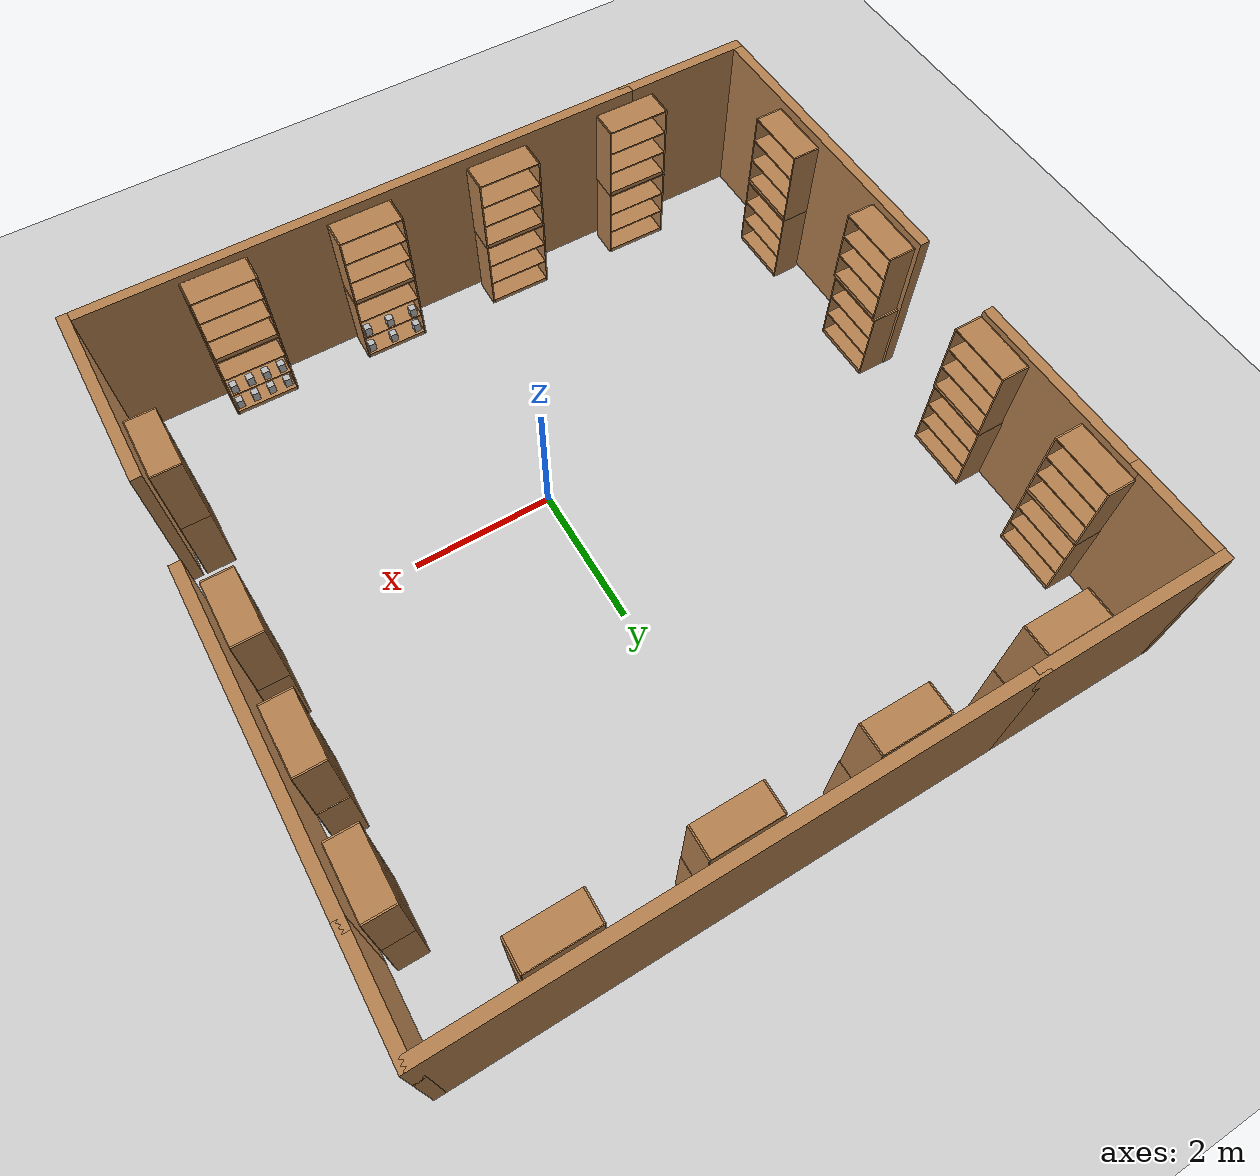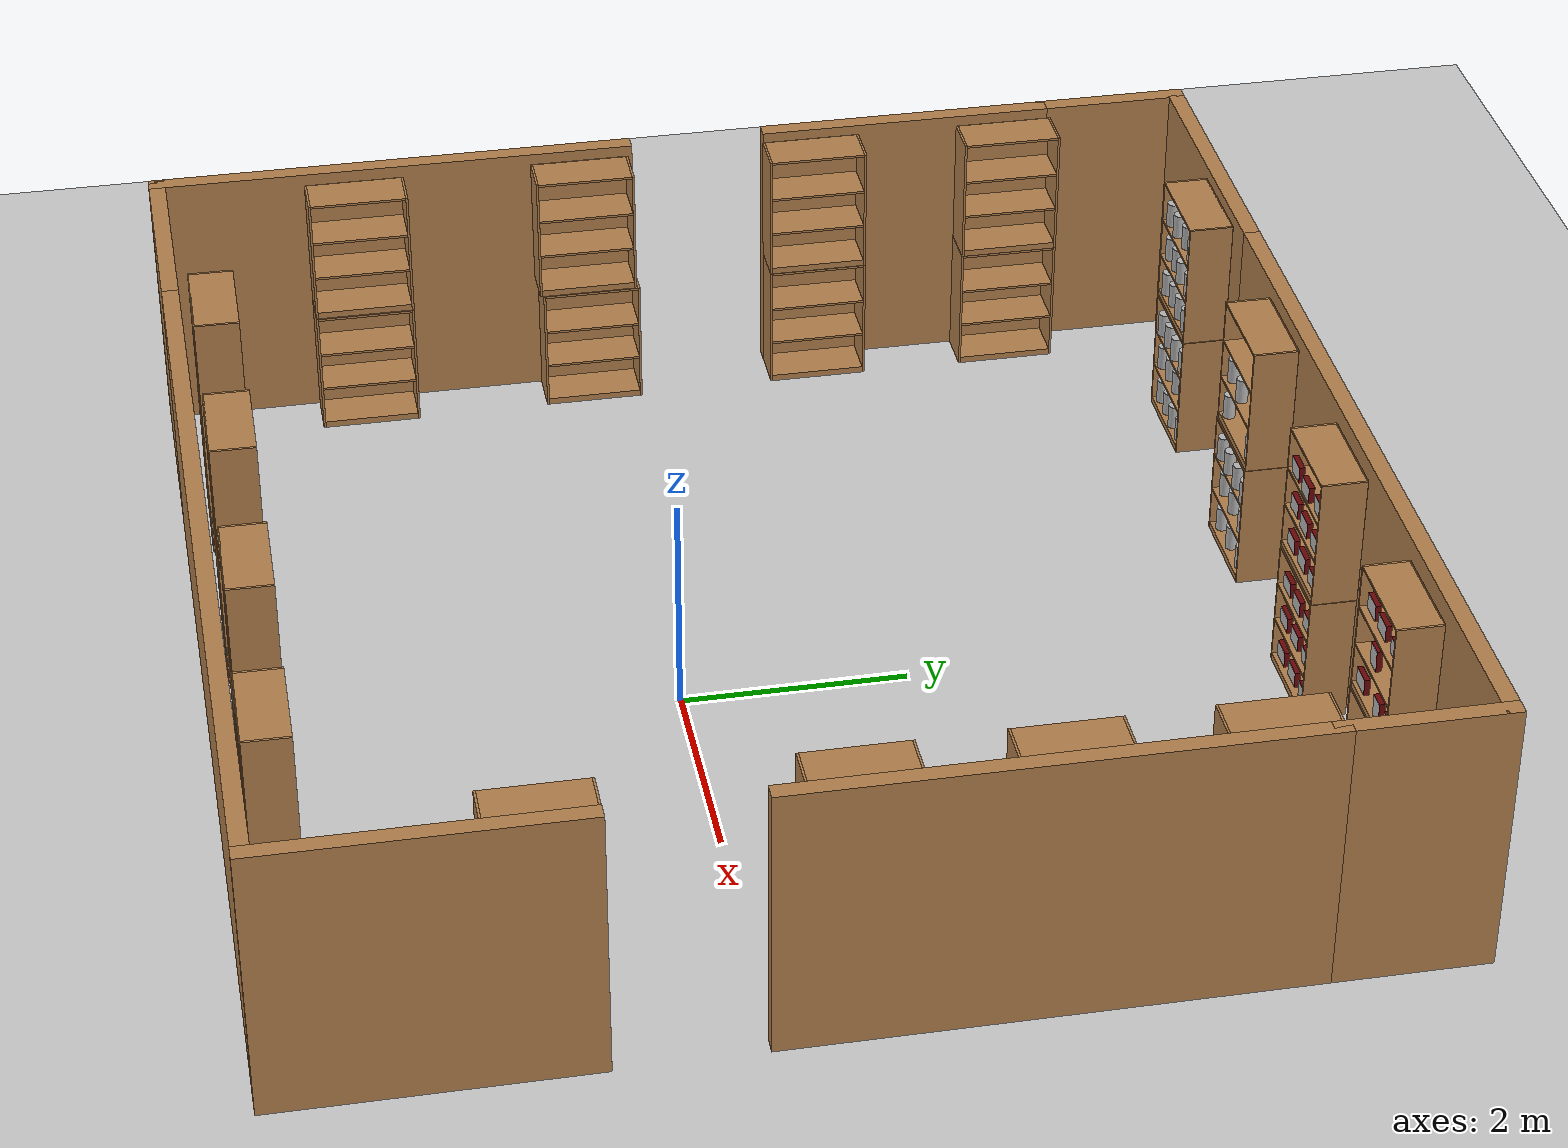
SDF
<sdf version="1.7">
 <world name="default">
  <light name="sun" type="directional">
   <pose>0 0 10 0 -0 0</pose>
   <diffuse>0.8 0.8 0.8 1</diffuse>
   <specular>0.1 0.1 0.1 1</specular>
   <attenuation>
    <range>1000</range>
    <constant>0.9</constant>
    <linear>0.01</linear>
    <quadratic>0.001</quadratic>
   </attenuation>
   <direction>-0.5 0.5 -1</direction>
   <spot><inner_angle>0</inner_angle><outer_angle>0</outer_angle><falloff>0</falloff></spot>
  </light>
  <model name="ground_plane">
   <static>1</static>
   <link name="link">
    <collision name="collision">
     <geometry><plane><normal>0 0 1</normal><size>100 100</size></plane></geometry>
     <surface><friction><ode><mu>100</mu><mu2>50</mu2></ode></friction></surface>
    </collision>
    <visual name="visual">
     <cast_shadows>0</cast_shadows>
     <geometry><plane><normal>0 0 1</normal><size>100 100</size></plane></geometry>
     <material>
      <script><uri>file://media/materials/scripts/gazebo.material</uri><name>Gazebo/Grey</name></script>
     </material>
    </visual>
   </link>
  </model>
  <gravity>0 0 -9.8</gravity>
  <magnetic_field>6e-06 2.3e-05 -4.2e-05</magnetic_field>
  <atmosphere type="adiabatic"/>
  <physics name="default_physics" default="0" type="ode">
   <max_step_size>0.001</max_step_size>
   <real_time_factor>1</real_time_factor>
   <real_time_update_rate>1000</real_time_update_rate>
  </physics>
  <scene><ambient>0.4 0.4 0.4 1</ambient><background>0.7 0.7 0.7 1</background><shadows>1</shadows></scene>
  <spherical_coordinates>
   <surface_model>EARTH_WGS84</surface_model>
   <latitude_deg>0</latitude_deg>
   <longitude_deg>0</longitude_deg>
   <elevation>0</elevation>
   <heading_deg>0</heading_deg>
  </spherical_coordinates>
  <model name="shopping_mart_box">
   <pose>-0.44063 0.87202 0 0 -0 0</pose>
   <link name="Wall_11">
    <collision name="Wall_11_Collision">
     <geometry><box><size>2 0.15 2.5</size></box></geometry>
     <pose>0 0 1.25 0 -0 0</pose>
    </collision>
    <visual name="Wall_11_Visual">
     <pose>0 0 1.25 0 -0 0</pose>
     <geometry><box><size>2 0.15 2.5</size></box></geometry>
     <material>
      <script><uri>file://media/materials/scripts/gazebo.material</uri><name>Gazebo/Wood</name></script>
      <ambient>1 1 1 1</ambient>
     </material>
    </visual>
    <pose>-4.05 -4.85 0 0 -0 3.14159</pose>
   </link>
   <link name="Wall_12">
    <collision name="Wall_12_Collision">
     <geometry><box><size>4.5 0.15 2.5</size></box></geometry>
     <pose>0 0 1.25 0 -0 0</pose>
    </collision>
    <visual name="Wall_12_Visual">
     <pose>0 0 1.25 0 -0 0</pose>
     <geometry><box><size>4.5 0.15 2.5</size></box></geometry>
     <material>
      <script><uri>file://media/materials/scripts/gazebo.material</uri><name>Gazebo/Wood</name></script>
      <ambient>1 1 1 1</ambient>
     </material>
    </visual>
    <pose>-4.975 -2.675 0 0 -0 1.5708</pose>
   </link>
   <link name="Wall_15">
    <collision name="Wall_15_Collision">
     <geometry><box><size>2.75 0.15 2.5</size></box></geometry>
     <pose>0 0 1.25 0 -0 0</pose>
    </collision>
    <visual name="Wall_15_Visual">
     <pose>0 0 1.25 0 -0 0</pose>
     <geometry><box><size>2.75 0.15 2.5</size></box></geometry>
     <material>
      <script><uri>file://media/materials/scripts/gazebo.material</uri><name>Gazebo/Wood</name></script>
      <ambient>1 1 1 1</ambient>
     </material>
    </visual>
    <pose>-4.975 2.2 0 0 0 -1.5708</pose>
   </link>
   <link name="Wall_17">
    <collision name="Wall_17_Collision">
     <geometry><box><size>1.5 0.15 2.5</size></box></geometry>
     <pose>0 0 1.25 0 -0 0</pose>
    </collision>
    <visual name="Wall_17_Visual">
     <pose>0 0 1.25 0 -0 0</pose>
     <geometry><box><size>1.5 0.15 2.5</size></box></geometry>
     <material>
      <script><uri>file://media/materials/scripts/gazebo.material</uri><name>Gazebo/Wood</name></script>
      <ambient>1 1 1 1</ambient>
     </material>
    </visual>
    <pose>-4.975 4.175 0 0 -0 1.5708</pose>
   </link>
   <link name="Wall_21">
    <collision name="Wall_21_Collision">
     <geometry><box><size>2.75 0.15 2.5</size></box></geometry>
     <pose>0 0 1.25 0 -0 0</pose>
    </collision>
    <visual name="Wall_21_Visual">
     <pose>0 0 1.25 0 -0 0</pose>
     <geometry><box><size>2.75 0.15 2.5</size></box></geometry>
     <material>
      <script><uri>file://media/materials/scripts/gazebo.material</uri><name>Gazebo/Wood</name></script>
      <ambient>1 1 1 1</ambient>
     </material>
    </visual>
    <pose>-3.675 4.85 0 0 -0 0</pose>
   </link>
   <link name="Wall_22">
    <collision name="Wall_22_Collision">
     <geometry><box><size>7.5 0.15 2.5</size></box></geometry>
     <pose>0 0 1.25 0 -0 0</pose>
    </collision>
    <visual name="Wall_22_Visual">
     <pose>0 0 1.25 0 -0 0</pose>
     <geometry><box><size>7.5 0.15 2.5</size></box></geometry>
     <material>
      <script><uri>file://media/materials/scripts/gazebo.material</uri><name>Gazebo/Wood</name></script>
      <ambient>1 1 1 1</ambient>
     </material>
    </visual>
    <pose>1.3 4.85 0 0 -0 0</pose>
   </link>
   <link name="Wall_23">
    <collision name="Wall_23_Collision">
     <geometry><box><size>1.5 0.15 2.5</size></box></geometry>
     <pose>0 0 1.25 0 -0 0</pose>
    </collision>
    <visual name="Wall_23_Visual">
     <pose>0 0 1.25 0 -0 0</pose>
     <geometry><box><size>1.5 0.15 2.5</size></box></geometry>
     <material>
      <script><uri>file://media/materials/scripts/gazebo.material</uri><name>Gazebo/Wood</name></script>
      <ambient>1 1 1 1</ambient>
     </material>
    </visual>
    <pose>4.975 4.175 0 0 0 -1.5708</pose>
   </link>
   <link name="Wall_29">
    <collision name="Wall_29_Collision">
     <geometry><box><size>4.5 0.15 2.5</size></box></geometry>
     <pose>0 0 1.25 0 -0 0</pose>
    </collision>
    <visual name="Wall_29_Visual">
     <pose>0 0 1.25 0 -0 0</pose>
     <geometry><box><size>4.5 0.15 2.5</size></box></geometry>
     <material>
      <script><uri>file://media/materials/scripts/gazebo.material</uri><name>Gazebo/Wood</name></script>
      <ambient>1 1 1 1</ambient>
     </material>
    </visual>
    <pose>4.975 1.325 0 0 0 -1.5708</pose>
   </link>
   <link name="Wall_31">
    <collision name="Wall_31_Collision">
     <geometry><box><size>2.75 0.15 2.5</size></box></geometry>
     <pose>0 0 1.25 0 -0 0</pose>
    </collision>
    <visual name="Wall_31_Visual">
     <pose>0 0 1.25 0 -0 0</pose>
     <geometry><box><size>2.75 0.15 2.5</size></box></geometry>
     <material>
      <script><uri>file://media/materials/scripts/gazebo.material</uri><name>Gazebo/Wood</name></script>
      <ambient>1 1 1 1</ambient>
     </material>
    </visual>
    <pose>4.975 -3.55 0 0 -0 1.5708</pose>
   </link>
   <link name="Wall_6">
    <collision name="Wall_6_Collision">
     <geometry><box><size>8.25 0.15 2.5</size></box></geometry>
     <pose>0 0 1.25 0 -0 0</pose>
    </collision>
    <visual name="Wall_6_Visual">
     <pose>0 0 1.25 0 -0 0</pose>
     <geometry><box><size>8.25 0.15 2.5</size></box></geometry>
     <material>
      <script><uri>file://media/materials/scripts/gazebo.material</uri><name>Gazebo/Wood</name></script>
      <ambient>1 1 1 1</ambient>
     </material>
    </visual>
    <pose>0.925 -4.85 0 0 -0 0</pose>
   </link>
   <static>1</static>
  </model>
  <model name="bookshelf">
   <static>1</static>
   <link name="link">
    <inertial><mass>1</mass></inertial>
    <collision name="back">
     <pose>0 0.005 0.6 0 -0 0</pose>
     <geometry><box><size>0.9 0.01 1.2</size></box></geometry>
    </collision>
    <visual name="visual1">
     <pose>0 0.005 0.6 0 -0 0</pose>
     <geometry><box><size>0.9 0.01 1.2</size></box></geometry>
     <material>
      <script><uri>file://media/materials/scripts/gazebo.material</uri><name>Gazebo/Wood</name></script>
     </material>
    </visual>
    <collision name="left_side">
     <pose>0.45 -0.195 0.6 0 -0 0</pose>
     <geometry><box><size>0.02 0.4 1.2</size></box></geometry>
    </collision>
    <visual name="visual2">
     <pose>0.45 -0.195 0.6 0 -0 0</pose>
     <geometry><box><size>0.02 0.4 1.2</size></box></geometry>
     <material>
      <script><uri>file://media/materials/scripts/gazebo.material</uri><name>Gazebo/Wood</name></script>
     </material>
    </visual>
    <collision name="right_side">
     <pose>-0.45 -0.195 0.6 0 -0 0</pose>
     <geometry><box><size>0.02 0.4 1.2</size></box></geometry>
    </collision>
    <visual name="visual3">
     <pose>-0.45 -0.195 0.6 0 -0 0</pose>
     <geometry><box><size>0.02 0.4 1.2</size></box></geometry>
     <material>
      <script><uri>file://media/materials/scripts/gazebo.material</uri><name>Gazebo/Wood</name></script>
     </material>
    </visual>
    <collision name="bottom">
     <pose>0 -0.195 0.03 0 -0 0</pose>
     <geometry><box><size>0.88 0.4 0.06</size></box></geometry>
    </collision>
    <visual name="visual4">
     <pose>0 -0.195 0.03 0 -0 0</pose>
     <geometry><box><size>0.88 0.4 0.06</size></box></geometry>
     <material>
      <script><uri>file://media/materials/scripts/gazebo.material</uri><name>Gazebo/Wood</name></script>
     </material>
    </visual>
    <collision name="top">
     <pose>0 -0.195 1.19 0 -0 0</pose>
     <geometry><box><size>0.88 0.4 0.02</size></box></geometry>
    </collision>
    <visual name="visual5">
     <pose>0 -0.195 1.19 0 -0 0</pose>
     <geometry><box><size>0.88 0.4 0.02</size></box></geometry>
     <material>
      <script><uri>file://media/materials/scripts/gazebo.material</uri><name>Gazebo/Wood</name></script>
     </material>
    </visual>
    <collision name="low_shelf">
     <pose>0 -0.195 0.43 0 -0 0</pose>
     <geometry><box><size>0.88 0.4 0.02</size></box></geometry>
    </collision>
    <visual name="visual6">
     <pose>0 -0.195 0.43 0 -0 0</pose>
     <geometry><box><size>0.88 0.4 0.02</size></box></geometry>
     <material>
      <script><uri>file://media/materials/scripts/gazebo.material</uri><name>Gazebo/Wood</name></script>
     </material>
    </visual>
    <collision name="high_shelf">
     <pose>0 -0.195 0.8 0 -0 0</pose>
     <geometry><box><size>0.88 0.4 0.02</size></box></geometry>
    </collision>
    <visual name="visual7">
     <pose>0 -0.195 0.8 0 -0 0</pose>
     <geometry><box><size>0.88 0.4 0.02</size></box></geometry>
     <material>
      <script><uri>file://media/materials/scripts/gazebo.material</uri><name>Gazebo/Wood</name></script>
     </material>
    </visual>
   </link>
   <pose>2.83268 5.58259 0 0 -0 0</pose>
  </model>
  <model name="bookshelf_1">
   <static>1</static>
   <link name="link">
    <inertial><mass>1</mass></inertial>
    <collision name="back">
     <pose>0 0.005 0.6 0 -0 0</pose>
     <geometry><box><size>0.9 0.01 1.2</size></box></geometry>
    </collision>
    <visual name="visual1">
     <pose>0 0.005 0.6 0 -0 0</pose>
     <geometry><box><size>0.9 0.01 1.2</size></box></geometry>
     <material>
      <script><uri>file://media/materials/scripts/gazebo.material</uri><name>Gazebo/Wood</name></script>
     </material>
    </visual>
    <collision name="left_side">
     <pose>0.45 -0.195 0.6 0 -0 0</pose>
     <geometry><box><size>0.02 0.4 1.2</size></box></geometry>
    </collision>
    <visual name="visual2">
     <pose>0.45 -0.195 0.6 0 -0 0</pose>
     <geometry><box><size>0.02 0.4 1.2</size></box></geometry>
     <material>
      <script><uri>file://media/materials/scripts/gazebo.material</uri><name>Gazebo/Wood</name></script>
     </material>
    </visual>
    <collision name="right_side">
     <pose>-0.45 -0.195 0.6 0 -0 0</pose>
     <geometry><box><size>0.02 0.4 1.2</size></box></geometry>
    </collision>
    <visual name="visual3">
     <pose>-0.45 -0.195 0.6 0 -0 0</pose>
     <geometry><box><size>0.02 0.4 1.2</size></box></geometry>
     <material>
      <script><uri>file://media/materials/scripts/gazebo.material</uri><name>Gazebo/Wood</name></script>
     </material>
    </visual>
    <collision name="bottom">
     <pose>0 -0.195 0.03 0 -0 0</pose>
     <geometry><box><size>0.88 0.4 0.06</size></box></geometry>
    </collision>
    <visual name="visual4">
     <pose>0 -0.195 0.03 0 -0 0</pose>
     <geometry><box><size>0.88 0.4 0.06</size></box></geometry>
     <material>
      <script><uri>file://media/materials/scripts/gazebo.material</uri><name>Gazebo/Wood</name></script>
     </material>
    </visual>
    <collision name="top">
     <pose>0 -0.195 1.19 0 -0 0</pose>
     <geometry><box><size>0.88 0.4 0.02</size></box></geometry>
    </collision>
    <visual name="visual5">
     <pose>0 -0.195 1.19 0 -0 0</pose>
     <geometry><box><size>0.88 0.4 0.02</size></box></geometry>
     <material>
      <script><uri>file://media/materials/scripts/gazebo.material</uri><name>Gazebo/Wood</name></script>
     </material>
    </visual>
    <collision name="low_shelf">
     <pose>0 -0.195 0.43 0 -0 0</pose>
     <geometry><box><size>0.88 0.4 0.02</size></box></geometry>
    </collision>
    <visual name="visual6">
     <pose>0 -0.195 0.43 0 -0 0</pose>
     <geometry><box><size>0.88 0.4 0.02</size></box></geometry>
     <material>
      <script><uri>file://media/materials/scripts/gazebo.material</uri><name>Gazebo/Wood</name></script>
     </material>
    </visual>
    <collision name="high_shelf">
     <pose>0 -0.195 0.8 0 -0 0</pose>
     <geometry><box><size>0.88 0.4 0.02</size></box></geometry>
    </collision>
    <visual name="visual7">
     <pose>0 -0.195 0.8 0 -0 0</pose>
     <geometry><box><size>0.88 0.4 0.02</size></box></geometry>
     <material>
      <script><uri>file://media/materials/scripts/gazebo.material</uri><name>Gazebo/Wood</name></script>
     </material>
    </visual>
   </link>
   <pose>0.770602 5.5901 0 0 -0 0</pose>
  </model>
  <model name="bookshelf_2_clone">
   <static>1</static>
   <link name="link">
    <inertial><mass>1</mass></inertial>
    <collision name="back">
     <pose>0 0.005 0.6 0 -0 0</pose>
     <geometry><box><size>0.9 0.01 1.2</size></box></geometry>
    </collision>
    <visual name="visual1">
     <pose>0 0.005 0.6 0 -0 0</pose>
     <geometry><box><size>0.9 0.01 1.2</size></box></geometry>
     <material>
      <script><uri>file://media/materials/scripts/gazebo.material</uri><name>Gazebo/Wood</name></script>
     </material>
    </visual>
    <collision name="left_side">
     <pose>0.45 -0.195 0.6 0 -0 0</pose>
     <geometry><box><size>0.02 0.4 1.2</size></box></geometry>
    </collision>
    <visual name="visual2">
     <pose>0.45 -0.195 0.6 0 -0 0</pose>
     <geometry><box><size>0.02 0.4 1.2</size></box></geometry>
     <material>
      <script><uri>file://media/materials/scripts/gazebo.material</uri><name>Gazebo/Wood</name></script>
     </material>
    </visual>
    <collision name="right_side">
     <pose>-0.45 -0.195 0.6 0 -0 0</pose>
     <geometry><box><size>0.02 0.4 1.2</size></box></geometry>
    </collision>
    <visual name="visual3">
     <pose>-0.45 -0.195 0.6 0 -0 0</pose>
     <geometry><box><size>0.02 0.4 1.2</size></box></geometry>
     <material>
      <script><uri>file://media/materials/scripts/gazebo.material</uri><name>Gazebo/Wood</name></script>
     </material>
    </visual>
    <collision name="bottom">
     <pose>0 -0.195 0.03 0 -0 0</pose>
     <geometry><box><size>0.88 0.4 0.06</size></box></geometry>
    </collision>
    <visual name="visual4">
     <pose>0 -0.195 0.03 0 -0 0</pose>
     <geometry><box><size>0.88 0.4 0.06</size></box></geometry>
     <material>
      <script><uri>file://media/materials/scripts/gazebo.material</uri><name>Gazebo/Wood</name></script>
     </material>
    </visual>
    <collision name="top">
     <pose>0 -0.195 1.19 0 -0 0</pose>
     <geometry><box><size>0.88 0.4 0.02</size></box></geometry>
    </collision>
    <visual name="visual5">
     <pose>0 -0.195 1.19 0 -0 0</pose>
     <geometry><box><size>0.88 0.4 0.02</size></box></geometry>
     <material>
      <script><uri>file://media/materials/scripts/gazebo.material</uri><name>Gazebo/Wood</name></script>
     </material>
    </visual>
    <collision name="low_shelf">
     <pose>0 -0.195 0.43 0 -0 0</pose>
     <geometry><box><size>0.88 0.4 0.02</size></box></geometry>
    </collision>
    <visual name="visual6">
     <pose>0 -0.195 0.43 0 -0 0</pose>
     <geometry><box><size>0.88 0.4 0.02</size></box></geometry>
     <material>
      <script><uri>file://media/materials/scripts/gazebo.material</uri><name>Gazebo/Wood</name></script>
     </material>
    </visual>
    <collision name="high_shelf">
     <pose>0 -0.195 0.8 0 -0 0</pose>
     <geometry><box><size>0.88 0.4 0.02</size></box></geometry>
    </collision>
    <visual name="visual7">
     <pose>0 -0.195 0.8 0 -0 0</pose>
     <geometry><box><size>0.88 0.4 0.02</size></box></geometry>
     <material>
      <script><uri>file://media/materials/scripts/gazebo.material</uri><name>Gazebo/Wood</name></script>
     </material>
    </visual>
   </link>
   <pose>-1.30264 5.59901 0 0 -0 0</pose>
  </model>
  <model name="bookshelf_2_clone_clone">
   <static>1</static>
   <link name="link">
    <inertial><mass>1</mass></inertial>
    <collision name="back">
     <pose>0 0.005 0.6 0 -0 0</pose>
     <geometry><box><size>0.9 0.01 1.2</size></box></geometry>
    </collision>
    <visual name="visual1">
     <pose>0 0.005 0.6 0 -0 0</pose>
     <geometry><box><size>0.9 0.01 1.2</size></box></geometry>
     <material>
      <script><uri>file://media/materials/scripts/gazebo.material</uri><name>Gazebo/Wood</name></script>
     </material>
    </visual>
    <collision name="left_side">
     <pose>0.45 -0.195 0.6 0 -0 0</pose>
     <geometry><box><size>0.02 0.4 1.2</size></box></geometry>
    </collision>
    <visual name="visual2">
     <pose>0.45 -0.195 0.6 0 -0 0</pose>
     <geometry><box><size>0.02 0.4 1.2</size></box></geometry>
     <material>
      <script><uri>file://media/materials/scripts/gazebo.material</uri><name>Gazebo/Wood</name></script>
     </material>
    </visual>
    <collision name="right_side">
     <pose>-0.45 -0.195 0.6 0 -0 0</pose>
     <geometry><box><size>0.02 0.4 1.2</size></box></geometry>
    </collision>
    <visual name="visual3">
     <pose>-0.45 -0.195 0.6 0 -0 0</pose>
     <geometry><box><size>0.02 0.4 1.2</size></box></geometry>
     <material>
      <script><uri>file://media/materials/scripts/gazebo.material</uri><name>Gazebo/Wood</name></script>
     </material>
    </visual>
    <collision name="bottom">
     <pose>0 -0.195 0.03 0 -0 0</pose>
     <geometry><box><size>0.88 0.4 0.06</size></box></geometry>
    </collision>
    <visual name="visual4">
     <pose>0 -0.195 0.03 0 -0 0</pose>
     <geometry><box><size>0.88 0.4 0.06</size></box></geometry>
     <material>
      <script><uri>file://media/materials/scripts/gazebo.material</uri><name>Gazebo/Wood</name></script>
     </material>
    </visual>
    <collision name="top">
     <pose>0 -0.195 1.19 0 -0 0</pose>
     <geometry><box><size>0.88 0.4 0.02</size></box></geometry>
    </collision>
    <visual name="visual5">
     <pose>0 -0.195 1.19 0 -0 0</pose>
     <geometry><box><size>0.88 0.4 0.02</size></box></geometry>
     <material>
      <script><uri>file://media/materials/scripts/gazebo.material</uri><name>Gazebo/Wood</name></script>
     </material>
    </visual>
    <collision name="low_shelf">
     <pose>0 -0.195 0.43 0 -0 0</pose>
     <geometry><box><size>0.88 0.4 0.02</size></box></geometry>
    </collision>
    <visual name="visual6">
     <pose>0 -0.195 0.43 0 -0 0</pose>
     <geometry><box><size>0.88 0.4 0.02</size></box></geometry>
     <material>
      <script><uri>file://media/materials/scripts/gazebo.material</uri><name>Gazebo/Wood</name></script>
     </material>
    </visual>
    <collision name="high_shelf">
     <pose>0 -0.195 0.8 0 -0 0</pose>
     <geometry><box><size>0.88 0.4 0.02</size></box></geometry>
    </collision>
    <visual name="visual7">
     <pose>0 -0.195 0.8 0 -0 0</pose>
     <geometry><box><size>0.88 0.4 0.02</size></box></geometry>
     <material>
      <script><uri>file://media/materials/scripts/gazebo.material</uri><name>Gazebo/Wood</name></script>
     </material>
    </visual>
   </link>
   <pose>-3.46853 5.62428 0 0 -0 0</pose>
  </model>
  <model name="bookshelf_3_clone">
   <static>1</static>
   <link name="link">
    <inertial><mass>1</mass></inertial>
    <collision name="back">
     <pose>0 0.005 0.6 0 -0 0</pose>
     <geometry><box><size>0.9 0.01 1.2</size></box></geometry>
    </collision>
    <visual name="visual1">
     <pose>0 0.005 0.6 0 -0 0</pose>
     <geometry><box><size>0.9 0.01 1.2</size></box></geometry>
     <material>
      <script><uri>file://media/materials/scripts/gazebo.material</uri><name>Gazebo/Wood</name></script>
     </material>
    </visual>
    <collision name="left_side">
     <pose>0.45 -0.195 0.6 0 -0 0</pose>
     <geometry><box><size>0.02 0.4 1.2</size></box></geometry>
    </collision>
    <visual name="visual2">
     <pose>0.45 -0.195 0.6 0 -0 0</pose>
     <geometry><box><size>0.02 0.4 1.2</size></box></geometry>
     <material>
      <script><uri>file://media/materials/scripts/gazebo.material</uri><name>Gazebo/Wood</name></script>
     </material>
    </visual>
    <collision name="right_side">
     <pose>-0.45 -0.195 0.6 0 -0 0</pose>
     <geometry><box><size>0.02 0.4 1.2</size></box></geometry>
    </collision>
    <visual name="visual3">
     <pose>-0.45 -0.195 0.6 0 -0 0</pose>
     <geometry><box><size>0.02 0.4 1.2</size></box></geometry>
     <material>
      <script><uri>file://media/materials/scripts/gazebo.material</uri><name>Gazebo/Wood</name></script>
     </material>
    </visual>
    <collision name="bottom">
     <pose>0 -0.195 0.03 0 -0 0</pose>
     <geometry><box><size>0.88 0.4 0.06</size></box></geometry>
    </collision>
    <visual name="visual4">
     <pose>0 -0.195 0.03 0 -0 0</pose>
     <geometry><box><size>0.88 0.4 0.06</size></box></geometry>
     <material>
      <script><uri>file://media/materials/scripts/gazebo.material</uri><name>Gazebo/Wood</name></script>
     </material>
    </visual>
    <collision name="top">
     <pose>0 -0.195 1.19 0 -0 0</pose>
     <geometry><box><size>0.88 0.4 0.02</size></box></geometry>
    </collision>
    <visual name="visual5">
     <pose>0 -0.195 1.19 0 -0 0</pose>
     <geometry><box><size>0.88 0.4 0.02</size></box></geometry>
     <material>
      <script><uri>file://media/materials/scripts/gazebo.material</uri><name>Gazebo/Wood</name></script>
     </material>
    </visual>
    <collision name="low_shelf">
     <pose>0 -0.195 0.43 0 -0 0</pose>
     <geometry><box><size>0.88 0.4 0.02</size></box></geometry>
    </collision>
    <visual name="visual6">
     <pose>0 -0.195 0.43 0 -0 0</pose>
     <geometry><box><size>0.88 0.4 0.02</size></box></geometry>
     <material>
      <script><uri>file://media/materials/scripts/gazebo.material</uri><name>Gazebo/Wood</name></script>
     </material>
    </visual>
    <collision name="high_shelf">
     <pose>0 -0.195 0.8 0 -0 0</pose>
     <geometry><box><size>0.88 0.4 0.02</size></box></geometry>
    </collision>
    <visual name="visual7">
     <pose>0 -0.195 0.8 0 -0 0</pose>
     <geometry><box><size>0.88 0.4 0.02</size></box></geometry>
     <material>
      <script><uri>file://media/materials/scripts/gazebo.material</uri><name>Gazebo/Wood</name></script>
     </material>
    </visual>
   </link>
   <pose>-1.30336 5.6079 1.20481 0 -0 0</pose>
  </model>
  <model name="bookshelf_3_clone_clone">
   <static>1</static>
   <link name="link">
    <inertial><mass>1</mass></inertial>
    <collision name="back">
     <pose>0 0.005 0.6 0 -0 0</pose>
     <geometry><box><size>0.9 0.01 1.2</size></box></geometry>
    </collision>
    <visual name="visual1">
     <pose>0 0.005 0.6 0 -0 0</pose>
     <geometry><box><size>0.9 0.01 1.2</size></box></geometry>
     <material>
      <script><uri>file://media/materials/scripts/gazebo.material</uri><name>Gazebo/Wood</name></script>
     </material>
    </visual>
    <collision name="left_side">
     <pose>0.45 -0.195 0.6 0 -0 0</pose>
     <geometry><box><size>0.02 0.4 1.2</size></box></geometry>
    </collision>
    <visual name="visual2">
     <pose>0.45 -0.195 0.6 0 -0 0</pose>
     <geometry><box><size>0.02 0.4 1.2</size></box></geometry>
     <material>
      <script><uri>file://media/materials/scripts/gazebo.material</uri><name>Gazebo/Wood</name></script>
     </material>
    </visual>
    <collision name="right_side">
     <pose>-0.45 -0.195 0.6 0 -0 0</pose>
     <geometry><box><size>0.02 0.4 1.2</size></box></geometry>
    </collision>
    <visual name="visual3">
     <pose>-0.45 -0.195 0.6 0 -0 0</pose>
     <geometry><box><size>0.02 0.4 1.2</size></box></geometry>
     <material>
      <script><uri>file://media/materials/scripts/gazebo.material</uri><name>Gazebo/Wood</name></script>
     </material>
    </visual>
    <collision name="bottom">
     <pose>0 -0.195 0.03 0 -0 0</pose>
     <geometry><box><size>0.88 0.4 0.06</size></box></geometry>
    </collision>
    <visual name="visual4">
     <pose>0 -0.195 0.03 0 -0 0</pose>
     <geometry><box><size>0.88 0.4 0.06</size></box></geometry>
     <material>
      <script><uri>file://media/materials/scripts/gazebo.material</uri><name>Gazebo/Wood</name></script>
     </material>
    </visual>
    <collision name="top">
     <pose>0 -0.195 1.19 0 -0 0</pose>
     <geometry><box><size>0.88 0.4 0.02</size></box></geometry>
    </collision>
    <visual name="visual5">
     <pose>0 -0.195 1.19 0 -0 0</pose>
     <geometry><box><size>0.88 0.4 0.02</size></box></geometry>
     <material>
      <script><uri>file://media/materials/scripts/gazebo.material</uri><name>Gazebo/Wood</name></script>
     </material>
    </visual>
    <collision name="low_shelf">
     <pose>0 -0.195 0.43 0 -0 0</pose>
     <geometry><box><size>0.88 0.4 0.02</size></box></geometry>
    </collision>
    <visual name="visual6">
     <pose>0 -0.195 0.43 0 -0 0</pose>
     <geometry><box><size>0.88 0.4 0.02</size></box></geometry>
     <material>
      <script><uri>file://media/materials/scripts/gazebo.material</uri><name>Gazebo/Wood</name></script>
     </material>
    </visual>
    <collision name="high_shelf">
     <pose>0 -0.195 0.8 0 -0 0</pose>
     <geometry><box><size>0.88 0.4 0.02</size></box></geometry>
    </collision>
    <visual name="visual7">
     <pose>0 -0.195 0.8 0 -0 0</pose>
     <geometry><box><size>0.88 0.4 0.02</size></box></geometry>
     <material>
      <script><uri>file://media/materials/scripts/gazebo.material</uri><name>Gazebo/Wood</name></script>
     </material>
    </visual>
   </link>
   <pose>-3.47373 5.62521 1.20481 0 -0 0</pose>
  </model>
  <model name="bookshelf_3_clone_clone_0">
   <static>1</static>
   <link name="link">
    <inertial><mass>1</mass></inertial>
    <collision name="back">
     <pose>0 0.005 0.6 0 -0 0</pose>
     <geometry><box><size>0.9 0.01 1.2</size></box></geometry>
    </collision>
    <visual name="visual1">
     <pose>0 0.005 0.6 0 -0 0</pose>
     <geometry><box><size>0.9 0.01 1.2</size></box></geometry>
     <material>
      <script><uri>file://media/materials/scripts/gazebo.material</uri><name>Gazebo/Wood</name></script>
     </material>
    </visual>
    <collision name="left_side">
     <pose>0.45 -0.195 0.6 0 -0 0</pose>
     <geometry><box><size>0.02 0.4 1.2</size></box></geometry>
    </collision>
    <visual name="visual2">
     <pose>0.45 -0.195 0.6 0 -0 0</pose>
     <geometry><box><size>0.02 0.4 1.2</size></box></geometry>
     <material>
      <script><uri>file://media/materials/scripts/gazebo.material</uri><name>Gazebo/Wood</name></script>
     </material>
    </visual>
    <collision name="right_side">
     <pose>-0.45 -0.195 0.6 0 -0 0</pose>
     <geometry><box><size>0.02 0.4 1.2</size></box></geometry>
    </collision>
    <visual name="visual3">
     <pose>-0.45 -0.195 0.6 0 -0 0</pose>
     <geometry><box><size>0.02 0.4 1.2</size></box></geometry>
     <material>
      <script><uri>file://media/materials/scripts/gazebo.material</uri><name>Gazebo/Wood</name></script>
     </material>
    </visual>
    <collision name="bottom">
     <pose>0 -0.195 0.03 0 -0 0</pose>
     <geometry><box><size>0.88 0.4 0.06</size></box></geometry>
    </collision>
    <visual name="visual4">
     <pose>0 -0.195 0.03 0 -0 0</pose>
     <geometry><box><size>0.88 0.4 0.06</size></box></geometry>
     <material>
      <script><uri>file://media/materials/scripts/gazebo.material</uri><name>Gazebo/Wood</name></script>
     </material>
    </visual>
    <collision name="top">
     <pose>0 -0.195 1.19 0 -0 0</pose>
     <geometry><box><size>0.88 0.4 0.02</size></box></geometry>
    </collision>
    <visual name="visual5">
     <pose>0 -0.195 1.19 0 -0 0</pose>
     <geometry><box><size>0.88 0.4 0.02</size></box></geometry>
     <material>
      <script><uri>file://media/materials/scripts/gazebo.material</uri><name>Gazebo/Wood</name></script>
     </material>
    </visual>
    <collision name="low_shelf">
     <pose>0 -0.195 0.43 0 -0 0</pose>
     <geometry><box><size>0.88 0.4 0.02</size></box></geometry>
    </collision>
    <visual name="visual6">
     <pose>0 -0.195 0.43 0 -0 0</pose>
     <geometry><box><size>0.88 0.4 0.02</size></box></geometry>
     <material>
      <script><uri>file://media/materials/scripts/gazebo.material</uri><name>Gazebo/Wood</name></script>
     </material>
    </visual>
    <collision name="high_shelf">
     <pose>0 -0.195 0.8 0 -0 0</pose>
     <geometry><box><size>0.88 0.4 0.02</size></box></geometry>
    </collision>
    <visual name="visual7">
     <pose>0 -0.195 0.8 0 -0 0</pose>
     <geometry><box><size>0.88 0.4 0.02</size></box></geometry>
     <material>
      <script><uri>file://media/materials/scripts/gazebo.material</uri><name>Gazebo/Wood</name></script>
     </material>
    </visual>
   </link>
   <pose>0.76852 5.59426 1.20481 0 -0 0</pose>
  </model>
  <model name="bookshelf_3_clone_clone_1">
   <static>1</static>
   <link name="link">
    <inertial><mass>1</mass></inertial>
    <collision name="back">
     <pose>0 0.005 0.6 0 -0 0</pose>
     <geometry><box><size>0.9 0.01 1.2</size></box></geometry>
    </collision>
    <visual name="visual1">
     <pose>0 0.005 0.6 0 -0 0</pose>
     <geometry><box><size>0.9 0.01 1.2</size></box></geometry>
     <material>
      <script><uri>file://media/materials/scripts/gazebo.material</uri><name>Gazebo/Wood</name></script>
     </material>
    </visual>
    <collision name="left_side">
     <pose>0.45 -0.195 0.6 0 -0 0</pose>
     <geometry><box><size>0.02 0.4 1.2</size></box></geometry>
    </collision>
    <visual name="visual2">
     <pose>0.45 -0.195 0.6 0 -0 0</pose>
     <geometry><box><size>0.02 0.4 1.2</size></box></geometry>
     <material>
      <script><uri>file://media/materials/scripts/gazebo.material</uri><name>Gazebo/Wood</name></script>
     </material>
    </visual>
    <collision name="right_side">
     <pose>-0.45 -0.195 0.6 0 -0 0</pose>
     <geometry><box><size>0.02 0.4 1.2</size></box></geometry>
    </collision>
    <visual name="visual3">
     <pose>-0.45 -0.195 0.6 0 -0 0</pose>
     <geometry><box><size>0.02 0.4 1.2</size></box></geometry>
     <material>
      <script><uri>file://media/materials/scripts/gazebo.material</uri><name>Gazebo/Wood</name></script>
     </material>
    </visual>
    <collision name="bottom">
     <pose>0 -0.195 0.03 0 -0 0</pose>
     <geometry><box><size>0.88 0.4 0.06</size></box></geometry>
    </collision>
    <visual name="visual4">
     <pose>0 -0.195 0.03 0 -0 0</pose>
     <geometry><box><size>0.88 0.4 0.06</size></box></geometry>
     <material>
      <script><uri>file://media/materials/scripts/gazebo.material</uri><name>Gazebo/Wood</name></script>
     </material>
    </visual>
    <collision name="top">
     <pose>0 -0.195 1.19 0 -0 0</pose>
     <geometry><box><size>0.88 0.4 0.02</size></box></geometry>
    </collision>
    <visual name="visual5">
     <pose>0 -0.195 1.19 0 -0 0</pose>
     <geometry><box><size>0.88 0.4 0.02</size></box></geometry>
     <material>
      <script><uri>file://media/materials/scripts/gazebo.material</uri><name>Gazebo/Wood</name></script>
     </material>
    </visual>
    <collision name="low_shelf">
     <pose>0 -0.195 0.43 0 -0 0</pose>
     <geometry><box><size>0.88 0.4 0.02</size></box></geometry>
    </collision>
    <visual name="visual6">
     <pose>0 -0.195 0.43 0 -0 0</pose>
     <geometry><box><size>0.88 0.4 0.02</size></box></geometry>
     <material>
      <script><uri>file://media/materials/scripts/gazebo.material</uri><name>Gazebo/Wood</name></script>
     </material>
    </visual>
    <collision name="high_shelf">
     <pose>0 -0.195 0.8 0 -0 0</pose>
     <geometry><box><size>0.88 0.4 0.02</size></box></geometry>
    </collision>
    <visual name="visual7">
     <pose>0 -0.195 0.8 0 -0 0</pose>
     <geometry><box><size>0.88 0.4 0.02</size></box></geometry>
     <material>
      <script><uri>file://media/materials/scripts/gazebo.material</uri><name>Gazebo/Wood</name></script>
     </material>
    </visual>
   </link>
   <pose>2.83627 5.58516 1.20481 0 -0 0</pose>
  </model>
  <model name="bookshelf_4_clone">
   <static>1</static>
   <link name="link">
    <inertial><mass>1</mass></inertial>
    <collision name="back">
     <pose>0 0.005 0.6 0 -0 0</pose>
     <geometry><box><size>0.9 0.01 1.2</size></box></geometry>
    </collision>
    <visual name="visual1">
     <pose>0 0.005 0.6 0 -0 0</pose>
     <geometry><box><size>0.9 0.01 1.2</size></box></geometry>
     <material>
      <script><uri>file://media/materials/scripts/gazebo.material</uri><name>Gazebo/Wood</name></script>
     </material>
    </visual>
    <collision name="left_side">
     <pose>0.45 -0.195 0.6 0 -0 0</pose>
     <geometry><box><size>0.02 0.4 1.2</size></box></geometry>
    </collision>
    <visual name="visual2">
     <pose>0.45 -0.195 0.6 0 -0 0</pose>
     <geometry><box><size>0.02 0.4 1.2</size></box></geometry>
     <material>
      <script><uri>file://media/materials/scripts/gazebo.material</uri><name>Gazebo/Wood</name></script>
     </material>
    </visual>
    <collision name="right_side">
     <pose>-0.45 -0.195 0.6 0 -0 0</pose>
     <geometry><box><size>0.02 0.4 1.2</size></box></geometry>
    </collision>
    <visual name="visual3">
     <pose>-0.45 -0.195 0.6 0 -0 0</pose>
     <geometry><box><size>0.02 0.4 1.2</size></box></geometry>
     <material>
      <script><uri>file://media/materials/scripts/gazebo.material</uri><name>Gazebo/Wood</name></script>
     </material>
    </visual>
    <collision name="bottom">
     <pose>0 -0.195 0.03 0 -0 0</pose>
     <geometry><box><size>0.88 0.4 0.06</size></box></geometry>
    </collision>
    <visual name="visual4">
     <pose>0 -0.195 0.03 0 -0 0</pose>
     <geometry><box><size>0.88 0.4 0.06</size></box></geometry>
     <material>
      <script><uri>file://media/materials/scripts/gazebo.material</uri><name>Gazebo/Wood</name></script>
     </material>
    </visual>
    <collision name="top">
     <pose>0 -0.195 1.19 0 -0 0</pose>
     <geometry><box><size>0.88 0.4 0.02</size></box></geometry>
    </collision>
    <visual name="visual5">
     <pose>0 -0.195 1.19 0 -0 0</pose>
     <geometry><box><size>0.88 0.4 0.02</size></box></geometry>
     <material>
      <script><uri>file://media/materials/scripts/gazebo.material</uri><name>Gazebo/Wood</name></script>
     </material>
    </visual>
    <collision name="low_shelf">
     <pose>0 -0.195 0.43 0 -0 0</pose>
     <geometry><box><size>0.88 0.4 0.02</size></box></geometry>
    </collision>
    <visual name="visual6">
     <pose>0 -0.195 0.43 0 -0 0</pose>
     <geometry><box><size>0.88 0.4 0.02</size></box></geometry>
     <material>
      <script><uri>file://media/materials/scripts/gazebo.material</uri><name>Gazebo/Wood</name></script>
     </material>
    </visual>
    <collision name="high_shelf">
     <pose>0 -0.195 0.8 0 -0 0</pose>
     <geometry><box><size>0.88 0.4 0.02</size></box></geometry>
    </collision>
    <visual name="visual7">
     <pose>0 -0.195 0.8 0 -0 0</pose>
     <geometry><box><size>0.88 0.4 0.02</size></box></geometry>
     <material>
      <script><uri>file://media/materials/scripts/gazebo.material</uri><name>Gazebo/Wood</name></script>
     </material>
    </visual>
   </link>
   <pose>4.37345 3.97883 0 0 0 -1.5727</pose>
  </model>
  <model name="bookshelf_4_clone_0">
   <static>1</static>
   <link name="link">
    <inertial><mass>1</mass></inertial>
    <collision name="back">
     <pose>0 0.005 0.6 0 -0 0</pose>
     <geometry><box><size>0.9 0.01 1.2</size></box></geometry>
    </collision>
    <visual name="visual1">
     <pose>0 0.005 0.6 0 -0 0</pose>
     <geometry><box><size>0.9 0.01 1.2</size></box></geometry>
     <material>
      <script><uri>file://media/materials/scripts/gazebo.material</uri><name>Gazebo/Wood</name></script>
     </material>
    </visual>
    <collision name="left_side">
     <pose>0.45 -0.195 0.6 0 -0 0</pose>
     <geometry><box><size>0.02 0.4 1.2</size></box></geometry>
    </collision>
    <visual name="visual2">
     <pose>0.45 -0.195 0.6 0 -0 0</pose>
     <geometry><box><size>0.02 0.4 1.2</size></box></geometry>
     <material>
      <script><uri>file://media/materials/scripts/gazebo.material</uri><name>Gazebo/Wood</name></script>
     </material>
    </visual>
    <collision name="right_side">
     <pose>-0.45 -0.195 0.6 0 -0 0</pose>
     <geometry><box><size>0.02 0.4 1.2</size></box></geometry>
    </collision>
    <visual name="visual3">
     <pose>-0.45 -0.195 0.6 0 -0 0</pose>
     <geometry><box><size>0.02 0.4 1.2</size></box></geometry>
     <material>
      <script><uri>file://media/materials/scripts/gazebo.material</uri><name>Gazebo/Wood</name></script>
     </material>
    </visual>
    <collision name="bottom">
     <pose>0 -0.195 0.03 0 -0 0</pose>
     <geometry><box><size>0.88 0.4 0.06</size></box></geometry>
    </collision>
    <visual name="visual4">
     <pose>0 -0.195 0.03 0 -0 0</pose>
     <geometry><box><size>0.88 0.4 0.06</size></box></geometry>
     <material>
      <script><uri>file://media/materials/scripts/gazebo.material</uri><name>Gazebo/Wood</name></script>
     </material>
    </visual>
    <collision name="top">
     <pose>0 -0.195 1.19 0 -0 0</pose>
     <geometry><box><size>0.88 0.4 0.02</size></box></geometry>
    </collision>
    <visual name="visual5">
     <pose>0 -0.195 1.19 0 -0 0</pose>
     <geometry><box><size>0.88 0.4 0.02</size></box></geometry>
     <material>
      <script><uri>file://media/materials/scripts/gazebo.material</uri><name>Gazebo/Wood</name></script>
     </material>
    </visual>
    <collision name="low_shelf">
     <pose>0 -0.195 0.43 0 -0 0</pose>
     <geometry><box><size>0.88 0.4 0.02</size></box></geometry>
    </collision>
    <visual name="visual6">
     <pose>0 -0.195 0.43 0 -0 0</pose>
     <geometry><box><size>0.88 0.4 0.02</size></box></geometry>
     <material>
      <script><uri>file://media/materials/scripts/gazebo.material</uri><name>Gazebo/Wood</name></script>
     </material>
    </visual>
    <collision name="high_shelf">
     <pose>0 -0.195 0.8 0 -0 0</pose>
     <geometry><box><size>0.88 0.4 0.02</size></box></geometry>
    </collision>
    <visual name="visual7">
     <pose>0 -0.195 0.8 0 -0 0</pose>
     <geometry><box><size>0.88 0.4 0.02</size></box></geometry>
     <material>
      <script><uri>file://media/materials/scripts/gazebo.material</uri><name>Gazebo/Wood</name></script>
     </material>
    </visual>
   </link>
   <pose>4.37565 2.36025 0 0 0 -1.5727</pose>
  </model>
  <model name="bookshelf_4_clone_1">
   <static>1</static>
   <link name="link">
    <inertial><mass>1</mass></inertial>
    <collision name="back">
     <pose>0 0.005 0.6 0 -0 0</pose>
     <geometry><box><size>0.9 0.01 1.2</size></box></geometry>
    </collision>
    <visual name="visual1">
     <pose>0 0.005 0.6 0 -0 0</pose>
     <geometry><box><size>0.9 0.01 1.2</size></box></geometry>
     <material>
      <script><uri>file://media/materials/scripts/gazebo.material</uri><name>Gazebo/Wood</name></script>
     </material>
    </visual>
    <collision name="left_side">
     <pose>0.45 -0.195 0.6 0 -0 0</pose>
     <geometry><box><size>0.02 0.4 1.2</size></box></geometry>
    </collision>
    <visual name="visual2">
     <pose>0.45 -0.195 0.6 0 -0 0</pose>
     <geometry><box><size>0.02 0.4 1.2</size></box></geometry>
     <material>
      <script><uri>file://media/materials/scripts/gazebo.material</uri><name>Gazebo/Wood</name></script>
     </material>
    </visual>
    <collision name="right_side">
     <pose>-0.45 -0.195 0.6 0 -0 0</pose>
     <geometry><box><size>0.02 0.4 1.2</size></box></geometry>
    </collision>
    <visual name="visual3">
     <pose>-0.45 -0.195 0.6 0 -0 0</pose>
     <geometry><box><size>0.02 0.4 1.2</size></box></geometry>
     <material>
      <script><uri>file://media/materials/scripts/gazebo.material</uri><name>Gazebo/Wood</name></script>
     </material>
    </visual>
    <collision name="bottom">
     <pose>0 -0.195 0.03 0 -0 0</pose>
     <geometry><box><size>0.88 0.4 0.06</size></box></geometry>
    </collision>
    <visual name="visual4">
     <pose>0 -0.195 0.03 0 -0 0</pose>
     <geometry><box><size>0.88 0.4 0.06</size></box></geometry>
     <material>
      <script><uri>file://media/materials/scripts/gazebo.material</uri><name>Gazebo/Wood</name></script>
     </material>
    </visual>
    <collision name="top">
     <pose>0 -0.195 1.19 0 -0 0</pose>
     <geometry><box><size>0.88 0.4 0.02</size></box></geometry>
    </collision>
    <visual name="visual5">
     <pose>0 -0.195 1.19 0 -0 0</pose>
     <geometry><box><size>0.88 0.4 0.02</size></box></geometry>
     <material>
      <script><uri>file://media/materials/scripts/gazebo.material</uri><name>Gazebo/Wood</name></script>
     </material>
    </visual>
    <collision name="low_shelf">
     <pose>0 -0.195 0.43 0 -0 0</pose>
     <geometry><box><size>0.88 0.4 0.02</size></box></geometry>
    </collision>
    <visual name="visual6">
     <pose>0 -0.195 0.43 0 -0 0</pose>
     <geometry><box><size>0.88 0.4 0.02</size></box></geometry>
     <material>
      <script><uri>file://media/materials/scripts/gazebo.material</uri><name>Gazebo/Wood</name></script>
     </material>
    </visual>
    <collision name="high_shelf">
     <pose>0 -0.195 0.8 0 -0 0</pose>
     <geometry><box><size>0.88 0.4 0.02</size></box></geometry>
    </collision>
    <visual name="visual7">
     <pose>0 -0.195 0.8 0 -0 0</pose>
     <geometry><box><size>0.88 0.4 0.02</size></box></geometry>
     <material>
      <script><uri>file://media/materials/scripts/gazebo.material</uri><name>Gazebo/Wood</name></script>
     </material>
    </visual>
   </link>
   <pose>4.39312 0.69592 0 0 0 -1.5727</pose>
  </model>
  <model name="bookshelf_4_clone_1_clone">
   <static>1</static>
   <link name="link">
    <inertial><mass>1</mass></inertial>
    <collision name="back">
     <pose>0 0.005 0.6 0 -0 0</pose>
     <geometry><box><size>0.9 0.01 1.2</size></box></geometry>
    </collision>
    <visual name="visual1">
     <pose>0 0.005 0.6 0 -0 0</pose>
     <geometry><box><size>0.9 0.01 1.2</size></box></geometry>
     <material>
      <script><uri>file://media/materials/scripts/gazebo.material</uri><name>Gazebo/Wood</name></script>
     </material>
    </visual>
    <collision name="left_side">
     <pose>0.45 -0.195 0.6 0 -0 0</pose>
     <geometry><box><size>0.02 0.4 1.2</size></box></geometry>
    </collision>
    <visual name="visual2">
     <pose>0.45 -0.195 0.6 0 -0 0</pose>
     <geometry><box><size>0.02 0.4 1.2</size></box></geometry>
     <material>
      <script><uri>file://media/materials/scripts/gazebo.material</uri><name>Gazebo/Wood</name></script>
     </material>
    </visual>
    <collision name="right_side">
     <pose>-0.45 -0.195 0.6 0 -0 0</pose>
     <geometry><box><size>0.02 0.4 1.2</size></box></geometry>
    </collision>
    <visual name="visual3">
     <pose>-0.45 -0.195 0.6 0 -0 0</pose>
     <geometry><box><size>0.02 0.4 1.2</size></box></geometry>
     <material>
      <script><uri>file://media/materials/scripts/gazebo.material</uri><name>Gazebo/Wood</name></script>
     </material>
    </visual>
    <collision name="bottom">
     <pose>0 -0.195 0.03 0 -0 0</pose>
     <geometry><box><size>0.88 0.4 0.06</size></box></geometry>
    </collision>
    <visual name="visual4">
     <pose>0 -0.195 0.03 0 -0 0</pose>
     <geometry><box><size>0.88 0.4 0.06</size></box></geometry>
     <material>
      <script><uri>file://media/materials/scripts/gazebo.material</uri><name>Gazebo/Wood</name></script>
     </material>
    </visual>
    <collision name="top">
     <pose>0 -0.195 1.19 0 -0 0</pose>
     <geometry><box><size>0.88 0.4 0.02</size></box></geometry>
    </collision>
    <visual name="visual5">
     <pose>0 -0.195 1.19 0 -0 0</pose>
     <geometry><box><size>0.88 0.4 0.02</size></box></geometry>
     <material>
      <script><uri>file://media/materials/scripts/gazebo.material</uri><name>Gazebo/Wood</name></script>
     </material>
    </visual>
    <collision name="low_shelf">
     <pose>0 -0.195 0.43 0 -0 0</pose>
     <geometry><box><size>0.88 0.4 0.02</size></box></geometry>
    </collision>
    <visual name="visual6">
     <pose>0 -0.195 0.43 0 -0 0</pose>
     <geometry><box><size>0.88 0.4 0.02</size></box></geometry>
     <material>
      <script><uri>file://media/materials/scripts/gazebo.material</uri><name>Gazebo/Wood</name></script>
     </material>
    </visual>
    <collision name="high_shelf">
     <pose>0 -0.195 0.8 0 -0 0</pose>
     <geometry><box><size>0.88 0.4 0.02</size></box></geometry>
    </collision>
    <visual name="visual7">
     <pose>0 -0.195 0.8 0 -0 0</pose>
     <geometry><box><size>0.88 0.4 0.02</size></box></geometry>
     <material>
      <script><uri>file://media/materials/scripts/gazebo.material</uri><name>Gazebo/Wood</name></script>
     </material>
    </visual>
   </link>
   <pose>4.3806 2.34957 1.20741 0 0 -1.5727</pose>
  </model>
  <model name="bookshelf_4_clone_1_clone_clone">
   <static>1</static>
   <link name="link">
    <inertial><mass>1</mass></inertial>
    <collision name="back">
     <pose>0 0.005 0.6 0 -0 0</pose>
     <geometry><box><size>0.9 0.01 1.2</size></box></geometry>
    </collision>
    <visual name="visual1">
     <pose>0 0.005 0.6 0 -0 0</pose>
     <geometry><box><size>0.9 0.01 1.2</size></box></geometry>
     <material>
      <script><uri>file://media/materials/scripts/gazebo.material</uri><name>Gazebo/Wood</name></script>
     </material>
    </visual>
    <collision name="left_side">
     <pose>0.45 -0.195 0.6 0 -0 0</pose>
     <geometry><box><size>0.02 0.4 1.2</size></box></geometry>
    </collision>
    <visual name="visual2">
     <pose>0.45 -0.195 0.6 0 -0 0</pose>
     <geometry><box><size>0.02 0.4 1.2</size></box></geometry>
     <material>
      <script><uri>file://media/materials/scripts/gazebo.material</uri><name>Gazebo/Wood</name></script>
     </material>
    </visual>
    <collision name="right_side">
     <pose>-0.45 -0.195 0.6 0 -0 0</pose>
     <geometry><box><size>0.02 0.4 1.2</size></box></geometry>
    </collision>
    <visual name="visual3">
     <pose>-0.45 -0.195 0.6 0 -0 0</pose>
     <geometry><box><size>0.02 0.4 1.2</size></box></geometry>
     <material>
      <script><uri>file://media/materials/scripts/gazebo.material</uri><name>Gazebo/Wood</name></script>
     </material>
    </visual>
    <collision name="bottom">
     <pose>0 -0.195 0.03 0 -0 0</pose>
     <geometry><box><size>0.88 0.4 0.06</size></box></geometry>
    </collision>
    <visual name="visual4">
     <pose>0 -0.195 0.03 0 -0 0</pose>
     <geometry><box><size>0.88 0.4 0.06</size></box></geometry>
     <material>
      <script><uri>file://media/materials/scripts/gazebo.material</uri><name>Gazebo/Wood</name></script>
     </material>
    </visual>
    <collision name="top">
     <pose>0 -0.195 1.19 0 -0 0</pose>
     <geometry><box><size>0.88 0.4 0.02</size></box></geometry>
    </collision>
    <visual name="visual5">
     <pose>0 -0.195 1.19 0 -0 0</pose>
     <geometry><box><size>0.88 0.4 0.02</size></box></geometry>
     <material>
      <script><uri>file://media/materials/scripts/gazebo.material</uri><name>Gazebo/Wood</name></script>
     </material>
    </visual>
    <collision name="low_shelf">
     <pose>0 -0.195 0.43 0 -0 0</pose>
     <geometry><box><size>0.88 0.4 0.02</size></box></geometry>
    </collision>
    <visual name="visual6">
     <pose>0 -0.195 0.43 0 -0 0</pose>
     <geometry><box><size>0.88 0.4 0.02</size></box></geometry>
     <material>
      <script><uri>file://media/materials/scripts/gazebo.material</uri><name>Gazebo/Wood</name></script>
     </material>
    </visual>
    <collision name="high_shelf">
     <pose>0 -0.195 0.8 0 -0 0</pose>
     <geometry><box><size>0.88 0.4 0.02</size></box></geometry>
    </collision>
    <visual name="visual7">
     <pose>0 -0.195 0.8 0 -0 0</pose>
     <geometry><box><size>0.88 0.4 0.02</size></box></geometry>
     <material>
      <script><uri>file://media/materials/scripts/gazebo.material</uri><name>Gazebo/Wood</name></script>
     </material>
    </visual>
   </link>
   <pose>4.37481 3.98386 1.20741 0 0 -1.5727</pose>
  </model>
  <model name="bookshelf_4_clone_1_clone_clone_0">
   <static>1</static>
   <link name="link">
    <inertial><mass>1</mass></inertial>
    <collision name="back">
     <pose>0 0.005 0.6 0 -0 0</pose>
     <geometry><box><size>0.9 0.01 1.2</size></box></geometry>
    </collision>
    <visual name="visual1">
     <pose>0 0.005 0.6 0 -0 0</pose>
     <geometry><box><size>0.9 0.01 1.2</size></box></geometry>
     <material>
      <script><uri>file://media/materials/scripts/gazebo.material</uri><name>Gazebo/Wood</name></script>
     </material>
    </visual>
    <collision name="left_side">
     <pose>0.45 -0.195 0.6 0 -0 0</pose>
     <geometry><box><size>0.02 0.4 1.2</size></box></geometry>
    </collision>
    <visual name="visual2">
     <pose>0.45 -0.195 0.6 0 -0 0</pose>
     <geometry><box><size>0.02 0.4 1.2</size></box></geometry>
     <material>
      <script><uri>file://media/materials/scripts/gazebo.material</uri><name>Gazebo/Wood</name></script>
     </material>
    </visual>
    <collision name="right_side">
     <pose>-0.45 -0.195 0.6 0 -0 0</pose>
     <geometry><box><size>0.02 0.4 1.2</size></box></geometry>
    </collision>
    <visual name="visual3">
     <pose>-0.45 -0.195 0.6 0 -0 0</pose>
     <geometry><box><size>0.02 0.4 1.2</size></box></geometry>
     <material>
      <script><uri>file://media/materials/scripts/gazebo.material</uri><name>Gazebo/Wood</name></script>
     </material>
    </visual>
    <collision name="bottom">
     <pose>0 -0.195 0.03 0 -0 0</pose>
     <geometry><box><size>0.88 0.4 0.06</size></box></geometry>
    </collision>
    <visual name="visual4">
     <pose>0 -0.195 0.03 0 -0 0</pose>
     <geometry><box><size>0.88 0.4 0.06</size></box></geometry>
     <material>
      <script><uri>file://media/materials/scripts/gazebo.material</uri><name>Gazebo/Wood</name></script>
     </material>
    </visual>
    <collision name="top">
     <pose>0 -0.195 1.19 0 -0 0</pose>
     <geometry><box><size>0.88 0.4 0.02</size></box></geometry>
    </collision>
    <visual name="visual5">
     <pose>0 -0.195 1.19 0 -0 0</pose>
     <geometry><box><size>0.88 0.4 0.02</size></box></geometry>
     <material>
      <script><uri>file://media/materials/scripts/gazebo.material</uri><name>Gazebo/Wood</name></script>
     </material>
    </visual>
    <collision name="low_shelf">
     <pose>0 -0.195 0.43 0 -0 0</pose>
     <geometry><box><size>0.88 0.4 0.02</size></box></geometry>
    </collision>
    <visual name="visual6">
     <pose>0 -0.195 0.43 0 -0 0</pose>
     <geometry><box><size>0.88 0.4 0.02</size></box></geometry>
     <material>
      <script><uri>file://media/materials/scripts/gazebo.material</uri><name>Gazebo/Wood</name></script>
     </material>
    </visual>
    <collision name="high_shelf">
     <pose>0 -0.195 0.8 0 -0 0</pose>
     <geometry><box><size>0.88 0.4 0.02</size></box></geometry>
    </collision>
    <visual name="visual7">
     <pose>0 -0.195 0.8 0 -0 0</pose>
     <geometry><box><size>0.88 0.4 0.02</size></box></geometry>
     <material>
      <script><uri>file://media/materials/scripts/gazebo.material</uri><name>Gazebo/Wood</name></script>
     </material>
    </visual>
   </link>
   <pose>4.38615 0.705306 1.20741 0 0 -1.5727</pose>
  </model>
  <model name="bookshelf_5">
   <static>1</static>
   <link name="link">
    <inertial><mass>1</mass></inertial>
    <collision name="back">
     <pose>0 0.005 0.6 0 -0 0</pose>
     <geometry><box><size>0.9 0.01 1.2</size></box></geometry>
    </collision>
    <visual name="visual1">
     <pose>0 0.005 0.6 0 -0 0</pose>
     <geometry><box><size>0.9 0.01 1.2</size></box></geometry>
     <material>
      <script><uri>file://media/materials/scripts/gazebo.material</uri><name>Gazebo/Wood</name></script>
     </material>
    </visual>
    <collision name="left_side">
     <pose>0.45 -0.195 0.6 0 -0 0</pose>
     <geometry><box><size>0.02 0.4 1.2</size></box></geometry>
    </collision>
    <visual name="visual2">
     <pose>0.45 -0.195 0.6 0 -0 0</pose>
     <geometry><box><size>0.02 0.4 1.2</size></box></geometry>
     <material>
      <script><uri>file://media/materials/scripts/gazebo.material</uri><name>Gazebo/Wood</name></script>
     </material>
    </visual>
    <collision name="right_side">
     <pose>-0.45 -0.195 0.6 0 -0 0</pose>
     <geometry><box><size>0.02 0.4 1.2</size></box></geometry>
    </collision>
    <visual name="visual3">
     <pose>-0.45 -0.195 0.6 0 -0 0</pose>
     <geometry><box><size>0.02 0.4 1.2</size></box></geometry>
     <material>
      <script><uri>file://media/materials/scripts/gazebo.material</uri><name>Gazebo/Wood</name></script>
     </material>
    </visual>
    <collision name="bottom">
     <pose>0 -0.195 0.03 0 -0 0</pose>
     <geometry><box><size>0.88 0.4 0.06</size></box></geometry>
    </collision>
    <visual name="visual4">
     <pose>0 -0.195 0.03 0 -0 0</pose>
     <geometry><box><size>0.88 0.4 0.06</size></box></geometry>
     <material>
      <script><uri>file://media/materials/scripts/gazebo.material</uri><name>Gazebo/Wood</name></script>
     </material>
    </visual>
    <collision name="top">
     <pose>0 -0.195 1.19 0 -0 0</pose>
     <geometry><box><size>0.88 0.4 0.02</size></box></geometry>
    </collision>
    <visual name="visual5">
     <pose>0 -0.195 1.19 0 -0 0</pose>
     <geometry><box><size>0.88 0.4 0.02</size></box></geometry>
     <material>
      <script><uri>file://media/materials/scripts/gazebo.material</uri><name>Gazebo/Wood</name></script>
     </material>
    </visual>
    <collision name="low_shelf">
     <pose>0 -0.195 0.43 0 -0 0</pose>
     <geometry><box><size>0.88 0.4 0.02</size></box></geometry>
    </collision>
    <visual name="visual6">
     <pose>0 -0.195 0.43 0 -0 0</pose>
     <geometry><box><size>0.88 0.4 0.02</size></box></geometry>
     <material>
      <script><uri>file://media/materials/scripts/gazebo.material</uri><name>Gazebo/Wood</name></script>
     </material>
    </visual>
    <collision name="high_shelf">
     <pose>0 -0.195 0.8 0 -0 0</pose>
     <geometry><box><size>0.88 0.4 0.02</size></box></geometry>
    </collision>
    <visual name="visual7">
     <pose>0 -0.195 0.8 0 -0 0</pose>
     <geometry><box><size>0.88 0.4 0.02</size></box></geometry>
     <material>
      <script><uri>file://media/materials/scripts/gazebo.material</uri><name>Gazebo/Wood</name></script>
     </material>
    </visual>
   </link>
   <pose>2.65151 -3.85953 0 0 -0 3.12955</pose>
  </model>
  <model name="bookshelf_5_clone_0">
   <static>1</static>
   <link name="link">
    <inertial><mass>1</mass></inertial>
    <collision name="back">
     <pose>0 0.005 0.6 0 -0 0</pose>
     <geometry><box><size>0.9 0.01 1.2</size></box></geometry>
    </collision>
    <visual name="visual1">
     <pose>0 0.005 0.6 0 -0 0</pose>
     <geometry><box><size>0.9 0.01 1.2</size></box></geometry>
     <material>
      <script><uri>file://media/materials/scripts/gazebo.material</uri><name>Gazebo/Wood</name></script>
     </material>
    </visual>
    <collision name="left_side">
     <pose>0.45 -0.195 0.6 0 -0 0</pose>
     <geometry><box><size>0.02 0.4 1.2</size></box></geometry>
    </collision>
    <visual name="visual2">
     <pose>0.45 -0.195 0.6 0 -0 0</pose>
     <geometry><box><size>0.02 0.4 1.2</size></box></geometry>
     <material>
      <script><uri>file://media/materials/scripts/gazebo.material</uri><name>Gazebo/Wood</name></script>
     </material>
    </visual>
    <collision name="right_side">
     <pose>-0.45 -0.195 0.6 0 -0 0</pose>
     <geometry><box><size>0.02 0.4 1.2</size></box></geometry>
    </collision>
    <visual name="visual3">
     <pose>-0.45 -0.195 0.6 0 -0 0</pose>
     <geometry><box><size>0.02 0.4 1.2</size></box></geometry>
     <material>
      <script><uri>file://media/materials/scripts/gazebo.material</uri><name>Gazebo/Wood</name></script>
     </material>
    </visual>
    <collision name="bottom">
     <pose>0 -0.195 0.03 0 -0 0</pose>
     <geometry><box><size>0.88 0.4 0.06</size></box></geometry>
    </collision>
    <visual name="visual4">
     <pose>0 -0.195 0.03 0 -0 0</pose>
     <geometry><box><size>0.88 0.4 0.06</size></box></geometry>
     <material>
      <script><uri>file://media/materials/scripts/gazebo.material</uri><name>Gazebo/Wood</name></script>
     </material>
    </visual>
    <collision name="top">
     <pose>0 -0.195 1.19 0 -0 0</pose>
     <geometry><box><size>0.88 0.4 0.02</size></box></geometry>
    </collision>
    <visual name="visual5">
     <pose>0 -0.195 1.19 0 -0 0</pose>
     <geometry><box><size>0.88 0.4 0.02</size></box></geometry>
     <material>
      <script><uri>file://media/materials/scripts/gazebo.material</uri><name>Gazebo/Wood</name></script>
     </material>
    </visual>
    <collision name="low_shelf">
     <pose>0 -0.195 0.43 0 -0 0</pose>
     <geometry><box><size>0.88 0.4 0.02</size></box></geometry>
    </collision>
    <visual name="visual6">
     <pose>0 -0.195 0.43 0 -0 0</pose>
     <geometry><box><size>0.88 0.4 0.02</size></box></geometry>
     <material>
      <script><uri>file://media/materials/scripts/gazebo.material</uri><name>Gazebo/Wood</name></script>
     </material>
    </visual>
    <collision name="high_shelf">
     <pose>0 -0.195 0.8 0 -0 0</pose>
     <geometry><box><size>0.88 0.4 0.02</size></box></geometry>
    </collision>
    <visual name="visual7">
     <pose>0 -0.195 0.8 0 -0 0</pose>
     <geometry><box><size>0.88 0.4 0.02</size></box></geometry>
     <material>
      <script><uri>file://media/materials/scripts/gazebo.material</uri><name>Gazebo/Wood</name></script>
     </material>
    </visual>
   </link>
   <pose>0.624398 -3.83719 0 0 -0 3.12955</pose>
  </model>
  <model name="bookshelf_5_clone_2">
   <static>1</static>
   <link name="link">
    <inertial><mass>1</mass></inertial>
    <collision name="back">
     <pose>0 0.005 0.6 0 -0 0</pose>
     <geometry><box><size>0.9 0.01 1.2</size></box></geometry>
    </collision>
    <visual name="visual1">
     <pose>0 0.005 0.6 0 -0 0</pose>
     <geometry><box><size>0.9 0.01 1.2</size></box></geometry>
     <material>
      <script><uri>file://media/materials/scripts/gazebo.material</uri><name>Gazebo/Wood</name></script>
     </material>
    </visual>
    <collision name="left_side">
     <pose>0.45 -0.195 0.6 0 -0 0</pose>
     <geometry><box><size>0.02 0.4 1.2</size></box></geometry>
    </collision>
    <visual name="visual2">
     <pose>0.45 -0.195 0.6 0 -0 0</pose>
     <geometry><box><size>0.02 0.4 1.2</size></box></geometry>
     <material>
      <script><uri>file://media/materials/scripts/gazebo.material</uri><name>Gazebo/Wood</name></script>
     </material>
    </visual>
    <collision name="right_side">
     <pose>-0.45 -0.195 0.6 0 -0 0</pose>
     <geometry><box><size>0.02 0.4 1.2</size></box></geometry>
    </collision>
    <visual name="visual3">
     <pose>-0.45 -0.195 0.6 0 -0 0</pose>
     <geometry><box><size>0.02 0.4 1.2</size></box></geometry>
     <material>
      <script><uri>file://media/materials/scripts/gazebo.material</uri><name>Gazebo/Wood</name></script>
     </material>
    </visual>
    <collision name="bottom">
     <pose>0 -0.195 0.03 0 -0 0</pose>
     <geometry><box><size>0.88 0.4 0.06</size></box></geometry>
    </collision>
    <visual name="visual4">
     <pose>0 -0.195 0.03 0 -0 0</pose>
     <geometry><box><size>0.88 0.4 0.06</size></box></geometry>
     <material>
      <script><uri>file://media/materials/scripts/gazebo.material</uri><name>Gazebo/Wood</name></script>
     </material>
    </visual>
    <collision name="top">
     <pose>0 -0.195 1.19 0 -0 0</pose>
     <geometry><box><size>0.88 0.4 0.02</size></box></geometry>
    </collision>
    <visual name="visual5">
     <pose>0 -0.195 1.19 0 -0 0</pose>
     <geometry><box><size>0.88 0.4 0.02</size></box></geometry>
     <material>
      <script><uri>file://media/materials/scripts/gazebo.material</uri><name>Gazebo/Wood</name></script>
     </material>
    </visual>
    <collision name="low_shelf">
     <pose>0 -0.195 0.43 0 -0 0</pose>
     <geometry><box><size>0.88 0.4 0.02</size></box></geometry>
    </collision>
    <visual name="visual6">
     <pose>0 -0.195 0.43 0 -0 0</pose>
     <geometry><box><size>0.88 0.4 0.02</size></box></geometry>
     <material>
      <script><uri>file://media/materials/scripts/gazebo.material</uri><name>Gazebo/Wood</name></script>
     </material>
    </visual>
    <collision name="high_shelf">
     <pose>0 -0.195 0.8 0 -0 0</pose>
     <geometry><box><size>0.88 0.4 0.02</size></box></geometry>
    </collision>
    <visual name="visual7">
     <pose>0 -0.195 0.8 0 -0 0</pose>
     <geometry><box><size>0.88 0.4 0.02</size></box></geometry>
     <material>
      <script><uri>file://media/materials/scripts/gazebo.material</uri><name>Gazebo/Wood</name></script>
     </material>
    </visual>
   </link>
   <pose>-1.42311 -3.81825 0 0 -0 3.12955</pose>
  </model>
  <model name="bookshelf_5_clone_5">
   <static>1</static>
   <link name="link">
    <inertial><mass>1</mass></inertial>
    <collision name="back">
     <pose>0 0.005 0.6 0 -0 0</pose>
     <geometry><box><size>0.9 0.01 1.2</size></box></geometry>
    </collision>
    <visual name="visual1">
     <pose>0 0.005 0.6 0 -0 0</pose>
     <geometry><box><size>0.9 0.01 1.2</size></box></geometry>
     <material>
      <script><uri>file://media/materials/scripts/gazebo.material</uri><name>Gazebo/Wood</name></script>
     </material>
    </visual>
    <collision name="left_side">
     <pose>0.45 -0.195 0.6 0 -0 0</pose>
     <geometry><box><size>0.02 0.4 1.2</size></box></geometry>
    </collision>
    <visual name="visual2">
     <pose>0.45 -0.195 0.6 0 -0 0</pose>
     <geometry><box><size>0.02 0.4 1.2</size></box></geometry>
     <material>
      <script><uri>file://media/materials/scripts/gazebo.material</uri><name>Gazebo/Wood</name></script>
     </material>
    </visual>
    <collision name="right_side">
     <pose>-0.45 -0.195 0.6 0 -0 0</pose>
     <geometry><box><size>0.02 0.4 1.2</size></box></geometry>
    </collision>
    <visual name="visual3">
     <pose>-0.45 -0.195 0.6 0 -0 0</pose>
     <geometry><box><size>0.02 0.4 1.2</size></box></geometry>
     <material>
      <script><uri>file://media/materials/scripts/gazebo.material</uri><name>Gazebo/Wood</name></script>
     </material>
    </visual>
    <collision name="bottom">
     <pose>0 -0.195 0.03 0 -0 0</pose>
     <geometry><box><size>0.88 0.4 0.06</size></box></geometry>
    </collision>
    <visual name="visual4">
     <pose>0 -0.195 0.03 0 -0 0</pose>
     <geometry><box><size>0.88 0.4 0.06</size></box></geometry>
     <material>
      <script><uri>file://media/materials/scripts/gazebo.material</uri><name>Gazebo/Wood</name></script>
     </material>
    </visual>
    <collision name="top">
     <pose>0 -0.195 1.19 0 -0 0</pose>
     <geometry><box><size>0.88 0.4 0.02</size></box></geometry>
    </collision>
    <visual name="visual5">
     <pose>0 -0.195 1.19 0 -0 0</pose>
     <geometry><box><size>0.88 0.4 0.02</size></box></geometry>
     <material>
      <script><uri>file://media/materials/scripts/gazebo.material</uri><name>Gazebo/Wood</name></script>
     </material>
    </visual>
    <collision name="low_shelf">
     <pose>0 -0.195 0.43 0 -0 0</pose>
     <geometry><box><size>0.88 0.4 0.02</size></box></geometry>
    </collision>
    <visual name="visual6">
     <pose>0 -0.195 0.43 0 -0 0</pose>
     <geometry><box><size>0.88 0.4 0.02</size></box></geometry>
     <material>
      <script><uri>file://media/materials/scripts/gazebo.material</uri><name>Gazebo/Wood</name></script>
     </material>
    </visual>
    <collision name="high_shelf">
     <pose>0 -0.195 0.8 0 -0 0</pose>
     <geometry><box><size>0.88 0.4 0.02</size></box></geometry>
    </collision>
    <visual name="visual7">
     <pose>0 -0.195 0.8 0 -0 0</pose>
     <geometry><box><size>0.88 0.4 0.02</size></box></geometry>
     <material>
      <script><uri>file://media/materials/scripts/gazebo.material</uri><name>Gazebo/Wood</name></script>
     </material>
    </visual>
   </link>
   <pose>-3.44979 -3.80253 0 0 -0 3.12955</pose>
  </model>
  <model name="bookshelf_5_clone">
   <static>1</static>
   <link name="link">
    <inertial><mass>1</mass></inertial>
    <collision name="back">
     <pose>0 0.005 0.6 0 -0 0</pose>
     <geometry><box><size>0.9 0.01 1.2</size></box></geometry>
    </collision>
    <visual name="visual1">
     <pose>0 0.005 0.6 0 -0 0</pose>
     <geometry><box><size>0.9 0.01 1.2</size></box></geometry>
     <material>
      <script><uri>file://media/materials/scripts/gazebo.material</uri><name>Gazebo/Wood</name></script>
     </material>
    </visual>
    <collision name="left_side">
     <pose>0.45 -0.195 0.6 0 -0 0</pose>
     <geometry><box><size>0.02 0.4 1.2</size></box></geometry>
    </collision>
    <visual name="visual2">
     <pose>0.45 -0.195 0.6 0 -0 0</pose>
     <geometry><box><size>0.02 0.4 1.2</size></box></geometry>
     <material>
      <script><uri>file://media/materials/scripts/gazebo.material</uri><name>Gazebo/Wood</name></script>
     </material>
    </visual>
    <collision name="right_side">
     <pose>-0.45 -0.195 0.6 0 -0 0</pose>
     <geometry><box><size>0.02 0.4 1.2</size></box></geometry>
    </collision>
    <visual name="visual3">
     <pose>-0.45 -0.195 0.6 0 -0 0</pose>
     <geometry><box><size>0.02 0.4 1.2</size></box></geometry>
     <material>
      <script><uri>file://media/materials/scripts/gazebo.material</uri><name>Gazebo/Wood</name></script>
     </material>
    </visual>
    <collision name="bottom">
     <pose>0 -0.195 0.03 0 -0 0</pose>
     <geometry><box><size>0.88 0.4 0.06</size></box></geometry>
    </collision>
    <visual name="visual4">
     <pose>0 -0.195 0.03 0 -0 0</pose>
     <geometry><box><size>0.88 0.4 0.06</size></box></geometry>
     <material>
      <script><uri>file://media/materials/scripts/gazebo.material</uri><name>Gazebo/Wood</name></script>
     </material>
    </visual>
    <collision name="top">
     <pose>0 -0.195 1.19 0 -0 0</pose>
     <geometry><box><size>0.88 0.4 0.02</size></box></geometry>
    </collision>
    <visual name="visual5">
     <pose>0 -0.195 1.19 0 -0 0</pose>
     <geometry><box><size>0.88 0.4 0.02</size></box></geometry>
     <material>
      <script><uri>file://media/materials/scripts/gazebo.material</uri><name>Gazebo/Wood</name></script>
     </material>
    </visual>
    <collision name="low_shelf">
     <pose>0 -0.195 0.43 0 -0 0</pose>
     <geometry><box><size>0.88 0.4 0.02</size></box></geometry>
    </collision>
    <visual name="visual6">
     <pose>0 -0.195 0.43 0 -0 0</pose>
     <geometry><box><size>0.88 0.4 0.02</size></box></geometry>
     <material>
      <script><uri>file://media/materials/scripts/gazebo.material</uri><name>Gazebo/Wood</name></script>
     </material>
    </visual>
    <collision name="high_shelf">
     <pose>0 -0.195 0.8 0 -0 0</pose>
     <geometry><box><size>0.88 0.4 0.02</size></box></geometry>
    </collision>
    <visual name="visual7">
     <pose>0 -0.195 0.8 0 -0 0</pose>
     <geometry><box><size>0.88 0.4 0.02</size></box></geometry>
     <material>
      <script><uri>file://media/materials/scripts/gazebo.material</uri><name>Gazebo/Wood</name></script>
     </material>
    </visual>
   </link>
   <pose>2.64795 -3.86432 1.21139 0 -0 3.12955</pose>
  </model>
  <model name="bookshelf_5_clone_clone">
   <static>1</static>
   <link name="link">
    <inertial><mass>1</mass></inertial>
    <collision name="back">
     <pose>0 0.005 0.6 0 -0 0</pose>
     <geometry><box><size>0.9 0.01 1.2</size></box></geometry>
    </collision>
    <visual name="visual1">
     <pose>0 0.005 0.6 0 -0 0</pose>
     <geometry><box><size>0.9 0.01 1.2</size></box></geometry>
     <material>
      <script><uri>file://media/materials/scripts/gazebo.material</uri><name>Gazebo/Wood</name></script>
     </material>
    </visual>
    <collision name="left_side">
     <pose>0.45 -0.195 0.6 0 -0 0</pose>
     <geometry><box><size>0.02 0.4 1.2</size></box></geometry>
    </collision>
    <visual name="visual2">
     <pose>0.45 -0.195 0.6 0 -0 0</pose>
     <geometry><box><size>0.02 0.4 1.2</size></box></geometry>
     <material>
      <script><uri>file://media/materials/scripts/gazebo.material</uri><name>Gazebo/Wood</name></script>
     </material>
    </visual>
    <collision name="right_side">
     <pose>-0.45 -0.195 0.6 0 -0 0</pose>
     <geometry><box><size>0.02 0.4 1.2</size></box></geometry>
    </collision>
    <visual name="visual3">
     <pose>-0.45 -0.195 0.6 0 -0 0</pose>
     <geometry><box><size>0.02 0.4 1.2</size></box></geometry>
     <material>
      <script><uri>file://media/materials/scripts/gazebo.material</uri><name>Gazebo/Wood</name></script>
     </material>
    </visual>
    <collision name="bottom">
     <pose>0 -0.195 0.03 0 -0 0</pose>
     <geometry><box><size>0.88 0.4 0.06</size></box></geometry>
    </collision>
    <visual name="visual4">
     <pose>0 -0.195 0.03 0 -0 0</pose>
     <geometry><box><size>0.88 0.4 0.06</size></box></geometry>
     <material>
      <script><uri>file://media/materials/scripts/gazebo.material</uri><name>Gazebo/Wood</name></script>
     </material>
    </visual>
    <collision name="top">
     <pose>0 -0.195 1.19 0 -0 0</pose>
     <geometry><box><size>0.88 0.4 0.02</size></box></geometry>
    </collision>
    <visual name="visual5">
     <pose>0 -0.195 1.19 0 -0 0</pose>
     <geometry><box><size>0.88 0.4 0.02</size></box></geometry>
     <material>
      <script><uri>file://media/materials/scripts/gazebo.material</uri><name>Gazebo/Wood</name></script>
     </material>
    </visual>
    <collision name="low_shelf">
     <pose>0 -0.195 0.43 0 -0 0</pose>
     <geometry><box><size>0.88 0.4 0.02</size></box></geometry>
    </collision>
    <visual name="visual6">
     <pose>0 -0.195 0.43 0 -0 0</pose>
     <geometry><box><size>0.88 0.4 0.02</size></box></geometry>
     <material>
      <script><uri>file://media/materials/scripts/gazebo.material</uri><name>Gazebo/Wood</name></script>
     </material>
    </visual>
    <collision name="high_shelf">
     <pose>0 -0.195 0.8 0 -0 0</pose>
     <geometry><box><size>0.88 0.4 0.02</size></box></geometry>
    </collision>
    <visual name="visual7">
     <pose>0 -0.195 0.8 0 -0 0</pose>
     <geometry><box><size>0.88 0.4 0.02</size></box></geometry>
     <material>
      <script><uri>file://media/materials/scripts/gazebo.material</uri><name>Gazebo/Wood</name></script>
     </material>
    </visual>
   </link>
   <pose>0.620317 -3.82873 1.21139 0 -0 3.12955</pose>
  </model>
  <model name="bookshelf_5_clone_clone_0">
   <static>1</static>
   <link name="link">
    <inertial><mass>1</mass></inertial>
    <collision name="back">
     <pose>0 0.005 0.6 0 -0 0</pose>
     <geometry><box><size>0.9 0.01 1.2</size></box></geometry>
    </collision>
    <visual name="visual1">
     <pose>0 0.005 0.6 0 -0 0</pose>
     <geometry><box><size>0.9 0.01 1.2</size></box></geometry>
     <material>
      <script><uri>file://media/materials/scripts/gazebo.material</uri><name>Gazebo/Wood</name></script>
     </material>
    </visual>
    <collision name="left_side">
     <pose>0.45 -0.195 0.6 0 -0 0</pose>
     <geometry><box><size>0.02 0.4 1.2</size></box></geometry>
    </collision>
    <visual name="visual2">
     <pose>0.45 -0.195 0.6 0 -0 0</pose>
     <geometry><box><size>0.02 0.4 1.2</size></box></geometry>
     <material>
      <script><uri>file://media/materials/scripts/gazebo.material</uri><name>Gazebo/Wood</name></script>
     </material>
    </visual>
    <collision name="right_side">
     <pose>-0.45 -0.195 0.6 0 -0 0</pose>
     <geometry><box><size>0.02 0.4 1.2</size></box></geometry>
    </collision>
    <visual name="visual3">
     <pose>-0.45 -0.195 0.6 0 -0 0</pose>
     <geometry><box><size>0.02 0.4 1.2</size></box></geometry>
     <material>
      <script><uri>file://media/materials/scripts/gazebo.material</uri><name>Gazebo/Wood</name></script>
     </material>
    </visual>
    <collision name="bottom">
     <pose>0 -0.195 0.03 0 -0 0</pose>
     <geometry><box><size>0.88 0.4 0.06</size></box></geometry>
    </collision>
    <visual name="visual4">
     <pose>0 -0.195 0.03 0 -0 0</pose>
     <geometry><box><size>0.88 0.4 0.06</size></box></geometry>
     <material>
      <script><uri>file://media/materials/scripts/gazebo.material</uri><name>Gazebo/Wood</name></script>
     </material>
    </visual>
    <collision name="top">
     <pose>0 -0.195 1.19 0 -0 0</pose>
     <geometry><box><size>0.88 0.4 0.02</size></box></geometry>
    </collision>
    <visual name="visual5">
     <pose>0 -0.195 1.19 0 -0 0</pose>
     <geometry><box><size>0.88 0.4 0.02</size></box></geometry>
     <material>
      <script><uri>file://media/materials/scripts/gazebo.material</uri><name>Gazebo/Wood</name></script>
     </material>
    </visual>
    <collision name="low_shelf">
     <pose>0 -0.195 0.43 0 -0 0</pose>
     <geometry><box><size>0.88 0.4 0.02</size></box></geometry>
    </collision>
    <visual name="visual6">
     <pose>0 -0.195 0.43 0 -0 0</pose>
     <geometry><box><size>0.88 0.4 0.02</size></box></geometry>
     <material>
      <script><uri>file://media/materials/scripts/gazebo.material</uri><name>Gazebo/Wood</name></script>
     </material>
    </visual>
    <collision name="high_shelf">
     <pose>0 -0.195 0.8 0 -0 0</pose>
     <geometry><box><size>0.88 0.4 0.02</size></box></geometry>
    </collision>
    <visual name="visual7">
     <pose>0 -0.195 0.8 0 -0 0</pose>
     <geometry><box><size>0.88 0.4 0.02</size></box></geometry>
     <material>
      <script><uri>file://media/materials/scripts/gazebo.material</uri><name>Gazebo/Wood</name></script>
     </material>
    </visual>
   </link>
   <pose>-1.41694 -3.81004 1.21139 0 -0 3.12955</pose>
  </model>
  <model name="bookshelf_5_clone_clone_1">
   <static>1</static>
   <link name="link">
    <inertial><mass>1</mass></inertial>
    <collision name="back">
     <pose>0 0.005 0.6 0 -0 0</pose>
     <geometry><box><size>0.9 0.01 1.2</size></box></geometry>
    </collision>
    <visual name="visual1">
     <pose>0 0.005 0.6 0 -0 0</pose>
     <geometry><box><size>0.9 0.01 1.2</size></box></geometry>
     <material>
      <script><uri>file://media/materials/scripts/gazebo.material</uri><name>Gazebo/Wood</name></script>
     </material>
    </visual>
    <collision name="left_side">
     <pose>0.45 -0.195 0.6 0 -0 0</pose>
     <geometry><box><size>0.02 0.4 1.2</size></box></geometry>
    </collision>
    <visual name="visual2">
     <pose>0.45 -0.195 0.6 0 -0 0</pose>
     <geometry><box><size>0.02 0.4 1.2</size></box></geometry>
     <material>
      <script><uri>file://media/materials/scripts/gazebo.material</uri><name>Gazebo/Wood</name></script>
     </material>
    </visual>
    <collision name="right_side">
     <pose>-0.45 -0.195 0.6 0 -0 0</pose>
     <geometry><box><size>0.02 0.4 1.2</size></box></geometry>
    </collision>
    <visual name="visual3">
     <pose>-0.45 -0.195 0.6 0 -0 0</pose>
     <geometry><box><size>0.02 0.4 1.2</size></box></geometry>
     <material>
      <script><uri>file://media/materials/scripts/gazebo.material</uri><name>Gazebo/Wood</name></script>
     </material>
    </visual>
    <collision name="bottom">
     <pose>0 -0.195 0.03 0 -0 0</pose>
     <geometry><box><size>0.88 0.4 0.06</size></box></geometry>
    </collision>
    <visual name="visual4">
     <pose>0 -0.195 0.03 0 -0 0</pose>
     <geometry><box><size>0.88 0.4 0.06</size></box></geometry>
     <material>
      <script><uri>file://media/materials/scripts/gazebo.material</uri><name>Gazebo/Wood</name></script>
     </material>
    </visual>
    <collision name="top">
     <pose>0 -0.195 1.19 0 -0 0</pose>
     <geometry><box><size>0.88 0.4 0.02</size></box></geometry>
    </collision>
    <visual name="visual5">
     <pose>0 -0.195 1.19 0 -0 0</pose>
     <geometry><box><size>0.88 0.4 0.02</size></box></geometry>
     <material>
      <script><uri>file://media/materials/scripts/gazebo.material</uri><name>Gazebo/Wood</name></script>
     </material>
    </visual>
    <collision name="low_shelf">
     <pose>0 -0.195 0.43 0 -0 0</pose>
     <geometry><box><size>0.88 0.4 0.02</size></box></geometry>
    </collision>
    <visual name="visual6">
     <pose>0 -0.195 0.43 0 -0 0</pose>
     <geometry><box><size>0.88 0.4 0.02</size></box></geometry>
     <material>
      <script><uri>file://media/materials/scripts/gazebo.material</uri><name>Gazebo/Wood</name></script>
     </material>
    </visual>
    <collision name="high_shelf">
     <pose>0 -0.195 0.8 0 -0 0</pose>
     <geometry><box><size>0.88 0.4 0.02</size></box></geometry>
    </collision>
    <visual name="visual7">
     <pose>0 -0.195 0.8 0 -0 0</pose>
     <geometry><box><size>0.88 0.4 0.02</size></box></geometry>
     <material>
      <script><uri>file://media/materials/scripts/gazebo.material</uri><name>Gazebo/Wood</name></script>
     </material>
    </visual>
   </link>
   <pose>-3.44383 -3.79926 1.21139 0 -0 3.12955</pose>
  </model>
  <model name="bookshelf_0_clone_0">
   <static>1</static>
   <link name="link">
    <inertial><mass>1</mass></inertial>
    <collision name="back">
     <pose>0 0.005 0.6 0 -0 0</pose>
     <geometry><box><size>0.9 0.01 1.2</size></box></geometry>
    </collision>
    <visual name="visual1">
     <pose>0 0.005 0.6 0 -0 0</pose>
     <geometry><box><size>0.9 0.01 1.2</size></box></geometry>
     <material>
      <script><uri>file://media/materials/scripts/gazebo.material</uri><name>Gazebo/Wood</name></script>
     </material>
    </visual>
    <collision name="left_side">
     <pose>0.45 -0.195 0.6 0 -0 0</pose>
     <geometry><box><size>0.02 0.4 1.2</size></box></geometry>
    </collision>
    <visual name="visual2">
     <pose>0.45 -0.195 0.6 0 -0 0</pose>
     <geometry><box><size>0.02 0.4 1.2</size></box></geometry>
     <material>
      <script><uri>file://media/materials/scripts/gazebo.material</uri><name>Gazebo/Wood</name></script>
     </material>
    </visual>
    <collision name="right_side">
     <pose>-0.45 -0.195 0.6 0 -0 0</pose>
     <geometry><box><size>0.02 0.4 1.2</size></box></geometry>
    </collision>
    <visual name="visual3">
     <pose>-0.45 -0.195 0.6 0 -0 0</pose>
     <geometry><box><size>0.02 0.4 1.2</size></box></geometry>
     <material>
      <script><uri>file://media/materials/scripts/gazebo.material</uri><name>Gazebo/Wood</name></script>
     </material>
    </visual>
    <collision name="bottom">
     <pose>0 -0.195 0.03 0 -0 0</pose>
     <geometry><box><size>0.88 0.4 0.06</size></box></geometry>
    </collision>
    <visual name="visual4">
     <pose>0 -0.195 0.03 0 -0 0</pose>
     <geometry><box><size>0.88 0.4 0.06</size></box></geometry>
     <material>
      <script><uri>file://media/materials/scripts/gazebo.material</uri><name>Gazebo/Wood</name></script>
     </material>
    </visual>
    <collision name="top">
     <pose>0 -0.195 1.19 0 -0 0</pose>
     <geometry><box><size>0.88 0.4 0.02</size></box></geometry>
    </collision>
    <visual name="visual5">
     <pose>0 -0.195 1.19 0 -0 0</pose>
     <geometry><box><size>0.88 0.4 0.02</size></box></geometry>
     <material>
      <script><uri>file://media/materials/scripts/gazebo.material</uri><name>Gazebo/Wood</name></script>
     </material>
    </visual>
    <collision name="low_shelf">
     <pose>0 -0.195 0.43 0 -0 0</pose>
     <geometry><box><size>0.88 0.4 0.02</size></box></geometry>
    </collision>
    <visual name="visual6">
     <pose>0 -0.195 0.43 0 -0 0</pose>
     <geometry><box><size>0.88 0.4 0.02</size></box></geometry>
     <material>
      <script><uri>file://media/materials/scripts/gazebo.material</uri><name>Gazebo/Wood</name></script>
     </material>
    </visual>
    <collision name="high_shelf">
     <pose>0 -0.195 0.8 0 -0 0</pose>
     <geometry><box><size>0.88 0.4 0.02</size></box></geometry>
    </collision>
    <visual name="visual7">
     <pose>0 -0.195 0.8 0 -0 0</pose>
     <geometry><box><size>0.88 0.4 0.02</size></box></geometry>
     <material>
      <script><uri>file://media/materials/scripts/gazebo.material</uri><name>Gazebo/Wood</name></script>
     </material>
    </visual>
   </link>
   <pose>-5.30935 -0.025093 0 0 -0 1.5697</pose>
  </model>
  <model name="bookshelf_0_clone_0_clone">
   <static>1</static>
   <link name="link">
    <inertial><mass>1</mass></inertial>
    <collision name="back">
     <pose>0 0.005 0.6 0 -0 0</pose>
     <geometry><box><size>0.9 0.01 1.2</size></box></geometry>
    </collision>
    <visual name="visual1">
     <pose>0 0.005 0.6 0 -0 0</pose>
     <geometry><box><size>0.9 0.01 1.2</size></box></geometry>
     <material>
      <script><uri>file://media/materials/scripts/gazebo.material</uri><name>Gazebo/Wood</name></script>
     </material>
    </visual>
    <collision name="left_side">
     <pose>0.45 -0.195 0.6 0 -0 0</pose>
     <geometry><box><size>0.02 0.4 1.2</size></box></geometry>
    </collision>
    <visual name="visual2">
     <pose>0.45 -0.195 0.6 0 -0 0</pose>
     <geometry><box><size>0.02 0.4 1.2</size></box></geometry>
     <material>
      <script><uri>file://media/materials/scripts/gazebo.material</uri><name>Gazebo/Wood</name></script>
     </material>
    </visual>
    <collision name="right_side">
     <pose>-0.45 -0.195 0.6 0 -0 0</pose>
     <geometry><box><size>0.02 0.4 1.2</size></box></geometry>
    </collision>
    <visual name="visual3">
     <pose>-0.45 -0.195 0.6 0 -0 0</pose>
     <geometry><box><size>0.02 0.4 1.2</size></box></geometry>
     <material>
      <script><uri>file://media/materials/scripts/gazebo.material</uri><name>Gazebo/Wood</name></script>
     </material>
    </visual>
    <collision name="bottom">
     <pose>0 -0.195 0.03 0 -0 0</pose>
     <geometry><box><size>0.88 0.4 0.06</size></box></geometry>
    </collision>
    <visual name="visual4">
     <pose>0 -0.195 0.03 0 -0 0</pose>
     <geometry><box><size>0.88 0.4 0.06</size></box></geometry>
     <material>
      <script><uri>file://media/materials/scripts/gazebo.material</uri><name>Gazebo/Wood</name></script>
     </material>
    </visual>
    <collision name="top">
     <pose>0 -0.195 1.19 0 -0 0</pose>
     <geometry><box><size>0.88 0.4 0.02</size></box></geometry>
    </collision>
    <visual name="visual5">
     <pose>0 -0.195 1.19 0 -0 0</pose>
     <geometry><box><size>0.88 0.4 0.02</size></box></geometry>
     <material>
      <script><uri>file://media/materials/scripts/gazebo.material</uri><name>Gazebo/Wood</name></script>
     </material>
    </visual>
    <collision name="low_shelf">
     <pose>0 -0.195 0.43 0 -0 0</pose>
     <geometry><box><size>0.88 0.4 0.02</size></box></geometry>
    </collision>
    <visual name="visual6">
     <pose>0 -0.195 0.43 0 -0 0</pose>
     <geometry><box><size>0.88 0.4 0.02</size></box></geometry>
     <material>
      <script><uri>file://media/materials/scripts/gazebo.material</uri><name>Gazebo/Wood</name></script>
     </material>
    </visual>
    <collision name="high_shelf">
     <pose>0 -0.195 0.8 0 -0 0</pose>
     <geometry><box><size>0.88 0.4 0.02</size></box></geometry>
    </collision>
    <visual name="visual7">
     <pose>0 -0.195 0.8 0 -0 0</pose>
     <geometry><box><size>0.88 0.4 0.02</size></box></geometry>
     <material>
      <script><uri>file://media/materials/scripts/gazebo.material</uri><name>Gazebo/Wood</name></script>
     </material>
    </visual>
   </link>
   <pose>-5.33454 2.15943 0 0 -0 1.5697</pose>
  </model>
  <model name="bookshelf_0_clone_0_clone_0">
   <static>1</static>
   <link name="link">
    <inertial><mass>1</mass></inertial>
    <collision name="back">
     <pose>0 0.005 0.6 0 -0 0</pose>
     <geometry><box><size>0.9 0.01 1.2</size></box></geometry>
    </collision>
    <visual name="visual1">
     <pose>0 0.005 0.6 0 -0 0</pose>
     <geometry><box><size>0.9 0.01 1.2</size></box></geometry>
     <material>
      <script><uri>file://media/materials/scripts/gazebo.material</uri><name>Gazebo/Wood</name></script>
     </material>
    </visual>
    <collision name="left_side">
     <pose>0.45 -0.195 0.6 0 -0 0</pose>
     <geometry><box><size>0.02 0.4 1.2</size></box></geometry>
    </collision>
    <visual name="visual2">
     <pose>0.45 -0.195 0.6 0 -0 0</pose>
     <geometry><box><size>0.02 0.4 1.2</size></box></geometry>
     <material>
      <script><uri>file://media/materials/scripts/gazebo.material</uri><name>Gazebo/Wood</name></script>
     </material>
    </visual>
    <collision name="right_side">
     <pose>-0.45 -0.195 0.6 0 -0 0</pose>
     <geometry><box><size>0.02 0.4 1.2</size></box></geometry>
    </collision>
    <visual name="visual3">
     <pose>-0.45 -0.195 0.6 0 -0 0</pose>
     <geometry><box><size>0.02 0.4 1.2</size></box></geometry>
     <material>
      <script><uri>file://media/materials/scripts/gazebo.material</uri><name>Gazebo/Wood</name></script>
     </material>
    </visual>
    <collision name="bottom">
     <pose>0 -0.195 0.03 0 -0 0</pose>
     <geometry><box><size>0.88 0.4 0.06</size></box></geometry>
    </collision>
    <visual name="visual4">
     <pose>0 -0.195 0.03 0 -0 0</pose>
     <geometry><box><size>0.88 0.4 0.06</size></box></geometry>
     <material>
      <script><uri>file://media/materials/scripts/gazebo.material</uri><name>Gazebo/Wood</name></script>
     </material>
    </visual>
    <collision name="top">
     <pose>0 -0.195 1.19 0 -0 0</pose>
     <geometry><box><size>0.88 0.4 0.02</size></box></geometry>
    </collision>
    <visual name="visual5">
     <pose>0 -0.195 1.19 0 -0 0</pose>
     <geometry><box><size>0.88 0.4 0.02</size></box></geometry>
     <material>
      <script><uri>file://media/materials/scripts/gazebo.material</uri><name>Gazebo/Wood</name></script>
     </material>
    </visual>
    <collision name="low_shelf">
     <pose>0 -0.195 0.43 0 -0 0</pose>
     <geometry><box><size>0.88 0.4 0.02</size></box></geometry>
    </collision>
    <visual name="visual6">
     <pose>0 -0.195 0.43 0 -0 0</pose>
     <geometry><box><size>0.88 0.4 0.02</size></box></geometry>
     <material>
      <script><uri>file://media/materials/scripts/gazebo.material</uri><name>Gazebo/Wood</name></script>
     </material>
    </visual>
    <collision name="high_shelf">
     <pose>0 -0.195 0.8 0 -0 0</pose>
     <geometry><box><size>0.88 0.4 0.02</size></box></geometry>
    </collision>
    <visual name="visual7">
     <pose>0 -0.195 0.8 0 -0 0</pose>
     <geometry><box><size>0.88 0.4 0.02</size></box></geometry>
     <material>
      <script><uri>file://media/materials/scripts/gazebo.material</uri><name>Gazebo/Wood</name></script>
     </material>
    </visual>
   </link>
   <pose>-5.32765 4.01778 0 0 -0 1.5697</pose>
  </model>
  <model name="bookshelf_0_clone_0_clone_1_clone_0">
   <static>1</static>
   <link name="link">
    <inertial><mass>1</mass></inertial>
    <collision name="back">
     <pose>0 0.005 0.6 0 -0 0</pose>
     <geometry><box><size>0.9 0.01 1.2</size></box></geometry>
    </collision>
    <visual name="visual1">
     <pose>0 0.005 0.6 0 -0 0</pose>
     <geometry><box><size>0.9 0.01 1.2</size></box></geometry>
     <material>
      <script><uri>file://media/materials/scripts/gazebo.material</uri><name>Gazebo/Wood</name></script>
     </material>
    </visual>
    <collision name="left_side">
     <pose>0.45 -0.195 0.6 0 -0 0</pose>
     <geometry><box><size>0.02 0.4 1.2</size></box></geometry>
    </collision>
    <visual name="visual2">
     <pose>0.45 -0.195 0.6 0 -0 0</pose>
     <geometry><box><size>0.02 0.4 1.2</size></box></geometry>
     <material>
      <script><uri>file://media/materials/scripts/gazebo.material</uri><name>Gazebo/Wood</name></script>
     </material>
    </visual>
    <collision name="right_side">
     <pose>-0.45 -0.195 0.6 0 -0 0</pose>
     <geometry><box><size>0.02 0.4 1.2</size></box></geometry>
    </collision>
    <visual name="visual3">
     <pose>-0.45 -0.195 0.6 0 -0 0</pose>
     <geometry><box><size>0.02 0.4 1.2</size></box></geometry>
     <material>
      <script><uri>file://media/materials/scripts/gazebo.material</uri><name>Gazebo/Wood</name></script>
     </material>
    </visual>
    <collision name="bottom">
     <pose>0 -0.195 0.03 0 -0 0</pose>
     <geometry><box><size>0.88 0.4 0.06</size></box></geometry>
    </collision>
    <visual name="visual4">
     <pose>0 -0.195 0.03 0 -0 0</pose>
     <geometry><box><size>0.88 0.4 0.06</size></box></geometry>
     <material>
      <script><uri>file://media/materials/scripts/gazebo.material</uri><name>Gazebo/Wood</name></script>
     </material>
    </visual>
    <collision name="top">
     <pose>0 -0.195 1.19 0 -0 0</pose>
     <geometry><box><size>0.88 0.4 0.02</size></box></geometry>
    </collision>
    <visual name="visual5">
     <pose>0 -0.195 1.19 0 -0 0</pose>
     <geometry><box><size>0.88 0.4 0.02</size></box></geometry>
     <material>
      <script><uri>file://media/materials/scripts/gazebo.material</uri><name>Gazebo/Wood</name></script>
     </material>
    </visual>
    <collision name="low_shelf">
     <pose>0 -0.195 0.43 0 -0 0</pose>
     <geometry><box><size>0.88 0.4 0.02</size></box></geometry>
    </collision>
    <visual name="visual6">
     <pose>0 -0.195 0.43 0 -0 0</pose>
     <geometry><box><size>0.88 0.4 0.02</size></box></geometry>
     <material>
      <script><uri>file://media/materials/scripts/gazebo.material</uri><name>Gazebo/Wood</name></script>
     </material>
    </visual>
    <collision name="high_shelf">
     <pose>0 -0.195 0.8 0 -0 0</pose>
     <geometry><box><size>0.88 0.4 0.02</size></box></geometry>
    </collision>
    <visual name="visual7">
     <pose>0 -0.195 0.8 0 -0 0</pose>
     <geometry><box><size>0.88 0.4 0.02</size></box></geometry>
     <material>
      <script><uri>file://media/materials/scripts/gazebo.material</uri><name>Gazebo/Wood</name></script>
     </material>
    </visual>
   </link>
   <pose>-5.32334 2.15341 1.21067 0 -0 1.5697</pose>
  </model>
  <model name="bookshelf_0_clone_0_clone_1_clone_1">
   <static>1</static>
   <link name="link">
    <inertial><mass>1</mass></inertial>
    <collision name="back">
     <pose>0 0.005 0.6 0 -0 0</pose>
     <geometry><box><size>0.9 0.01 1.2</size></box></geometry>
    </collision>
    <visual name="visual1">
     <pose>0 0.005 0.6 0 -0 0</pose>
     <geometry><box><size>0.9 0.01 1.2</size></box></geometry>
     <material>
      <script><uri>file://media/materials/scripts/gazebo.material</uri><name>Gazebo/Wood</name></script>
     </material>
    </visual>
    <collision name="left_side">
     <pose>0.45 -0.195 0.6 0 -0 0</pose>
     <geometry><box><size>0.02 0.4 1.2</size></box></geometry>
    </collision>
    <visual name="visual2">
     <pose>0.45 -0.195 0.6 0 -0 0</pose>
     <geometry><box><size>0.02 0.4 1.2</size></box></geometry>
     <material>
      <script><uri>file://media/materials/scripts/gazebo.material</uri><name>Gazebo/Wood</name></script>
     </material>
    </visual>
    <collision name="right_side">
     <pose>-0.45 -0.195 0.6 0 -0 0</pose>
     <geometry><box><size>0.02 0.4 1.2</size></box></geometry>
    </collision>
    <visual name="visual3">
     <pose>-0.45 -0.195 0.6 0 -0 0</pose>
     <geometry><box><size>0.02 0.4 1.2</size></box></geometry>
     <material>
      <script><uri>file://media/materials/scripts/gazebo.material</uri><name>Gazebo/Wood</name></script>
     </material>
    </visual>
    <collision name="bottom">
     <pose>0 -0.195 0.03 0 -0 0</pose>
     <geometry><box><size>0.88 0.4 0.06</size></box></geometry>
    </collision>
    <visual name="visual4">
     <pose>0 -0.195 0.03 0 -0 0</pose>
     <geometry><box><size>0.88 0.4 0.06</size></box></geometry>
     <material>
      <script><uri>file://media/materials/scripts/gazebo.material</uri><name>Gazebo/Wood</name></script>
     </material>
    </visual>
    <collision name="top">
     <pose>0 -0.195 1.19 0 -0 0</pose>
     <geometry><box><size>0.88 0.4 0.02</size></box></geometry>
    </collision>
    <visual name="visual5">
     <pose>0 -0.195 1.19 0 -0 0</pose>
     <geometry><box><size>0.88 0.4 0.02</size></box></geometry>
     <material>
      <script><uri>file://media/materials/scripts/gazebo.material</uri><name>Gazebo/Wood</name></script>
     </material>
    </visual>
    <collision name="low_shelf">
     <pose>0 -0.195 0.43 0 -0 0</pose>
     <geometry><box><size>0.88 0.4 0.02</size></box></geometry>
    </collision>
    <visual name="visual6">
     <pose>0 -0.195 0.43 0 -0 0</pose>
     <geometry><box><size>0.88 0.4 0.02</size></box></geometry>
     <material>
      <script><uri>file://media/materials/scripts/gazebo.material</uri><name>Gazebo/Wood</name></script>
     </material>
    </visual>
    <collision name="high_shelf">
     <pose>0 -0.195 0.8 0 -0 0</pose>
     <geometry><box><size>0.88 0.4 0.02</size></box></geometry>
    </collision>
    <visual name="visual7">
     <pose>0 -0.195 0.8 0 -0 0</pose>
     <geometry><box><size>0.88 0.4 0.02</size></box></geometry>
     <material>
      <script><uri>file://media/materials/scripts/gazebo.material</uri><name>Gazebo/Wood</name></script>
     </material>
    </visual>
   </link>
   <pose>-5.31196 4.0164 1.21067 0 -0 1.5697</pose>
  </model>
  <model name="bookshelf_4_clone_clone">
   <static>1</static>
   <link name="link">
    <inertial><mass>1</mass></inertial>
    <collision name="back">
     <pose>0 0.005 0.6 0 -0 0</pose>
     <geometry><box><size>0.9 0.01 1.2</size></box></geometry>
    </collision>
    <visual name="visual1">
     <pose>0 0.005 0.6 0 -0 0</pose>
     <geometry><box><size>0.9 0.01 1.2</size></box></geometry>
     <material>
      <script><uri>file://media/materials/scripts/gazebo.material</uri><name>Gazebo/Wood</name></script>
     </material>
    </visual>
    <collision name="left_side">
     <pose>0.45 -0.195 0.6 0 -0 0</pose>
     <geometry><box><size>0.02 0.4 1.2</size></box></geometry>
    </collision>
    <visual name="visual2">
     <pose>0.45 -0.195 0.6 0 -0 0</pose>
     <geometry><box><size>0.02 0.4 1.2</size></box></geometry>
     <material>
      <script><uri>file://media/materials/scripts/gazebo.material</uri><name>Gazebo/Wood</name></script>
     </material>
    </visual>
    <collision name="right_side">
     <pose>-0.45 -0.195 0.6 0 -0 0</pose>
     <geometry><box><size>0.02 0.4 1.2</size></box></geometry>
    </collision>
    <visual name="visual3">
     <pose>-0.45 -0.195 0.6 0 -0 0</pose>
     <geometry><box><size>0.02 0.4 1.2</size></box></geometry>
     <material>
      <script><uri>file://media/materials/scripts/gazebo.material</uri><name>Gazebo/Wood</name></script>
     </material>
    </visual>
    <collision name="bottom">
     <pose>0 -0.195 0.03 0 -0 0</pose>
     <geometry><box><size>0.88 0.4 0.06</size></box></geometry>
    </collision>
    <visual name="visual4">
     <pose>0 -0.195 0.03 0 -0 0</pose>
     <geometry><box><size>0.88 0.4 0.06</size></box></geometry>
     <material>
      <script><uri>file://media/materials/scripts/gazebo.material</uri><name>Gazebo/Wood</name></script>
     </material>
    </visual>
    <collision name="top">
     <pose>0 -0.195 1.19 0 -0 0</pose>
     <geometry><box><size>0.88 0.4 0.02</size></box></geometry>
    </collision>
    <visual name="visual5">
     <pose>0 -0.195 1.19 0 -0 0</pose>
     <geometry><box><size>0.88 0.4 0.02</size></box></geometry>
     <material>
      <script><uri>file://media/materials/scripts/gazebo.material</uri><name>Gazebo/Wood</name></script>
     </material>
    </visual>
    <collision name="low_shelf">
     <pose>0 -0.195 0.43 0 -0 0</pose>
     <geometry><box><size>0.88 0.4 0.02</size></box></geometry>
    </collision>
    <visual name="visual6">
     <pose>0 -0.195 0.43 0 -0 0</pose>
     <geometry><box><size>0.88 0.4 0.02</size></box></geometry>
     <material>
      <script><uri>file://media/materials/scripts/gazebo.material</uri><name>Gazebo/Wood</name></script>
     </material>
    </visual>
    <collision name="high_shelf">
     <pose>0 -0.195 0.8 0 -0 0</pose>
     <geometry><box><size>0.88 0.4 0.02</size></box></geometry>
    </collision>
    <visual name="visual7">
     <pose>0 -0.195 0.8 0 -0 0</pose>
     <geometry><box><size>0.88 0.4 0.02</size></box></geometry>
     <material>
      <script><uri>file://media/materials/scripts/gazebo.material</uri><name>Gazebo/Wood</name></script>
     </material>
    </visual>
   </link>
   <pose>4.40573 -1.76165 0 0 0 -1.5727</pose>
  </model>
  <model name="bookshelf_4_clone_1_clone_clone_clone">
   <static>1</static>
   <link name="link">
    <inertial><mass>1</mass></inertial>
    <collision name="back">
     <pose>0 0.005 0.6 0 -0 0</pose>
     <geometry><box><size>0.9 0.01 1.2</size></box></geometry>
    </collision>
    <visual name="visual1">
     <pose>0 0.005 0.6 0 -0 0</pose>
     <geometry><box><size>0.9 0.01 1.2</size></box></geometry>
     <material>
      <script><uri>file://media/materials/scripts/gazebo.material</uri><name>Gazebo/Wood</name></script>
     </material>
    </visual>
    <collision name="left_side">
     <pose>0.45 -0.195 0.6 0 -0 0</pose>
     <geometry><box><size>0.02 0.4 1.2</size></box></geometry>
    </collision>
    <visual name="visual2">
     <pose>0.45 -0.195 0.6 0 -0 0</pose>
     <geometry><box><size>0.02 0.4 1.2</size></box></geometry>
     <material>
      <script><uri>file://media/materials/scripts/gazebo.material</uri><name>Gazebo/Wood</name></script>
     </material>
    </visual>
    <collision name="right_side">
     <pose>-0.45 -0.195 0.6 0 -0 0</pose>
     <geometry><box><size>0.02 0.4 1.2</size></box></geometry>
    </collision>
    <visual name="visual3">
     <pose>-0.45 -0.195 0.6 0 -0 0</pose>
     <geometry><box><size>0.02 0.4 1.2</size></box></geometry>
     <material>
      <script><uri>file://media/materials/scripts/gazebo.material</uri><name>Gazebo/Wood</name></script>
     </material>
    </visual>
    <collision name="bottom">
     <pose>0 -0.195 0.03 0 -0 0</pose>
     <geometry><box><size>0.88 0.4 0.06</size></box></geometry>
    </collision>
    <visual name="visual4">
     <pose>0 -0.195 0.03 0 -0 0</pose>
     <geometry><box><size>0.88 0.4 0.06</size></box></geometry>
     <material>
      <script><uri>file://media/materials/scripts/gazebo.material</uri><name>Gazebo/Wood</name></script>
     </material>
    </visual>
    <collision name="top">
     <pose>0 -0.195 1.19 0 -0 0</pose>
     <geometry><box><size>0.88 0.4 0.02</size></box></geometry>
    </collision>
    <visual name="visual5">
     <pose>0 -0.195 1.19 0 -0 0</pose>
     <geometry><box><size>0.88 0.4 0.02</size></box></geometry>
     <material>
      <script><uri>file://media/materials/scripts/gazebo.material</uri><name>Gazebo/Wood</name></script>
     </material>
    </visual>
    <collision name="low_shelf">
     <pose>0 -0.195 0.43 0 -0 0</pose>
     <geometry><box><size>0.88 0.4 0.02</size></box></geometry>
    </collision>
    <visual name="visual6">
     <pose>0 -0.195 0.43 0 -0 0</pose>
     <geometry><box><size>0.88 0.4 0.02</size></box></geometry>
     <material>
      <script><uri>file://media/materials/scripts/gazebo.material</uri><name>Gazebo/Wood</name></script>
     </material>
    </visual>
    <collision name="high_shelf">
     <pose>0 -0.195 0.8 0 -0 0</pose>
     <geometry><box><size>0.88 0.4 0.02</size></box></geometry>
    </collision>
    <visual name="visual7">
     <pose>0 -0.195 0.8 0 -0 0</pose>
     <geometry><box><size>0.88 0.4 0.02</size></box></geometry>
     <material>
      <script><uri>file://media/materials/scripts/gazebo.material</uri><name>Gazebo/Wood</name></script>
     </material>
    </visual>
   </link>
   <pose>4.40422 -1.75184 1.20741 0 0 -1.5727</pose>
  </model>
  <model name="bookshelf_0_clone_0_clone_1">
   <static>1</static>
   <link name="link">
    <inertial><mass>1</mass></inertial>
    <collision name="back">
     <pose>0 0.005 0.6 0 -0 0</pose>
     <geometry><box><size>0.9 0.01 1.2</size></box></geometry>
    </collision>
    <visual name="visual1">
     <pose>0 0.005 0.6 0 -0 0</pose>
     <geometry><box><size>0.9 0.01 1.2</size></box></geometry>
     <material>
      <script><uri>file://media/materials/scripts/gazebo.material</uri><name>Gazebo/Wood</name></script>
     </material>
    </visual>
    <collision name="left_side">
     <pose>0.45 -0.195 0.6 0 -0 0</pose>
     <geometry><box><size>0.02 0.4 1.2</size></box></geometry>
    </collision>
    <visual name="visual2">
     <pose>0.45 -0.195 0.6 0 -0 0</pose>
     <geometry><box><size>0.02 0.4 1.2</size></box></geometry>
     <material>
      <script><uri>file://media/materials/scripts/gazebo.material</uri><name>Gazebo/Wood</name></script>
     </material>
    </visual>
    <collision name="right_side">
     <pose>-0.45 -0.195 0.6 0 -0 0</pose>
     <geometry><box><size>0.02 0.4 1.2</size></box></geometry>
    </collision>
    <visual name="visual3">
     <pose>-0.45 -0.195 0.6 0 -0 0</pose>
     <geometry><box><size>0.02 0.4 1.2</size></box></geometry>
     <material>
      <script><uri>file://media/materials/scripts/gazebo.material</uri><name>Gazebo/Wood</name></script>
     </material>
    </visual>
    <collision name="bottom">
     <pose>0 -0.195 0.03 0 -0 0</pose>
     <geometry><box><size>0.88 0.4 0.06</size></box></geometry>
    </collision>
    <visual name="visual4">
     <pose>0 -0.195 0.03 0 -0 0</pose>
     <geometry><box><size>0.88 0.4 0.06</size></box></geometry>
     <material>
      <script><uri>file://media/materials/scripts/gazebo.material</uri><name>Gazebo/Wood</name></script>
     </material>
    </visual>
    <collision name="top">
     <pose>0 -0.195 1.19 0 -0 0</pose>
     <geometry><box><size>0.88 0.4 0.02</size></box></geometry>
    </collision>
    <visual name="visual5">
     <pose>0 -0.195 1.19 0 -0 0</pose>
     <geometry><box><size>0.88 0.4 0.02</size></box></geometry>
     <material>
      <script><uri>file://media/materials/scripts/gazebo.material</uri><name>Gazebo/Wood</name></script>
     </material>
    </visual>
    <collision name="low_shelf">
     <pose>0 -0.195 0.43 0 -0 0</pose>
     <geometry><box><size>0.88 0.4 0.02</size></box></geometry>
    </collision>
    <visual name="visual6">
     <pose>0 -0.195 0.43 0 -0 0</pose>
     <geometry><box><size>0.88 0.4 0.02</size></box></geometry>
     <material>
      <script><uri>file://media/materials/scripts/gazebo.material</uri><name>Gazebo/Wood</name></script>
     </material>
    </visual>
    <collision name="high_shelf">
     <pose>0 -0.195 0.8 0 -0 0</pose>
     <geometry><box><size>0.88 0.4 0.02</size></box></geometry>
    </collision>
    <visual name="visual7">
     <pose>0 -0.195 0.8 0 -0 0</pose>
     <geometry><box><size>0.88 0.4 0.02</size></box></geometry>
     <material>
      <script><uri>file://media/materials/scripts/gazebo.material</uri><name>Gazebo/Wood</name></script>
     </material>
    </visual>
   </link>
   <pose>-5.28921 -2.17241 0 0 -0 1.5697</pose>
  </model>
  <model name="bookshelf_0_clone_0_clone_1_clone_0_clone">
   <static>1</static>
   <link name="link">
    <inertial><mass>1</mass></inertial>
    <collision name="back">
     <pose>0 0.005 0.6 0 -0 0</pose>
     <geometry><box><size>0.9 0.01 1.2</size></box></geometry>
    </collision>
    <visual name="visual1">
     <pose>0 0.005 0.6 0 -0 0</pose>
     <geometry><box><size>0.9 0.01 1.2</size></box></geometry>
     <material>
      <script><uri>file://media/materials/scripts/gazebo.material</uri><name>Gazebo/Wood</name></script>
     </material>
    </visual>
    <collision name="left_side">
     <pose>0.45 -0.195 0.6 0 -0 0</pose>
     <geometry><box><size>0.02 0.4 1.2</size></box></geometry>
    </collision>
    <visual name="visual2">
     <pose>0.45 -0.195 0.6 0 -0 0</pose>
     <geometry><box><size>0.02 0.4 1.2</size></box></geometry>
     <material>
      <script><uri>file://media/materials/scripts/gazebo.material</uri><name>Gazebo/Wood</name></script>
     </material>
    </visual>
    <collision name="right_side">
     <pose>-0.45 -0.195 0.6 0 -0 0</pose>
     <geometry><box><size>0.02 0.4 1.2</size></box></geometry>
    </collision>
    <visual name="visual3">
     <pose>-0.45 -0.195 0.6 0 -0 0</pose>
     <geometry><box><size>0.02 0.4 1.2</size></box></geometry>
     <material>
      <script><uri>file://media/materials/scripts/gazebo.material</uri><name>Gazebo/Wood</name></script>
     </material>
    </visual>
    <collision name="bottom">
     <pose>0 -0.195 0.03 0 -0 0</pose>
     <geometry><box><size>0.88 0.4 0.06</size></box></geometry>
    </collision>
    <visual name="visual4">
     <pose>0 -0.195 0.03 0 -0 0</pose>
     <geometry><box><size>0.88 0.4 0.06</size></box></geometry>
     <material>
      <script><uri>file://media/materials/scripts/gazebo.material</uri><name>Gazebo/Wood</name></script>
     </material>
    </visual>
    <collision name="top">
     <pose>0 -0.195 1.19 0 -0 0</pose>
     <geometry><box><size>0.88 0.4 0.02</size></box></geometry>
    </collision>
    <visual name="visual5">
     <pose>0 -0.195 1.19 0 -0 0</pose>
     <geometry><box><size>0.88 0.4 0.02</size></box></geometry>
     <material>
      <script><uri>file://media/materials/scripts/gazebo.material</uri><name>Gazebo/Wood</name></script>
     </material>
    </visual>
    <collision name="low_shelf">
     <pose>0 -0.195 0.43 0 -0 0</pose>
     <geometry><box><size>0.88 0.4 0.02</size></box></geometry>
    </collision>
    <visual name="visual6">
     <pose>0 -0.195 0.43 0 -0 0</pose>
     <geometry><box><size>0.88 0.4 0.02</size></box></geometry>
     <material>
      <script><uri>file://media/materials/scripts/gazebo.material</uri><name>Gazebo/Wood</name></script>
     </material>
    </visual>
    <collision name="high_shelf">
     <pose>0 -0.195 0.8 0 -0 0</pose>
     <geometry><box><size>0.88 0.4 0.02</size></box></geometry>
    </collision>
    <visual name="visual7">
     <pose>0 -0.195 0.8 0 -0 0</pose>
     <geometry><box><size>0.88 0.4 0.02</size></box></geometry>
     <material>
      <script><uri>file://media/materials/scripts/gazebo.material</uri><name>Gazebo/Wood</name></script>
     </material>
    </visual>
   </link>
   <pose>-5.30537 -0.057137 1.21067 0 -0 1.5697</pose>
  </model>
  <model name="bookshelf_0_clone_0_clone_1_clone_0_clone_0">
   <static>1</static>
   <link name="link">
    <inertial><mass>1</mass></inertial>
    <collision name="back">
     <pose>0 0.005 0.6 0 -0 0</pose>
     <geometry><box><size>0.9 0.01 1.2</size></box></geometry>
    </collision>
    <visual name="visual1">
     <pose>0 0.005 0.6 0 -0 0</pose>
     <geometry><box><size>0.9 0.01 1.2</size></box></geometry>
     <material>
      <script><uri>file://media/materials/scripts/gazebo.material</uri><name>Gazebo/Wood</name></script>
     </material>
    </visual>
    <collision name="left_side">
     <pose>0.45 -0.195 0.6 0 -0 0</pose>
     <geometry><box><size>0.02 0.4 1.2</size></box></geometry>
    </collision>
    <visual name="visual2">
     <pose>0.45 -0.195 0.6 0 -0 0</pose>
     <geometry><box><size>0.02 0.4 1.2</size></box></geometry>
     <material>
      <script><uri>file://media/materials/scripts/gazebo.material</uri><name>Gazebo/Wood</name></script>
     </material>
    </visual>
    <collision name="right_side">
     <pose>-0.45 -0.195 0.6 0 -0 0</pose>
     <geometry><box><size>0.02 0.4 1.2</size></box></geometry>
    </collision>
    <visual name="visual3">
     <pose>-0.45 -0.195 0.6 0 -0 0</pose>
     <geometry><box><size>0.02 0.4 1.2</size></box></geometry>
     <material>
      <script><uri>file://media/materials/scripts/gazebo.material</uri><name>Gazebo/Wood</name></script>
     </material>
    </visual>
    <collision name="bottom">
     <pose>0 -0.195 0.03 0 -0 0</pose>
     <geometry><box><size>0.88 0.4 0.06</size></box></geometry>
    </collision>
    <visual name="visual4">
     <pose>0 -0.195 0.03 0 -0 0</pose>
     <geometry><box><size>0.88 0.4 0.06</size></box></geometry>
     <material>
      <script><uri>file://media/materials/scripts/gazebo.material</uri><name>Gazebo/Wood</name></script>
     </material>
    </visual>
    <collision name="top">
     <pose>0 -0.195 1.19 0 -0 0</pose>
     <geometry><box><size>0.88 0.4 0.02</size></box></geometry>
    </collision>
    <visual name="visual5">
     <pose>0 -0.195 1.19 0 -0 0</pose>
     <geometry><box><size>0.88 0.4 0.02</size></box></geometry>
     <material>
      <script><uri>file://media/materials/scripts/gazebo.material</uri><name>Gazebo/Wood</name></script>
     </material>
    </visual>
    <collision name="low_shelf">
     <pose>0 -0.195 0.43 0 -0 0</pose>
     <geometry><box><size>0.88 0.4 0.02</size></box></geometry>
    </collision>
    <visual name="visual6">
     <pose>0 -0.195 0.43 0 -0 0</pose>
     <geometry><box><size>0.88 0.4 0.02</size></box></geometry>
     <material>
      <script><uri>file://media/materials/scripts/gazebo.material</uri><name>Gazebo/Wood</name></script>
     </material>
    </visual>
    <collision name="high_shelf">
     <pose>0 -0.195 0.8 0 -0 0</pose>
     <geometry><box><size>0.88 0.4 0.02</size></box></geometry>
    </collision>
    <visual name="visual7">
     <pose>0 -0.195 0.8 0 -0 0</pose>
     <geometry><box><size>0.88 0.4 0.02</size></box></geometry>
     <material>
      <script><uri>file://media/materials/scripts/gazebo.material</uri><name>Gazebo/Wood</name></script>
     </material>
    </visual>
   </link>
   <pose>-5.28921 -2.17241 1.21067 0 -0 1.5697</pose>
  </model>
  <model name="beer">
   <link name="link">
    <pose>0 0 0.115 0 -0 0</pose>
    <inertial>
     <mass>0.39</mass>
     <inertia><ixx>0.00058</ixx><ixy>0</ixy><ixz>0</ixz><iyy>0.00058</iyy><iyz>0</iyz><izz>0.00019</izz></inertia>
    </inertial>
    <collision name="collision">
     <geometry><cylinder><radius>0.055</radius><length>0.23</length></cylinder></geometry>
    </collision>
    <visual name="visual">
     <geometry><cylinder><radius>0.055</radius><length>0.23</length></cylinder></geometry>
     <material>
      <script>
       <uri>model://beer/materials/scripts</uri>
       <uri>model://beer/materials/textures</uri>
       <name>Beer/Diffuse</name>
      </script>
     </material>
    </visual>
   </link>
   <pose>-3.82314 5.30778 0.059992 -1e-06 2.7e-05 0.029029</pose>
  </model>
  <model name="beer_0">
   <link name="link">
    <pose>0 0 0.115 0 -0 0</pose>
    <inertial>
     <mass>0.39</mass>
     <inertia><ixx>0.00058</ixx><ixy>0</ixy><ixz>0</ixz><iyy>0.00058</iyy><iyz>0</iyz><izz>0.00019</izz></inertia>
    </inertial>
    <collision name="collision">
     <geometry><cylinder><radius>0.055</radius><length>0.23</length></cylinder></geometry>
    </collision>
    <visual name="visual">
     <geometry><cylinder><radius>0.055</radius><length>0.23</length></cylinder></geometry>
     <material>
      <script>
       <uri>model://beer/materials/scripts</uri>
       <uri>model://beer/materials/textures</uri>
       <name>Beer/Diffuse</name>
      </script>
     </material>
    </visual>
   </link>
   <pose>-3.60608 5.31041 0.05999 2e-06 -1e-06 0.052937</pose>
  </model>
  <model name="beer_1">
   <link name="link">
    <pose>0 0 0.115 0 -0 0</pose>
    <inertial>
     <mass>0.39</mass>
     <inertia><ixx>0.00058</ixx><ixy>0</ixy><ixz>0</ixz><iyy>0.00058</iyy><iyz>0</iyz><izz>0.00019</izz></inertia>
    </inertial>
    <collision name="collision">
     <geometry><cylinder><radius>0.055</radius><length>0.23</length></cylinder></geometry>
    </collision>
    <visual name="visual">
     <geometry><cylinder><radius>0.055</radius><length>0.23</length></cylinder></geometry>
     <material>
      <script>
       <uri>model://beer/materials/scripts</uri>
       <uri>model://beer/materials/textures</uri>
       <name>Beer/Diffuse</name>
      </script>
     </material>
    </visual>
   </link>
   <pose>-3.37527 5.2992 0.06 9e-06 2e-06 0.025688</pose>
  </model>
  <model name="beer_2">
   <link name="link">
    <pose>0 0 0.115 0 -0 0</pose>
    <inertial>
     <mass>0.39</mass>
     <inertia><ixx>0.00058</ixx><ixy>0</ixy><ixz>0</ixz><iyy>0.00058</iyy><iyz>0</iyz><izz>0.00019</izz></inertia>
    </inertial>
    <collision name="collision">
     <geometry><cylinder><radius>0.055</radius><length>0.23</length></cylinder></geometry>
    </collision>
    <visual name="visual">
     <geometry><cylinder><radius>0.055</radius><length>0.23</length></cylinder></geometry>
     <material>
      <script>
       <uri>model://beer/materials/scripts</uri>
       <uri>model://beer/materials/textures</uri>
       <name>Beer/Diffuse</name>
      </script>
     </material>
    </visual>
   </link>
   <pose>-3.14454 5.30307 0.060001 2.4e-05 1e-06 0.007946</pose>
  </model>
  <model name="beer_3_clone">
   <link name="link">
    <pose>0 0 0.115 0 -0 0</pose>
    <inertial>
     <mass>0.39</mass>
     <inertia><ixx>0.00058</ixx><ixy>0</ixy><ixz>0</ixz><iyy>0.00058</iyy><iyz>0</iyz><izz>0.00019</izz></inertia>
    </inertial>
    <collision name="collision">
     <geometry><cylinder><radius>0.055</radius><length>0.23</length></cylinder></geometry>
    </collision>
    <visual name="visual">
     <geometry><cylinder><radius>0.055</radius><length>0.23</length></cylinder></geometry>
     <material>
      <script>
       <uri>model://beer/materials/scripts</uri>
       <uri>model://beer/materials/textures</uri>
       <name>Beer/Diffuse</name>
      </script>
     </material>
    </visual>
   </link>
   <pose>-3.6091 5.31393 0.439992 -1e-06 2.7e-05 0.044711</pose>
  </model>
  <model name="beer_3_clone_0">
   <link name="link">
    <pose>0 0 0.115 0 -0 0</pose>
    <inertial>
     <mass>0.39</mass>
     <inertia><ixx>0.00058</ixx><ixy>0</ixy><ixz>0</ixz><iyy>0.00058</iyy><iyz>0</iyz><izz>0.00019</izz></inertia>
    </inertial>
    <collision name="collision">
     <geometry><cylinder><radius>0.055</radius><length>0.23</length></cylinder></geometry>
    </collision>
    <visual name="visual">
     <geometry><cylinder><radius>0.055</radius><length>0.23</length></cylinder></geometry>
     <material>
      <script>
       <uri>model://beer/materials/scripts</uri>
       <uri>model://beer/materials/textures</uri>
       <name>Beer/Diffuse</name>
      </script>
     </material>
    </visual>
   </link>
   <pose>-3.37392 5.31587 0.440001 5e-06 -1.3e-05 0.026276</pose>
  </model>
  <model name="beer_3_clone_1">
   <link name="link">
    <pose>0 0 0.115 0 -0 0</pose>
    <inertial>
     <mass>0.39</mass>
     <inertia><ixx>0.00058</ixx><ixy>0</ixy><ixz>0</ixz><iyy>0.00058</iyy><iyz>0</iyz><izz>0.00019</izz></inertia>
    </inertial>
    <collision name="collision">
     <geometry><cylinder><radius>0.055</radius><length>0.23</length></cylinder></geometry>
    </collision>
    <visual name="visual">
     <geometry><cylinder><radius>0.055</radius><length>0.23</length></cylinder></geometry>
     <material>
      <script>
       <uri>model://beer/materials/scripts</uri>
       <uri>model://beer/materials/textures</uri>
       <name>Beer/Diffuse</name>
      </script>
     </material>
    </visual>
   </link>
   <pose>-3.15006 5.31591 0.439992 2.4e-05 1.3e-05 0.011095</pose>
  </model>
  <model name="beer_1_clone">
   <link name="link">
    <pose>0 0 0.115 0 -0 0</pose>
    <inertial>
     <mass>0.39</mass>
     <inertia><ixx>0.00058</ixx><ixy>0</ixy><ixz>0</ixz><iyy>0.00058</iyy><iyz>0</iyz><izz>0.00019</izz></inertia>
    </inertial>
    <collision name="collision">
     <geometry><cylinder><radius>0.055</radius><length>0.23</length></cylinder></geometry>
    </collision>
    <visual name="visual">
     <geometry><cylinder><radius>0.055</radius><length>0.23</length></cylinder></geometry>
     <material>
      <script>
       <uri>model://beer/materials/scripts</uri>
       <uri>model://beer/materials/textures</uri>
       <name>Beer/Diffuse</name>
      </script>
     </material>
    </visual>
   </link>
   <pose>-1.63127 5.28748 0.060001 1e-06 -2.7e-05 0.022492</pose>
  </model>
  <model name="beer_1_clone_0">
   <link name="link">
    <pose>0 0 0.115 0 -0 0</pose>
    <inertial>
     <mass>0.39</mass>
     <inertia><ixx>0.00058</ixx><ixy>0</ixy><ixz>0</ixz><iyy>0.00058</iyy><iyz>0</iyz><izz>0.00019</izz></inertia>
    </inertial>
    <collision name="collision">
     <geometry><cylinder><radius>0.055</radius><length>0.23</length></cylinder></geometry>
    </collision>
    <visual name="visual">
     <geometry><cylinder><radius>0.055</radius><length>0.23</length></cylinder></geometry>
     <material>
      <script>
       <uri>model://beer/materials/scripts</uri>
       <uri>model://beer/materials/textures</uri>
       <name>Beer/Diffuse</name>
      </script>
     </material>
    </visual>
   </link>
   <pose>-1.32035 5.2893 0.060001 -2e-06 2.8e-05 0.026192</pose>
  </model>
  <model name="beer_1_clone_1">
   <link name="link">
    <pose>0 0 0.115 0 -0 0</pose>
    <inertial>
     <mass>0.39</mass>
     <inertia><ixx>0.00058</ixx><ixy>0</ixy><ixz>0</ixz><iyy>0.00058</iyy><iyz>0</iyz><izz>0.00019</izz></inertia>
    </inertial>
    <collision name="collision">
     <geometry><cylinder><radius>0.055</radius><length>0.23</length></cylinder></geometry>
    </collision>
    <visual name="visual">
     <geometry><cylinder><radius>0.055</radius><length>0.23</length></cylinder></geometry>
     <material>
      <script>
       <uri>model://beer/materials/scripts</uri>
       <uri>model://beer/materials/textures</uri>
       <name>Beer/Diffuse</name>
      </script>
     </material>
    </visual>
   </link>
   <pose>-0.999996 5.28651 0.060001 1.3e-05 -1.6e-05 0.008039</pose>
  </model>
  <model name="beer_3_clone_1_clone">
   <link name="link">
    <pose>0 0 0.115 0 -0 0</pose>
    <inertial>
     <mass>0.39</mass>
     <inertia><ixx>0.00058</ixx><ixy>0</ixy><ixz>0</ixz><iyy>0.00058</iyy><iyz>0</iyz><izz>0.00019</izz></inertia>
    </inertial>
    <collision name="collision">
     <geometry><cylinder><radius>0.055</radius><length>0.23</length></cylinder></geometry>
    </collision>
    <visual name="visual">
     <geometry><cylinder><radius>0.055</radius><length>0.23</length></cylinder></geometry>
     <material>
      <script>
       <uri>model://beer/materials/scripts</uri>
       <uri>model://beer/materials/textures</uri>
       <name>Beer/Diffuse</name>
      </script>
     </material>
    </visual>
   </link>
   <pose>-1.62511 5.29265 0.440001 1e-06 -2.7e-05 0.023217</pose>
  </model>
  <model name="beer_3_clone_1_clone_0">
   <link name="link">
    <pose>0 0 0.115 0 -0 0</pose>
    <inertial>
     <mass>0.39</mass>
     <inertia><ixx>0.00058</ixx><ixy>0</ixy><ixz>0</ixz><iyy>0.00058</iyy><iyz>0</iyz><izz>0.00019</izz></inertia>
    </inertial>
    <collision name="collision">
     <geometry><cylinder><radius>0.055</radius><length>0.23</length></cylinder></geometry>
    </collision>
    <visual name="visual">
     <geometry><cylinder><radius>0.055</radius><length>0.23</length></cylinder></geometry>
     <material>
      <script>
       <uri>model://beer/materials/scripts</uri>
       <uri>model://beer/materials/textures</uri>
       <name>Beer/Diffuse</name>
      </script>
     </material>
    </visual>
   </link>
   <pose>-1.32669 5.29028 0.440001 1e-06 -2.7e-05 0.030933</pose>
  </model>
  <model name="beer_3_clone_1_clone_1">
   <link name="link">
    <pose>0 0 0.115 0 -0 0</pose>
    <inertial>
     <mass>0.39</mass>
     <inertia><ixx>0.00058</ixx><ixy>0</ixy><ixz>0</ixz><iyy>0.00058</iyy><iyz>0</iyz><izz>0.00019</izz></inertia>
    </inertial>
    <collision name="collision">
     <geometry><cylinder><radius>0.055</radius><length>0.23</length></cylinder></geometry>
    </collision>
    <visual name="visual">
     <geometry><cylinder><radius>0.055</radius><length>0.23</length></cylinder></geometry>
     <material>
      <script>
       <uri>model://beer/materials/scripts</uri>
       <uri>model://beer/materials/textures</uri>
       <name>Beer/Diffuse</name>
      </script>
     </material>
    </visual>
   </link>
   <pose>-1.01341 5.28789 0.440001 9e-06 -1e-05 0.003408</pose>
  </model>
  <model name="biscuit_box">
   <link name="link">
    <pose>0 0 0.025 0 -0 0</pose>
    <visual name="visual">
     <geometry><box><size>0.2 0.15 0.05</size></box></geometry>
     <material>
      <ambient>0.423 0.019 0.035 1</ambient>
      <diffuse>0.423 0.019 0.035 1</diffuse>
      <specular>0.01 0.01 0.01 1</specular>
      <emissive>0 0 0 1</emissive>
     </material>
    </visual>
    <collision name="collision"><geometry><box><size>0.1 0.1 0.15</size></box></geometry></collision>
   </link>
   <link name="link_1">
    <pose>0 0 0.05 0 -0 0</pose>
    <visual name="visual">
     <geometry><box><size>0.2 0.15 0.001</size></box></geometry>
     <material>
      <script>
       <uri>model://biscuit_box/materials/scripts</uri>
       <uri>model://biscuit_box/materials/textures</uri>
       <name>biscuit_pat</name>
      </script>
     </material>
    </visual>
    <collision name="collision"><geometry><box><size>0.1 0.1 0.15</size></box></geometry></collision>
   </link>
   <static>1</static>
   <pose>0.456028 5.28742 0.137981 1.59184 -0 0</pose>
  </model>
  <model name="biscuit_box_clone">
   <link name="link">
    <pose>0 0 0.025 0 -0 0</pose>
    <visual name="visual">
     <geometry><box><size>0.2 0.15 0.05</size></box></geometry>
     <material>
      <ambient>0.423 0.019 0.035 1</ambient>
      <diffuse>0.423 0.019 0.035 1</diffuse>
      <specular>0.01 0.01 0.01 1</specular>
      <emissive>0 0 0 1</emissive>
     </material>
    </visual>
    <collision name="collision"><geometry><box><size>0.1 0.1 0.15</size></box></geometry></collision>
   </link>
   <link name="link_1">
    <pose>0 0 0.05 0 -0 0</pose>
    <visual name="visual">
     <geometry><box><size>0.2 0.15 0.001</size></box></geometry>
     <material>
      <script>
       <uri>model://biscuit_box/materials/scripts</uri>
       <uri>model://biscuit_box/materials/textures</uri>
       <name>biscuit_pat</name>
      </script>
     </material>
    </visual>
    <collision name="collision"><geometry><box><size>0.1 0.1 0.15</size></box></geometry></collision>
   </link>
   <static>1</static>
   <pose>0.756443 5.29336 0.137981 1.59184 -0 0</pose>
  </model>
  <model name="biscuit_box_clone_clone">
   <link name="link">
    <pose>0 0 0.025 0 -0 0</pose>
    <visual name="visual">
     <geometry><box><size>0.2 0.15 0.05</size></box></geometry>
     <material>
      <ambient>0.423 0.019 0.035 1</ambient>
      <diffuse>0.423 0.019 0.035 1</diffuse>
      <specular>0.01 0.01 0.01 1</specular>
      <emissive>0 0 0 1</emissive>
     </material>
    </visual>
    <collision name="collision"><geometry><box><size>0.1 0.1 0.15</size></box></geometry></collision>
   </link>
   <link name="link_1">
    <pose>0 0 0.05 0 -0 0</pose>
    <visual name="visual">
     <geometry><box><size>0.2 0.15 0.001</size></box></geometry>
     <material>
      <script>
       <uri>model://biscuit_box/materials/scripts</uri>
       <uri>model://biscuit_box/materials/textures</uri>
       <name>biscuit_pat</name>
      </script>
     </material>
    </visual>
    <collision name="collision"><geometry><box><size>0.1 0.1 0.15</size></box></geometry></collision>
   </link>
   <static>1</static>
   <pose>1.062 5.29498 0.137981 1.59184 -0 0</pose>
  </model>
  <model name="biscuit_box_clone_0_clone">
   <link name="link">
    <pose>0 0 0.025 0 -0 0</pose>
    <visual name="visual">
     <geometry><box><size>0.2 0.15 0.05</size></box></geometry>
     <material>
      <ambient>0.423 0.019 0.035 1</ambient>
      <diffuse>0.423 0.019 0.035 1</diffuse>
      <specular>0.01 0.01 0.01 1</specular>
      <emissive>0 0 0 1</emissive>
     </material>
    </visual>
    <collision name="collision"><geometry><box><size>0.1 0.1 0.15</size></box></geometry></collision>
   </link>
   <link name="link_1">
    <pose>0 0 0.05 0 -0 0</pose>
    <visual name="visual">
     <geometry><box><size>0.2 0.15 0.001</size></box></geometry>
     <material>
      <script>
       <uri>model://biscuit_box/materials/scripts</uri>
       <uri>model://biscuit_box/materials/textures</uri>
       <name>biscuit_pat</name>
      </script>
     </material>
    </visual>
    <collision name="collision"><geometry><box><size>0.1 0.1 0.15</size></box></geometry></collision>
   </link>
   <static>1</static>
   <pose>0.752248 5.29333 0.517024 1.59184 -0 0</pose>
  </model>
  <model name="biscuit_box_clone_0_clone_clone">
   <link name="link">
    <pose>0 0 0.025 0 -0 0</pose>
    <visual name="visual">
     <geometry><box><size>0.2 0.15 0.05</size></box></geometry>
     <material>
      <ambient>0.423 0.019 0.035 1</ambient>
      <diffuse>0.423 0.019 0.035 1</diffuse>
      <specular>0.01 0.01 0.01 1</specular>
      <emissive>0 0 0 1</emissive>
     </material>
    </visual>
    <collision name="collision"><geometry><box><size>0.1 0.1 0.15</size></box></geometry></collision>
   </link>
   <link name="link_1">
    <pose>0 0 0.05 0 -0 0</pose>
    <visual name="visual">
     <geometry><box><size>0.2 0.15 0.001</size></box></geometry>
     <material>
      <script>
       <uri>model://biscuit_box/materials/scripts</uri>
       <uri>model://biscuit_box/materials/textures</uri>
       <name>biscuit_pat</name>
      </script>
     </material>
    </visual>
    <collision name="collision"><geometry><box><size>0.1 0.1 0.15</size></box></geometry></collision>
   </link>
   <static>1</static>
   <pose>1.06428 5.29499 0.517024 1.59184 -0 0</pose>
  </model>
  <model name="biscuit_box_clone_clone_clone_clone">
   <link name="link">
    <pose>0 0 0.025 0 -0 0</pose>
    <visual name="visual">
     <geometry><box><size>0.2 0.15 0.05</size></box></geometry>
     <material>
      <ambient>0.423 0.019 0.035 1</ambient>
      <diffuse>0.423 0.019 0.035 1</diffuse>
      <specular>0.01 0.01 0.01 1</specular>
      <emissive>0 0 0 1</emissive>
     </material>
    </visual>
    <collision name="collision"><geometry><box><size>0.1 0.1 0.15</size></box></geometry></collision>
   </link>
   <link name="link_1">
    <pose>0 0 0.05 0 -0 0</pose>
    <visual name="visual">
     <geometry><box><size>0.2 0.15 0.001</size></box></geometry>
     <material>
      <script>
       <uri>model://biscuit_box/materials/scripts</uri>
       <uri>model://biscuit_box/materials/textures</uri>
       <name>biscuit_pat</name>
      </script>
     </material>
    </visual>
    <collision name="collision"><geometry><box><size>0.1 0.1 0.15</size></box></geometry></collision>
   </link>
   <static>1</static>
   <pose>2.71586 5.2638 0.162905 -2.92419 -1.54924 -1.78824</pose>
  </model>
  <model name="biscuit_box_clone_clone_clone_clone_clone">
   <link name="link">
    <pose>0 0 0.025 0 -0 0</pose>
    <visual name="visual">
     <geometry><box><size>0.2 0.15 0.05</size></box></geometry>
     <material>
      <ambient>0.423 0.019 0.035 1</ambient>
      <diffuse>0.423 0.019 0.035 1</diffuse>
      <specular>0.01 0.01 0.01 1</specular>
      <emissive>0 0 0 1</emissive>
     </material>
    </visual>
    <collision name="collision"><geometry><box><size>0.1 0.1 0.15</size></box></geometry></collision>
   </link>
   <link name="link_1">
    <pose>0 0 0.05 0 -0 0</pose>
    <visual name="visual">
     <geometry><box><size>0.2 0.15 0.001</size></box></geometry>
     <material>
      <script>
       <uri>model://biscuit_box/materials/scripts</uri>
       <uri>model://biscuit_box/materials/textures</uri>
       <name>biscuit_pat</name>
      </script>
     </material>
    </visual>
    <collision name="collision"><geometry><box><size>0.1 0.1 0.15</size></box></geometry></collision>
   </link>
   <static>1</static>
   <pose>2.50305 5.26523 0.162905 -2.92419 -1.54924 -1.78824</pose>
  </model>
  <model name="biscuit_box_clone_clone_clone_clone_clone_0">
   <link name="link">
    <pose>0 0 0.025 0 -0 0</pose>
    <visual name="visual">
     <geometry><box><size>0.2 0.15 0.05</size></box></geometry>
     <material>
      <ambient>0.423 0.019 0.035 1</ambient>
      <diffuse>0.423 0.019 0.035 1</diffuse>
      <specular>0.01 0.01 0.01 1</specular>
      <emissive>0 0 0 1</emissive>
     </material>
    </visual>
    <collision name="collision"><geometry><box><size>0.1 0.1 0.15</size></box></geometry></collision>
   </link>
   <link name="link_1">
    <pose>0 0 0.05 0 -0 0</pose>
    <visual name="visual">
     <geometry><box><size>0.2 0.15 0.001</size></box></geometry>
     <material>
      <script>
       <uri>model://biscuit_box/materials/scripts</uri>
       <uri>model://biscuit_box/materials/textures</uri>
       <name>biscuit_pat</name>
      </script>
     </material>
    </visual>
    <collision name="collision"><geometry><box><size>0.1 0.1 0.15</size></box></geometry></collision>
   </link>
   <static>1</static>
   <pose>2.93276 5.26818 0.162905 -2.92419 -1.54924 -1.78824</pose>
  </model>
  <model name="biscuit_box_clone_clone_clone_clone_clone_1_clone">
   <link name="link">
    <pose>0 0 0.025 0 -0 0</pose>
    <visual name="visual">
     <geometry><box><size>0.2 0.15 0.05</size></box></geometry>
     <material>
      <ambient>0.423 0.019 0.035 1</ambient>
      <diffuse>0.423 0.019 0.035 1</diffuse>
      <specular>0.01 0.01 0.01 1</specular>
      <emissive>0 0 0 1</emissive>
     </material>
    </visual>
    <collision name="collision"><geometry><box><size>0.1 0.1 0.15</size></box></geometry></collision>
   </link>
   <link name="link_1">
    <pose>0 0 0.05 0 -0 0</pose>
    <visual name="visual">
     <geometry><box><size>0.2 0.15 0.001</size></box></geometry>
     <material>
      <script>
       <uri>model://biscuit_box/materials/scripts</uri>
       <uri>model://biscuit_box/materials/textures</uri>
       <name>biscuit_pat</name>
      </script>
     </material>
    </visual>
    <collision name="collision"><geometry><box><size>0.1 0.1 0.15</size></box></geometry></collision>
   </link>
   <static>1</static>
   <pose>2.93026 5.25848 0.541315 -2.92419 -1.54924 -1.78824</pose>
  </model>
  <model name="biscuit_box_clone_clone_clone_clone_clone_1_clone_clone">
   <link name="link">
    <pose>0 0 0.025 0 -0 0</pose>
    <visual name="visual">
     <geometry><box><size>0.2 0.15 0.05</size></box></geometry>
     <material>
      <ambient>0.423 0.019 0.035 1</ambient>
      <diffuse>0.423 0.019 0.035 1</diffuse>
      <specular>0.01 0.01 0.01 1</specular>
      <emissive>0 0 0 1</emissive>
     </material>
    </visual>
    <collision name="collision"><geometry><box><size>0.1 0.1 0.15</size></box></geometry></collision>
   </link>
   <link name="link_1">
    <pose>0 0 0.05 0 -0 0</pose>
    <visual name="visual">
     <geometry><box><size>0.2 0.15 0.001</size></box></geometry>
     <material>
      <script>
       <uri>model://biscuit_box/materials/scripts</uri>
       <uri>model://biscuit_box/materials/textures</uri>
       <name>biscuit_pat</name>
      </script>
     </material>
    </visual>
    <collision name="collision"><geometry><box><size>0.1 0.1 0.15</size></box></geometry></collision>
   </link>
   <static>1</static>
   <pose>3.1536 5.26061 0.541315 -2.92419 -1.54924 -1.78824</pose>
  </model>
  <model name="biscuit_box_clone_clone_clone_clone_clone_0_clone">
   <link name="link">
    <pose>0 0 0.025 0 -0 0</pose>
    <visual name="visual">
     <geometry><box><size>0.2 0.15 0.05</size></box></geometry>
     <material>
      <ambient>0.423 0.019 0.035 1</ambient>
      <diffuse>0.423 0.019 0.035 1</diffuse>
      <specular>0.01 0.01 0.01 1</specular>
      <emissive>0 0 0 1</emissive>
     </material>
    </visual>
    <collision name="collision"><geometry><box><size>0.1 0.1 0.15</size></box></geometry></collision>
   </link>
   <link name="link_1">
    <pose>0 0 0.05 0 -0 0</pose>
    <visual name="visual">
     <geometry><box><size>0.2 0.15 0.001</size></box></geometry>
     <material>
      <script>
       <uri>model://biscuit_box/materials/scripts</uri>
       <uri>model://biscuit_box/materials/textures</uri>
       <name>biscuit_pat</name>
      </script>
     </material>
    </visual>
    <collision name="collision"><geometry><box><size>0.1 0.1 0.15</size></box></geometry></collision>
   </link>
   <static>1</static>
   <pose>3.16156 5.26581 0.162905 -2.92419 -1.54924 -1.78824</pose>
  </model>
  <model name="biscuit_box_clone_clone_clone_clone_clone_1_clone_clone_0">
   <link name="link">
    <pose>0 0 0.025 0 -0 0</pose>
    <visual name="visual">
     <geometry><box><size>0.2 0.15 0.05</size></box></geometry>
     <material>
      <ambient>0.423 0.019 0.035 1</ambient>
      <diffuse>0.423 0.019 0.035 1</diffuse>
      <specular>0.01 0.01 0.01 1</specular>
      <emissive>0 0 0 1</emissive>
     </material>
    </visual>
    <collision name="collision"><geometry><box><size>0.1 0.1 0.15</size></box></geometry></collision>
   </link>
   <link name="link_1">
    <pose>0 0 0.05 0 -0 0</pose>
    <visual name="visual">
     <geometry><box><size>0.2 0.15 0.001</size></box></geometry>
     <material>
      <script>
       <uri>model://biscuit_box/materials/scripts</uri>
       <uri>model://biscuit_box/materials/textures</uri>
       <name>biscuit_pat</name>
      </script>
     </material>
    </visual>
    <collision name="collision"><geometry><box><size>0.1 0.1 0.15</size></box></geometry></collision>
   </link>
   <static>1</static>
   <pose>2.71958 5.25709 0.541315 -2.92419 -1.54924 -1.78824</pose>
  </model>
  <model name="tea_box_clone">
   <link name="link">
    <pose>0 0 0.075 0 -0 0</pose>
    <visual name="visual">
     <geometry><box><size>0.1 0.1 0.15</size></box></geometry>
     <material>
      <script>
       <uri>model://tea_box/materials/scripts</uri>
       <uri>model://tea_box/materials/textures</uri>
       <name>tea_pat</name>
      </script>
     </material>
    </visual>
    <collision name="collision"><geometry><box><size>0.1 0.1 0.15</size></box></geometry></collision>
   </link>
   <static>1</static>
   <pose>2.78357 -3.56921 0.061312 0 -0 1.56458</pose>
  </model>
  <model name="tea_box_clone_0">
   <link name="link">
    <pose>0 0 0.075 0 -0 0</pose>
    <visual name="visual">
     <geometry><box><size>0.1 0.1 0.15</size></box></geometry>
     <material>
      <script>
       <uri>model://tea_box/materials/scripts</uri>
       <uri>model://tea_box/materials/textures</uri>
       <name>tea_pat</name>
      </script>
     </material>
    </visual>
    <collision name="collision"><geometry><box><size>0.1 0.1 0.15</size></box></geometry></collision>
   </link>
   <static>1</static>
   <pose>2.54063 -3.57186 0.061312 0 -0 1.56458</pose>
  </model>
  <model name="tea_box_clone_1">
   <link name="link">
    <pose>0 0 0.075 0 -0 0</pose>
    <visual name="visual">
     <geometry><box><size>0.1 0.1 0.15</size></box></geometry>
     <material>
      <script>
       <uri>model://tea_box/materials/scripts</uri>
       <uri>model://tea_box/materials/textures</uri>
       <name>tea_pat</name>
      </script>
     </material>
    </visual>
    <collision name="collision"><geometry><box><size>0.1 0.1 0.15</size></box></geometry></collision>
   </link>
   <static>1</static>
   <pose>2.29718 -3.56584 0.061312 0 -0 1.56458</pose>
  </model>
  <model name="tea_box_clone_clone_0">
   <link name="link">
    <pose>0 0 0.075 0 -0 0</pose>
    <visual name="visual">
     <geometry><box><size>0.1 0.1 0.15</size></box></geometry>
     <material>
      <script>
       <uri>model://tea_box/materials/scripts</uri>
       <uri>model://tea_box/materials/textures</uri>
       <name>tea_pat</name>
      </script>
     </material>
    </visual>
    <collision name="collision"><geometry><box><size>0.1 0.1 0.15</size></box></geometry></collision>
   </link>
   <static>1</static>
   <pose>3.02264 -3.55748 0.061312 0 -0 1.56458</pose>
  </model>
  <model name="tea_box_clone_clone_clone">
   <link name="link">
    <pose>0 0 0.075 0 -0 0</pose>
    <visual name="visual">
     <geometry><box><size>0.1 0.1 0.15</size></box></geometry>
     <material>
      <script>
       <uri>model://tea_box/materials/scripts</uri>
       <uri>model://tea_box/materials/textures</uri>
       <name>tea_pat</name>
      </script>
     </material>
    </visual>
    <collision name="collision"><geometry><box><size>0.1 0.1 0.15</size></box></geometry></collision>
   </link>
   <static>1</static>
   <pose>2.77129 -3.5466 0.44421 0 -0 1.56458</pose>
  </model>
  <model name="tea_box_clone_clone_clone_clone">
   <link name="link">
    <pose>0 0 0.075 0 -0 0</pose>
    <visual name="visual">
     <geometry><box><size>0.1 0.1 0.15</size></box></geometry>
     <material>
      <script>
       <uri>model://tea_box/materials/scripts</uri>
       <uri>model://tea_box/materials/textures</uri>
       <name>tea_pat</name>
      </script>
     </material>
    </visual>
    <collision name="collision"><geometry><box><size>0.1 0.1 0.15</size></box></geometry></collision>
   </link>
   <static>1</static>
   <pose>3.01591 -3.53853 0.44421 0 -0 1.56458</pose>
  </model>
  <model name="tea_box_clone_clone_clone_clone_0">
   <link name="link">
    <pose>0 0 0.075 0 -0 0</pose>
    <visual name="visual">
     <geometry><box><size>0.1 0.1 0.15</size></box></geometry>
     <material>
      <script>
       <uri>model://tea_box/materials/scripts</uri>
       <uri>model://tea_box/materials/textures</uri>
       <name>tea_pat</name>
      </script>
     </material>
    </visual>
    <collision name="collision"><geometry><box><size>0.1 0.1 0.15</size></box></geometry></collision>
   </link>
   <static>1</static>
   <pose>2.5398 -3.53663 0.44421 0 -0 1.56458</pose>
  </model>
  <model name="tea_box_clone_clone_clone_clone_1">
   <link name="link">
    <pose>0 0 0.075 0 -0 0</pose>
    <visual name="visual">
     <geometry><box><size>0.1 0.1 0.15</size></box></geometry>
     <material>
      <script>
       <uri>model://tea_box/materials/scripts</uri>
       <uri>model://tea_box/materials/textures</uri>
       <name>tea_pat</name>
      </script>
     </material>
    </visual>
    <collision name="collision"><geometry><box><size>0.1 0.1 0.15</size></box></geometry></collision>
   </link>
   <static>1</static>
   <pose>2.30524 -3.54047 0.44421 0 -0 1.56458</pose>
  </model>
  <model name="tea_box_clone_1_clone">
   <link name="link">
    <pose>0 0 0.075 0 -0 0</pose>
    <visual name="visual">
     <geometry><box><size>0.1 0.1 0.15</size></box></geometry>
     <material>
      <script>
       <uri>model://tea_box/materials/scripts</uri>
       <uri>model://tea_box/materials/textures</uri>
       <name>tea_pat</name>
      </script>
     </material>
    </visual>
    <collision name="collision"><geometry><box><size>0.1 0.1 0.15</size></box></geometry></collision>
   </link>
   <static>1</static>
   <pose>0.989843 -3.52917 0.061312 0 -0 1.56458</pose>
  </model>
  <model name="tea_box_clone_1_clone_0">
   <link name="link">
    <pose>0 0 0.075 0 -0 0</pose>
    <visual name="visual">
     <geometry><box><size>0.1 0.1 0.15</size></box></geometry>
     <material>
      <script>
       <uri>model://tea_box/materials/scripts</uri>
       <uri>model://tea_box/materials/textures</uri>
       <name>tea_pat</name>
      </script>
     </material>
    </visual>
    <collision name="collision"><geometry><box><size>0.1 0.1 0.15</size></box></geometry></collision>
   </link>
   <static>1</static>
   <pose>0.640874 -3.52693 0.061312 0 -0 1.56458</pose>
  </model>
  <model name="tea_box_clone_1_clone_1">
   <link name="link">
    <pose>0 0 0.075 0 -0 0</pose>
    <visual name="visual">
     <geometry><box><size>0.1 0.1 0.15</size></box></geometry>
     <material>
      <script>
       <uri>model://tea_box/materials/scripts</uri>
       <uri>model://tea_box/materials/textures</uri>
       <name>tea_pat</name>
      </script>
     </material>
    </visual>
    <collision name="collision"><geometry><box><size>0.1 0.1 0.15</size></box></geometry></collision>
   </link>
   <static>1</static>
   <pose>0.268111 -3.52884 0.061312 0 -0 1.56458</pose>
  </model>
  <model name="tea_box_clone_clone_clone_clone_1_clone">
   <link name="link">
    <pose>0 0 0.075 0 -0 0</pose>
    <visual name="visual">
     <geometry><box><size>0.1 0.1 0.15</size></box></geometry>
     <material>
      <script>
       <uri>model://tea_box/materials/scripts</uri>
       <uri>model://tea_box/materials/textures</uri>
       <name>tea_pat</name>
      </script>
     </material>
    </visual>
    <collision name="collision"><geometry><box><size>0.1 0.1 0.15</size></box></geometry></collision>
   </link>
   <static>1</static>
   <pose>0.992767 -3.51094 0.44421 0 -0 1.56458</pose>
  </model>
  <model name="tea_box_clone_clone_clone_clone_1_clone_0">
   <link name="link">
    <pose>0 0 0.075 0 -0 0</pose>
    <visual name="visual">
     <geometry><box><size>0.1 0.1 0.15</size></box></geometry>
     <material>
      <script>
       <uri>model://tea_box/materials/scripts</uri>
       <uri>model://tea_box/materials/textures</uri>
       <name>tea_pat</name>
      </script>
     </material>
    </visual>
    <collision name="collision"><geometry><box><size>0.1 0.1 0.15</size></box></geometry></collision>
   </link>
   <static>1</static>
   <pose>0.650303 -3.5064 0.44421 0 -0 1.56458</pose>
  </model>
  <model name="tea_box_clone_clone_clone_clone_1_clone_1">
   <link name="link">
    <pose>0 0 0.075 0 -0 0</pose>
    <visual name="visual">
     <geometry><box><size>0.1 0.1 0.15</size></box></geometry>
     <material>
      <script>
       <uri>model://tea_box/materials/scripts</uri>
       <uri>model://tea_box/materials/textures</uri>
       <name>tea_pat</name>
      </script>
     </material>
    </visual>
    <collision name="collision"><geometry><box><size>0.1 0.1 0.15</size></box></geometry></collision>
   </link>
   <static>1</static>
   <pose>0.286966 -3.50157 0.44421 0 -0 1.56458</pose>
  </model>
  <model name="beer_3_clone_clone_0">
   <link name="link">
    <pose>0 0 0.115 0 -0 0</pose>
    <inertial>
     <mass>0.39</mass>
     <inertia><ixx>0.00058</ixx><ixy>0</ixy><ixz>0</ixz><iyy>0.00058</iyy><iyz>0</iyz><izz>0.00019</izz></inertia>
    </inertial>
    <collision name="collision">
     <geometry><cylinder><radius>0.055</radius><length>0.23</length></cylinder></geometry>
    </collision>
    <visual name="visual">
     <geometry><cylinder><radius>0.055</radius><length>0.23</length></cylinder></geometry>
     <material>
      <script>
       <uri>model://beer/materials/scripts</uri>
       <uri>model://beer/materials/textures</uri>
       <name>Beer/Diffuse</name>
      </script>
     </material>
    </visual>
   </link>
   <pose>-3.8305 5.29906 0.440002 8e-06 3.7e-05 0.033167</pose>
  </model>
  <model name="beer_3_clone_clone_clone">
   <link name="link">
    <pose>0 0 0.115 0 -0 0</pose>
    <inertial>
     <mass>0.39</mass>
     <inertia><ixx>0.00058</ixx><ixy>0</ixy><ixz>0</ixz><iyy>0.00058</iyy><iyz>0</iyz><izz>0.00019</izz></inertia>
    </inertial>
    <collision name="collision">
     <geometry><cylinder><radius>0.055</radius><length>0.23</length></cylinder></geometry>
    </collision>
    <visual name="visual">
     <geometry><cylinder><radius>0.055</radius><length>0.23</length></cylinder></geometry>
     <material>
      <script>
       <uri>model://beer/materials/scripts</uri>
       <uri>model://beer/materials/textures</uri>
       <name>Beer/Diffuse</name>
      </script>
     </material>
    </visual>
   </link>
   <pose>-3.6092 5.2856 0.809994 6.8e-05 -7e-06 0.027428</pose>
  </model>
  <model name="beer_3_clone_clone_clone_clone">
   <link name="link">
    <pose>0 0 0.115 0 -0 0</pose>
    <inertial>
     <mass>0.39</mass>
     <inertia><ixx>0.00058</ixx><ixy>0</ixy><ixz>0</ixz><iyy>0.00058</iyy><iyz>0</iyz><izz>0.00019</izz></inertia>
    </inertial>
    <collision name="collision">
     <geometry><cylinder><radius>0.055</radius><length>0.23</length></cylinder></geometry>
    </collision>
    <visual name="visual">
     <geometry><cylinder><radius>0.055</radius><length>0.23</length></cylinder></geometry>
     <material>
      <script>
       <uri>model://beer/materials/scripts</uri>
       <uri>model://beer/materials/textures</uri>
       <name>Beer/Diffuse</name>
      </script>
     </material>
    </visual>
   </link>
   <pose>-3.37634 5.28049 0.810001 2e-06 -2.6e-05 0.022455</pose>
  </model>
  <model name="beer_3_clone_clone_clone_clone_0">
   <link name="link">
    <pose>0 0 0.115 0 -0 0</pose>
    <inertial>
     <mass>0.39</mass>
     <inertia><ixx>0.00058</ixx><ixy>0</ixy><ixz>0</ixz><iyy>0.00058</iyy><iyz>0</iyz><izz>0.00019</izz></inertia>
    </inertial>
    <collision name="collision">
     <geometry><cylinder><radius>0.055</radius><length>0.23</length></cylinder></geometry>
    </collision>
    <visual name="visual">
     <geometry><cylinder><radius>0.055</radius><length>0.23</length></cylinder></geometry>
     <material>
      <script>
       <uri>model://beer/materials/scripts</uri>
       <uri>model://beer/materials/textures</uri>
       <name>Beer/Diffuse</name>
      </script>
     </material>
    </visual>
   </link>
   <pose>-3.14856 5.29384 0.810001 -6e-06 -1.6e-05 0.0238</pose>
  </model>
  <model name="beer_3_clone_clone_clone_clone_2">
   <link name="link">
    <pose>0 0 0.115 0 -0 0</pose>
    <inertial>
     <mass>0.39</mass>
     <inertia><ixx>0.00058</ixx><ixy>0</ixy><ixz>0</ixz><iyy>0.00058</iyy><iyz>0</iyz><izz>0.00019</izz></inertia>
    </inertial>
    <collision name="collision">
     <geometry><cylinder><radius>0.055</radius><length>0.23</length></cylinder></geometry>
    </collision>
    <visual name="visual">
     <geometry><cylinder><radius>0.055</radius><length>0.23</length></cylinder></geometry>
     <material>
      <script>
       <uri>model://beer/materials/scripts</uri>
       <uri>model://beer/materials/textures</uri>
       <name>Beer/Diffuse</name>
      </script>
     </material>
    </visual>
   </link>
   <pose>-3.82307 5.28077 0.810003 2.6e-05 3.8e-05 0.023195</pose>
  </model>
  <model name="beer_3_clone_clone_clone_clone_1_clone">
   <link name="link">
    <pose>0 0 0.115 0 -0 0</pose>
    <inertial>
     <mass>0.39</mass>
     <inertia><ixx>0.00058</ixx><ixy>0</ixy><ixz>0</ixz><iyy>0.00058</iyy><iyz>0</iyz><izz>0.00019</izz></inertia>
    </inertial>
    <collision name="collision">
     <geometry><cylinder><radius>0.055</radius><length>0.23</length></cylinder></geometry>
    </collision>
    <visual name="visual">
     <geometry><cylinder><radius>0.055</radius><length>0.23</length></cylinder></geometry>
     <material>
      <script>
       <uri>model://beer/materials/scripts</uri>
       <uri>model://beer/materials/textures</uri>
       <name>Beer/Diffuse</name>
      </script>
     </material>
    </visual>
   </link>
   <pose>-3.60044 5.30004 1.2648 1.3e-05 -2.2e-05 0.037175</pose>
  </model>
  <model name="beer_3_clone_clone_clone_clone_1_clone_0">
   <link name="link">
    <pose>0 0 0.115 0 -0 0</pose>
    <inertial>
     <mass>0.39</mass>
     <inertia><ixx>0.00058</ixx><ixy>0</ixy><ixz>0</ixz><iyy>0.00058</iyy><iyz>0</iyz><izz>0.00019</izz></inertia>
    </inertial>
    <collision name="collision">
     <geometry><cylinder><radius>0.055</radius><length>0.23</length></cylinder></geometry>
    </collision>
    <visual name="visual">
     <geometry><cylinder><radius>0.055</radius><length>0.23</length></cylinder></geometry>
     <material>
      <script>
       <uri>model://beer/materials/scripts</uri>
       <uri>model://beer/materials/textures</uri>
       <name>Beer/Diffuse</name>
      </script>
     </material>
    </visual>
   </link>
   <pose>-3.37674 5.29469 1.26481 -1e-06 -1e-06 0.029807</pose>
  </model>
  <model name="beer_3_clone_clone_clone_clone_1_clone_1">
   <link name="link">
    <pose>0 0 0.115 0 -0 0</pose>
    <inertial>
     <mass>0.39</mass>
     <inertia><ixx>0.00058</ixx><ixy>0</ixy><ixz>0</ixz><iyy>0.00058</iyy><iyz>0</iyz><izz>0.00019</izz></inertia>
    </inertial>
    <collision name="collision">
     <geometry><cylinder><radius>0.055</radius><length>0.23</length></cylinder></geometry>
    </collision>
    <visual name="visual">
     <geometry><cylinder><radius>0.055</radius><length>0.23</length></cylinder></geometry>
     <material>
      <script>
       <uri>model://beer/materials/scripts</uri>
       <uri>model://beer/materials/textures</uri>
       <name>Beer/Diffuse</name>
      </script>
     </material>
    </visual>
   </link>
   <pose>-3.15286 5.28933 1.2648 5.7e-05 -9e-06 0.024871</pose>
  </model>
  <model name="beer_3_clone_clone_clone_clone_1_clone_clone">
   <link name="link">
    <pose>0 0 0.115 0 -0 0</pose>
    <inertial>
     <mass>0.39</mass>
     <inertia><ixx>0.00058</ixx><ixy>0</ixy><ixz>0</ixz><iyy>0.00058</iyy><iyz>0</iyz><izz>0.00019</izz></inertia>
    </inertial>
    <collision name="collision">
     <geometry><cylinder><radius>0.055</radius><length>0.23</length></cylinder></geometry>
    </collision>
    <visual name="visual">
     <geometry><cylinder><radius>0.055</radius><length>0.23</length></cylinder></geometry>
     <material>
      <script>
       <uri>model://beer/materials/scripts</uri>
       <uri>model://beer/materials/textures</uri>
       <name>Beer/Diffuse</name>
      </script>
     </material>
    </visual>
   </link>
   <pose>-3.81524 5.29073 1.26481 1e-06 -2.7e-05 0.028063</pose>
  </model>
  <model name="beer_3_clone_clone_clone_clone_1_clone_2">
   <link name="link">
    <pose>0 0 0.115 0 -0 0</pose>
    <inertial>
     <mass>0.39</mass>
     <inertia><ixx>0.00058</ixx><ixy>0</ixy><ixz>0</ixz><iyy>0.00058</iyy><iyz>0</iyz><izz>0.00019</izz></inertia>
    </inertial>
    <collision name="collision">
     <geometry><cylinder><radius>0.055</radius><length>0.23</length></cylinder></geometry>
    </collision>
    <visual name="visual">
     <geometry><cylinder><radius>0.055</radius><length>0.23</length></cylinder></geometry>
     <material>
      <script>
       <uri>model://beer/materials/scripts</uri>
       <uri>model://beer/materials/textures</uri>
       <name>Beer/Diffuse</name>
      </script>
     </material>
    </visual>
   </link>
   <pose>-3.60662 5.3081 1.6448 2.7e-05 1.3e-05 0.035027</pose>
  </model>
  <model name="beer_3_clone_clone_clone_clone_1_clone_3">
   <link name="link">
    <pose>0 0 0.115 0 -0 0</pose>
    <inertial>
     <mass>0.39</mass>
     <inertia><ixx>0.00058</ixx><ixy>0</ixy><ixz>0</ixz><iyy>0.00058</iyy><iyz>0</iyz><izz>0.00019</izz></inertia>
    </inertial>
    <collision name="collision">
     <geometry><cylinder><radius>0.055</radius><length>0.23</length></cylinder></geometry>
    </collision>
    <visual name="visual">
     <geometry><cylinder><radius>0.055</radius><length>0.23</length></cylinder></geometry>
     <material>
      <script>
       <uri>model://beer/materials/scripts</uri>
       <uri>model://beer/materials/textures</uri>
       <name>Beer/Diffuse</name>
      </script>
     </material>
    </visual>
   </link>
   <pose>-3.38442 5.28832 1.64481 2e-06 -2.7e-05 0.028267</pose>
  </model>
  <model name="beer_3_clone_clone_clone_clone_1_clone_4">
   <link name="link">
    <pose>0 0 0.115 0 -0 0</pose>
    <inertial>
     <mass>0.39</mass>
     <inertia><ixx>0.00058</ixx><ixy>0</ixy><ixz>0</ixz><iyy>0.00058</iyy><iyz>0</iyz><izz>0.00019</izz></inertia>
    </inertial>
    <collision name="collision">
     <geometry><cylinder><radius>0.055</radius><length>0.23</length></cylinder></geometry>
    </collision>
    <visual name="visual">
     <geometry><cylinder><radius>0.055</radius><length>0.23</length></cylinder></geometry>
     <material>
      <script>
       <uri>model://beer/materials/scripts</uri>
       <uri>model://beer/materials/textures</uri>
       <name>Beer/Diffuse</name>
      </script>
     </material>
    </visual>
   </link>
   <pose>-3.15389 5.30194 1.6448 1.7e-05 1.3e-05 0.025657</pose>
  </model>
  <model name="beer_3_clone_clone_clone_clone_1_clone_2_clone_0">
   <link name="link">
    <pose>0 0 0.115 0 -0 0</pose>
    <inertial>
     <mass>0.39</mass>
     <inertia><ixx>0.00058</ixx><ixy>0</ixy><ixz>0</ixz><iyy>0.00058</iyy><iyz>0</iyz><izz>0.00019</izz></inertia>
    </inertial>
    <collision name="collision">
     <geometry><cylinder><radius>0.055</radius><length>0.23</length></cylinder></geometry>
    </collision>
    <visual name="visual">
     <geometry><cylinder><radius>0.055</radius><length>0.23</length></cylinder></geometry>
     <material>
      <script>
       <uri>model://beer/materials/scripts</uri>
       <uri>model://beer/materials/textures</uri>
       <name>Beer/Diffuse</name>
      </script>
     </material>
    </visual>
   </link>
   <pose>-3.81191 5.30249 1.6448 1e-06 -2.7e-05 0.028388</pose>
  </model>
  <model name="beer_3_clone_clone_clone_clone_1_clone_2_clone_clone">
   <link name="link">
    <pose>0 0 0.115 0 -0 0</pose>
    <inertial>
     <mass>0.39</mass>
     <inertia><ixx>0.00058</ixx><ixy>0</ixy><ixz>0</ixz><iyy>0.00058</iyy><iyz>0</iyz><izz>0.00019</izz></inertia>
    </inertial>
    <collision name="collision">
     <geometry><cylinder><radius>0.055</radius><length>0.23</length></cylinder></geometry>
    </collision>
    <visual name="visual">
     <geometry><cylinder><radius>0.055</radius><length>0.23</length></cylinder></geometry>
     <material>
      <script>
       <uri>model://beer/materials/scripts</uri>
       <uri>model://beer/materials/textures</uri>
       <name>Beer/Diffuse</name>
      </script>
     </material>
    </visual>
   </link>
   <pose>-3.59672 5.29683 2.0148 -1e-06 2.6e-05 0.034094</pose>
  </model>
  <model name="beer_3_clone_clone_clone_clone_1_clone_2_clone_clone_clone">
   <link name="link">
    <pose>0 0 0.115 0 -0 0</pose>
    <inertial>
     <mass>0.39</mass>
     <inertia><ixx>0.00058</ixx><ixy>0</ixy><ixz>0</ixz><iyy>0.00058</iyy><iyz>0</iyz><izz>0.00019</izz></inertia>
    </inertial>
    <collision name="collision">
     <geometry><cylinder><radius>0.055</radius><length>0.23</length></cylinder></geometry>
    </collision>
    <visual name="visual">
     <geometry><cylinder><radius>0.055</radius><length>0.23</length></cylinder></geometry>
     <material>
      <script>
       <uri>model://beer/materials/scripts</uri>
       <uri>model://beer/materials/textures</uri>
       <name>Beer/Diffuse</name>
      </script>
     </material>
    </visual>
   </link>
   <pose>-3.80995 5.29258 2.01481 1e-06 -2.7e-05 0.02821</pose>
  </model>
  <model name="beer_3_clone_clone_clone_clone_1_clone_2_clone_clone_clone_0">
   <link name="link">
    <pose>0 0 0.115 0 -0 0</pose>
    <inertial>
     <mass>0.39</mass>
     <inertia><ixx>0.00058</ixx><ixy>0</ixy><ixz>0</ixz><iyy>0.00058</iyy><iyz>0</iyz><izz>0.00019</izz></inertia>
    </inertial>
    <collision name="collision">
     <geometry><cylinder><radius>0.055</radius><length>0.23</length></cylinder></geometry>
    </collision>
    <visual name="visual">
     <geometry><cylinder><radius>0.055</radius><length>0.23</length></cylinder></geometry>
     <material>
      <script>
       <uri>model://beer/materials/scripts</uri>
       <uri>model://beer/materials/textures</uri>
       <name>Beer/Diffuse</name>
      </script>
     </material>
    </visual>
   </link>
   <pose>-3.38123 5.32162 2.0148 -1e-06 2.6e-05 0.029471</pose>
  </model>
  <model name="beer_3_clone_clone_clone_clone_1_clone_2_clone_clone_clone_1">
   <link name="link">
    <pose>0 0 0.115 0 -0 0</pose>
    <inertial>
     <mass>0.39</mass>
     <inertia><ixx>0.00058</ixx><ixy>0</ixy><ixz>0</ixz><iyy>0.00058</iyy><iyz>0</iyz><izz>0.00019</izz></inertia>
    </inertial>
    <collision name="collision">
     <geometry><cylinder><radius>0.055</radius><length>0.23</length></cylinder></geometry>
    </collision>
    <visual name="visual">
     <geometry><cylinder><radius>0.055</radius><length>0.23</length></cylinder></geometry>
     <material>
      <script>
       <uri>model://beer/materials/scripts</uri>
       <uri>model://beer/materials/textures</uri>
       <name>Beer/Diffuse</name>
      </script>
     </material>
    </visual>
   </link>
   <pose>-3.14908 5.30932 2.01481 9e-06 -1.7e-05 0.02493</pose>
  </model>
  <model name="beer_3_clone_clone_clone_clone_clone_0">
   <link name="link">
    <pose>0 0 0.115 0 -0 0</pose>
    <inertial>
     <mass>0.39</mass>
     <inertia><ixx>0.00058</ixx><ixy>0</ixy><ixz>0</ixz><iyy>0.00058</iyy><iyz>0</iyz><izz>0.00019</izz></inertia>
    </inertial>
    <collision name="collision">
     <geometry><cylinder><radius>0.055</radius><length>0.23</length></cylinder></geometry>
    </collision>
    <visual name="visual">
     <geometry><cylinder><radius>0.055</radius><length>0.23</length></cylinder></geometry>
     <material>
      <script>
       <uri>model://beer/materials/scripts</uri>
       <uri>model://beer/materials/textures</uri>
       <name>Beer/Diffuse</name>
      </script>
     </material>
    </visual>
   </link>
   <pose>-1.66061 5.25828 0.810004 2.6e-05 6.7e-05 0.025452</pose>
  </model>
  <model name="beer_3_clone_clone_clone_clone_clone">
   <link name="link">
    <pose>0 0 0.115 0 -0 0</pose>
    <inertial>
     <mass>0.39</mass>
     <inertia><ixx>0.00058</ixx><ixy>0</ixy><ixz>0</ixz><iyy>0.00058</iyy><iyz>0</iyz><izz>0.00019</izz></inertia>
    </inertial>
    <collision name="collision">
     <geometry><cylinder><radius>0.055</radius><length>0.23</length></cylinder></geometry>
    </collision>
    <visual name="visual">
     <geometry><cylinder><radius>0.055</radius><length>0.23</length></cylinder></geometry>
     <material>
      <script>
       <uri>model://beer/materials/scripts</uri>
       <uri>model://beer/materials/textures</uri>
       <name>Beer/Diffuse</name>
      </script>
     </material>
    </visual>
   </link>
   <pose>-1.42497 5.25461 0.80999 -2.6e-05 8e-06 0.025516</pose>
  </model>
  <model name="beer_3_clone_clone_clone_clone_clone_1">
   <link name="link">
    <pose>0 0 0.115 0 -0 0</pose>
    <inertial>
     <mass>0.39</mass>
     <inertia><ixx>0.00058</ixx><ixy>0</ixy><ixz>0</ixz><iyy>0.00058</iyy><iyz>0</iyz><izz>0.00019</izz></inertia>
    </inertial>
    <collision name="collision">
     <geometry><cylinder><radius>0.055</radius><length>0.23</length></cylinder></geometry>
    </collision>
    <visual name="visual">
     <geometry><cylinder><radius>0.055</radius><length>0.23</length></cylinder></geometry>
     <material>
      <script>
       <uri>model://beer/materials/scripts</uri>
       <uri>model://beer/materials/textures</uri>
       <name>Beer/Diffuse</name>
      </script>
     </material>
    </visual>
   </link>
   <pose>-1.18351 5.26149 0.810001 2e-06 -2.7e-05 0.027889</pose>
  </model>
  <model name="beer_3_clone_clone_clone_clone_clone_2">
   <link name="link">
    <pose>0 0 0.115 0 -0 0</pose>
    <inertial>
     <mass>0.39</mass>
     <inertia><ixx>0.00058</ixx><ixy>0</ixy><ixz>0</ixz><iyy>0.00058</iyy><iyz>0</iyz><izz>0.00019</izz></inertia>
    </inertial>
    <collision name="collision">
     <geometry><cylinder><radius>0.055</radius><length>0.23</length></cylinder></geometry>
    </collision>
    <visual name="visual">
     <geometry><cylinder><radius>0.055</radius><length>0.23</length></cylinder></geometry>
     <material>
      <script>
       <uri>model://beer/materials/scripts</uri>
       <uri>model://beer/materials/textures</uri>
       <name>Beer/Diffuse</name>
      </script>
     </material>
    </visual>
   </link>
   <pose>-0.945438 5.26096 0.809992 3.2e-05 1.4e-05 0.032458</pose>
  </model>
  <model name="beer_3_clone_clone_clone_clone_1_clone_1_clone">
   <link name="link">
    <pose>0 0 0.115 0 -0 0</pose>
    <inertial>
     <mass>0.39</mass>
     <inertia><ixx>0.00058</ixx><ixy>0</ixy><ixz>0</ixz><iyy>0.00058</iyy><iyz>0</iyz><izz>0.00019</izz></inertia>
    </inertial>
    <collision name="collision">
     <geometry><cylinder><radius>0.055</radius><length>0.23</length></cylinder></geometry>
    </collision>
    <visual name="visual">
     <geometry><cylinder><radius>0.055</radius><length>0.23</length></cylinder></geometry>
     <material>
      <script>
       <uri>model://beer/materials/scripts</uri>
       <uri>model://beer/materials/textures</uri>
       <name>Beer/Diffuse</name>
      </script>
     </material>
    </visual>
   </link>
   <pose>-1.65265 5.28378 1.2648 -1e-06 2.7e-05 0.026873</pose>
  </model>
  <model name="beer_3_clone_clone_clone_clone_1_clone_1_clone_0">
   <link name="link">
    <pose>0 0 0.115 0 -0 0</pose>
    <inertial>
     <mass>0.39</mass>
     <inertia><ixx>0.00058</ixx><ixy>0</ixy><ixz>0</ixz><iyy>0.00058</iyy><iyz>0</iyz><izz>0.00019</izz></inertia>
    </inertial>
    <collision name="collision">
     <geometry><cylinder><radius>0.055</radius><length>0.23</length></cylinder></geometry>
    </collision>
    <visual name="visual">
     <geometry><cylinder><radius>0.055</radius><length>0.23</length></cylinder></geometry>
     <material>
      <script>
       <uri>model://beer/materials/scripts</uri>
       <uri>model://beer/materials/textures</uri>
       <name>Beer/Diffuse</name>
      </script>
     </material>
    </visual>
   </link>
   <pose>-0.965436 5.28987 1.2648 5e-06 -1.5e-05 0.023648</pose>
  </model>
  <model name="beer_3_clone_clone_clone_clone_1_clone_4_clone">
   <link name="link">
    <pose>0 0 0.115 0 -0 0</pose>
    <inertial>
     <mass>0.39</mass>
     <inertia><ixx>0.00058</ixx><ixy>0</ixy><ixz>0</ixz><iyy>0.00058</iyy><iyz>0</iyz><izz>0.00019</izz></inertia>
    </inertial>
    <collision name="collision">
     <geometry><cylinder><radius>0.055</radius><length>0.23</length></cylinder></geometry>
    </collision>
    <visual name="visual">
     <geometry><cylinder><radius>0.055</radius><length>0.23</length></cylinder></geometry>
     <material>
      <script>
       <uri>model://beer/materials/scripts</uri>
       <uri>model://beer/materials/textures</uri>
       <name>Beer/Diffuse</name>
      </script>
     </material>
    </visual>
   </link>
   <pose>-1.31063 5.2778 1.64481 2.2e-05 2e-06 0.029543</pose>
  </model>
  <model name="beer_3_clone_clone_clone_clone_1_clone_4_clone_0">
   <link name="link">
    <pose>0 0 0.115 0 -0 0</pose>
    <inertial>
     <mass>0.39</mass>
     <inertia><ixx>0.00058</ixx><ixy>0</ixy><ixz>0</ixz><iyy>0.00058</iyy><iyz>0</iyz><izz>0.00019</izz></inertia>
    </inertial>
    <collision name="collision">
     <geometry><cylinder><radius>0.055</radius><length>0.23</length></cylinder></geometry>
    </collision>
    <visual name="visual">
     <geometry><cylinder><radius>0.055</radius><length>0.23</length></cylinder></geometry>
     <material>
      <script>
       <uri>model://beer/materials/scripts</uri>
       <uri>model://beer/materials/textures</uri>
       <name>Beer/Diffuse</name>
      </script>
     </material>
    </visual>
   </link>
   <pose>-1.64333 5.29854 1.6448 -1e-06 2.7e-05 0.029344</pose>
  </model>
  <model name="beer_3_clone_clone_clone_clone_1_clone_2_clone_clone_clone_1_clone">
   <link name="link">
    <pose>0 0 0.115 0 -0 0</pose>
    <inertial>
     <mass>0.39</mass>
     <inertia><ixx>0.00058</ixx><ixy>0</ixy><ixz>0</ixz><iyy>0.00058</iyy><iyz>0</iyz><izz>0.00019</izz></inertia>
    </inertial>
    <collision name="collision">
     <geometry><cylinder><radius>0.055</radius><length>0.23</length></cylinder></geometry>
    </collision>
    <visual name="visual">
     <geometry><cylinder><radius>0.055</radius><length>0.23</length></cylinder></geometry>
     <material>
      <script>
       <uri>model://beer/materials/scripts</uri>
       <uri>model://beer/materials/textures</uri>
       <name>Beer/Diffuse</name>
      </script>
     </material>
    </visual>
   </link>
   <pose>-0.972219 5.30428 2.0148 8e-06 -1.8e-05 0.025833</pose>
  </model>
  <model name="biscuit_box_clone_0_clone_0_clone">
   <link name="link">
    <pose>0 0 0.025 0 -0 0</pose>
    <visual name="visual">
     <geometry><box><size>0.2 0.15 0.05</size></box></geometry>
     <material>
      <ambient>0.423 0.019 0.035 1</ambient>
      <diffuse>0.423 0.019 0.035 1</diffuse>
      <specular>0.01 0.01 0.01 1</specular>
      <emissive>0 0 0 1</emissive>
     </material>
    </visual>
    <collision name="collision"><geometry><box><size>0.1 0.1 0.15</size></box></geometry></collision>
   </link>
   <link name="link_1">
    <pose>0 0 0.05 0 -0 0</pose>
    <visual name="visual">
     <geometry><box><size>0.2 0.15 0.001</size></box></geometry>
     <material>
      <script>
       <uri>model://biscuit_box/materials/scripts</uri>
       <uri>model://biscuit_box/materials/textures</uri>
       <name>biscuit_pat</name>
      </script>
     </material>
    </visual>
    <collision name="collision"><geometry><box><size>0.1 0.1 0.15</size></box></geometry></collision>
   </link>
   <static>1</static>
   <pose>0.763462 5.2801 0.888325 1.59184 -0 0</pose>
  </model>
  <model name="biscuit_box_clone_0_clone_0_clone_0">
   <link name="link">
    <pose>0 0 0.025 0 -0 0</pose>
    <visual name="visual">
     <geometry><box><size>0.2 0.15 0.05</size></box></geometry>
     <material>
      <ambient>0.423 0.019 0.035 1</ambient>
      <diffuse>0.423 0.019 0.035 1</diffuse>
      <specular>0.01 0.01 0.01 1</specular>
      <emissive>0 0 0 1</emissive>
     </material>
    </visual>
    <collision name="collision"><geometry><box><size>0.1 0.1 0.15</size></box></geometry></collision>
   </link>
   <link name="link_1">
    <pose>0 0 0.05 0 -0 0</pose>
    <visual name="visual">
     <geometry><box><size>0.2 0.15 0.001</size></box></geometry>
     <material>
      <script>
       <uri>model://biscuit_box/materials/scripts</uri>
       <uri>model://biscuit_box/materials/textures</uri>
       <name>biscuit_pat</name>
      </script>
     </material>
    </visual>
    <collision name="collision"><geometry><box><size>0.1 0.1 0.15</size></box></geometry></collision>
   </link>
   <static>1</static>
   <pose>1.06906 5.27977 0.888325 1.59184 -0 0</pose>
  </model>
  <model name="biscuit_box_clone_0_clone_0_clone_1">
   <link name="link">
    <pose>0 0 0.025 0 -0 0</pose>
    <visual name="visual">
     <geometry><box><size>0.2 0.15 0.05</size></box></geometry>
     <material>
      <ambient>0.423 0.019 0.035 1</ambient>
      <diffuse>0.423 0.019 0.035 1</diffuse>
      <specular>0.01 0.01 0.01 1</specular>
      <emissive>0 0 0 1</emissive>
     </material>
    </visual>
    <collision name="collision"><geometry><box><size>0.1 0.1 0.15</size></box></geometry></collision>
   </link>
   <link name="link_1">
    <pose>0 0 0.05 0 -0 0</pose>
    <visual name="visual">
     <geometry><box><size>0.2 0.15 0.001</size></box></geometry>
     <material>
      <script>
       <uri>model://biscuit_box/materials/scripts</uri>
       <uri>model://biscuit_box/materials/textures</uri>
       <name>biscuit_pat</name>
      </script>
     </material>
    </visual>
    <collision name="collision"><geometry><box><size>0.1 0.1 0.15</size></box></geometry></collision>
   </link>
   <static>1</static>
   <pose>0.773197 5.28722 1.34511 1.59184 -0 0</pose>
  </model>
  <model name="biscuit_box_clone_0_clone_0_clone_2">
   <link name="link">
    <pose>0 0 0.025 0 -0 0</pose>
    <visual name="visual">
     <geometry><box><size>0.2 0.15 0.05</size></box></geometry>
     <material>
      <ambient>0.423 0.019 0.035 1</ambient>
      <diffuse>0.423 0.019 0.035 1</diffuse>
      <specular>0.01 0.01 0.01 1</specular>
      <emissive>0 0 0 1</emissive>
     </material>
    </visual>
    <collision name="collision"><geometry><box><size>0.1 0.1 0.15</size></box></geometry></collision>
   </link>
   <link name="link_1">
    <pose>0 0 0.05 0 -0 0</pose>
    <visual name="visual">
     <geometry><box><size>0.2 0.15 0.001</size></box></geometry>
     <material>
      <script>
       <uri>model://biscuit_box/materials/scripts</uri>
       <uri>model://biscuit_box/materials/textures</uri>
       <name>biscuit_pat</name>
      </script>
     </material>
    </visual>
    <collision name="collision"><geometry><box><size>0.1 0.1 0.15</size></box></geometry></collision>
   </link>
   <static>1</static>
   <pose>0.789359 5.27296 1.72474 1.59184 -0 0</pose>
  </model>
  <model name="biscuit_box_clone_0_clone_0_clone_3">
   <link name="link">
    <pose>0 0 0.025 0 -0 0</pose>
    <visual name="visual">
     <geometry><box><size>0.2 0.15 0.05</size></box></geometry>
     <material>
      <ambient>0.423 0.019 0.035 1</ambient>
      <diffuse>0.423 0.019 0.035 1</diffuse>
      <specular>0.01 0.01 0.01 1</specular>
      <emissive>0 0 0 1</emissive>
     </material>
    </visual>
    <collision name="collision"><geometry><box><size>0.1 0.1 0.15</size></box></geometry></collision>
   </link>
   <link name="link_1">
    <pose>0 0 0.05 0 -0 0</pose>
    <visual name="visual">
     <geometry><box><size>0.2 0.15 0.001</size></box></geometry>
     <material>
      <script>
       <uri>model://biscuit_box/materials/scripts</uri>
       <uri>model://biscuit_box/materials/textures</uri>
       <name>biscuit_pat</name>
      </script>
     </material>
    </visual>
    <collision name="collision"><geometry><box><size>0.1 0.1 0.15</size></box></geometry></collision>
   </link>
   <static>1</static>
   <pose>0.795301 5.25875 2.09346 1.59184 -0 0</pose>
  </model>
  <model name="biscuit_box_clone_0_clone_0_clone_clone">
   <link name="link">
    <pose>0 0 0.025 0 -0 0</pose>
    <visual name="visual">
     <geometry><box><size>0.2 0.15 0.05</size></box></geometry>
     <material>
      <ambient>0.423 0.019 0.035 1</ambient>
      <diffuse>0.423 0.019 0.035 1</diffuse>
      <specular>0.01 0.01 0.01 1</specular>
      <emissive>0 0 0 1</emissive>
     </material>
    </visual>
    <collision name="collision"><geometry><box><size>0.1 0.1 0.15</size></box></geometry></collision>
   </link>
   <link name="link_1">
    <pose>0 0 0.05 0 -0 0</pose>
    <visual name="visual">
     <geometry><box><size>0.2 0.15 0.001</size></box></geometry>
     <material>
      <script>
       <uri>model://biscuit_box/materials/scripts</uri>
       <uri>model://biscuit_box/materials/textures</uri>
       <name>biscuit_pat</name>
      </script>
     </material>
    </visual>
    <collision name="collision"><geometry><box><size>0.1 0.1 0.15</size></box></geometry></collision>
   </link>
   <static>1</static>
   <pose>0.479258 5.2804 0.888325 1.59184 -0 0</pose>
  </model>
  <model name="biscuit_box_clone_0_clone_clone_0">
   <link name="link">
    <pose>0 0 0.025 0 -0 0</pose>
    <visual name="visual">
     <geometry><box><size>0.2 0.15 0.05</size></box></geometry>
     <material>
      <ambient>0.423 0.019 0.035 1</ambient>
      <diffuse>0.423 0.019 0.035 1</diffuse>
      <specular>0.01 0.01 0.01 1</specular>
      <emissive>0 0 0 1</emissive>
     </material>
    </visual>
    <collision name="collision"><geometry><box><size>0.1 0.1 0.15</size></box></geometry></collision>
   </link>
   <link name="link_1">
    <pose>0 0 0.05 0 -0 0</pose>
    <visual name="visual">
     <geometry><box><size>0.2 0.15 0.001</size></box></geometry>
     <material>
      <script>
       <uri>model://biscuit_box/materials/scripts</uri>
       <uri>model://biscuit_box/materials/textures</uri>
       <name>biscuit_pat</name>
      </script>
     </material>
    </visual>
    <collision name="collision"><geometry><box><size>0.1 0.1 0.15</size></box></geometry></collision>
   </link>
   <static>1</static>
   <pose>0.474168 5.2804 0.517024 1.59184 -0 0</pose>
  </model>
  <model name="biscuit_box_clone_0_clone_0_clone_1_clone">
   <link name="link">
    <pose>0 0 0.025 0 -0 0</pose>
    <visual name="visual">
     <geometry><box><size>0.2 0.15 0.05</size></box></geometry>
     <material>
      <ambient>0.423 0.019 0.035 1</ambient>
      <diffuse>0.423 0.019 0.035 1</diffuse>
      <specular>0.01 0.01 0.01 1</specular>
      <emissive>0 0 0 1</emissive>
     </material>
    </visual>
    <collision name="collision"><geometry><box><size>0.1 0.1 0.15</size></box></geometry></collision>
   </link>
   <link name="link_1">
    <pose>0 0 0.05 0 -0 0</pose>
    <visual name="visual">
     <geometry><box><size>0.2 0.15 0.001</size></box></geometry>
     <material>
      <script>
       <uri>model://biscuit_box/materials/scripts</uri>
       <uri>model://biscuit_box/materials/textures</uri>
       <name>biscuit_pat</name>
      </script>
     </material>
    </visual>
    <collision name="collision"><geometry><box><size>0.1 0.1 0.15</size></box></geometry></collision>
   </link>
   <static>1</static>
   <pose>1.06994 5.28691 1.34511 1.59184 -0 0</pose>
  </model>
  <model name="biscuit_box_clone_0_clone_0_clone_1_clone_0">
   <link name="link">
    <pose>0 0 0.025 0 -0 0</pose>
    <visual name="visual">
     <geometry><box><size>0.2 0.15 0.05</size></box></geometry>
     <material>
      <ambient>0.423 0.019 0.035 1</ambient>
      <diffuse>0.423 0.019 0.035 1</diffuse>
      <specular>0.01 0.01 0.01 1</specular>
      <emissive>0 0 0 1</emissive>
     </material>
    </visual>
    <collision name="collision"><geometry><box><size>0.1 0.1 0.15</size></box></geometry></collision>
   </link>
   <link name="link_1">
    <pose>0 0 0.05 0 -0 0</pose>
    <visual name="visual">
     <geometry><box><size>0.2 0.15 0.001</size></box></geometry>
     <material>
      <script>
       <uri>model://biscuit_box/materials/scripts</uri>
       <uri>model://biscuit_box/materials/textures</uri>
       <name>biscuit_pat</name>
      </script>
     </material>
    </visual>
    <collision name="collision"><geometry><box><size>0.1 0.1 0.15</size></box></geometry></collision>
   </link>
   <static>1</static>
   <pose>0.489445 5.28039 1.34511 1.59184 -0 0</pose>
  </model>
  <model name="biscuit_box_clone_0_clone_0_clone_2_clone">
   <link name="link">
    <pose>0 0 0.025 0 -0 0</pose>
    <visual name="visual">
     <geometry><box><size>0.2 0.15 0.05</size></box></geometry>
     <material>
      <ambient>0.423 0.019 0.035 1</ambient>
      <diffuse>0.423 0.019 0.035 1</diffuse>
      <specular>0.01 0.01 0.01 1</specular>
      <emissive>0 0 0 1</emissive>
     </material>
    </visual>
    <collision name="collision"><geometry><box><size>0.1 0.1 0.15</size></box></geometry></collision>
   </link>
   <link name="link_1">
    <pose>0 0 0.05 0 -0 0</pose>
    <visual name="visual">
     <geometry><box><size>0.2 0.15 0.001</size></box></geometry>
     <material>
      <script>
       <uri>model://biscuit_box/materials/scripts</uri>
       <uri>model://biscuit_box/materials/textures</uri>
       <name>biscuit_pat</name>
      </script>
     </material>
    </visual>
    <collision name="collision"><geometry><box><size>0.1 0.1 0.15</size></box></geometry></collision>
   </link>
   <static>1</static>
   <pose>1.07517 5.27977 1.72474 1.59184 -0 0</pose>
  </model>
  <model name="biscuit_box_clone_0_clone_0_clone_2_clone_0">
   <link name="link">
    <pose>0 0 0.025 0 -0 0</pose>
    <visual name="visual">
     <geometry><box><size>0.2 0.15 0.05</size></box></geometry>
     <material>
      <ambient>0.423 0.019 0.035 1</ambient>
      <diffuse>0.423 0.019 0.035 1</diffuse>
      <specular>0.01 0.01 0.01 1</specular>
      <emissive>0 0 0 1</emissive>
     </material>
    </visual>
    <collision name="collision"><geometry><box><size>0.1 0.1 0.15</size></box></geometry></collision>
   </link>
   <link name="link_1">
    <pose>0 0 0.05 0 -0 0</pose>
    <visual name="visual">
     <geometry><box><size>0.2 0.15 0.001</size></box></geometry>
     <material>
      <script>
       <uri>model://biscuit_box/materials/scripts</uri>
       <uri>model://biscuit_box/materials/textures</uri>
       <name>biscuit_pat</name>
      </script>
     </material>
    </visual>
    <collision name="collision"><geometry><box><size>0.1 0.1 0.15</size></box></geometry></collision>
   </link>
   <static>1</static>
   <pose>0.494542 5.28038 1.72474 1.59184 -0 0</pose>
  </model>
  <model name="biscuit_box_clone_0_clone_0_clone_3_clone">
   <link name="link">
    <pose>0 0 0.025 0 -0 0</pose>
    <visual name="visual">
     <geometry><box><size>0.2 0.15 0.05</size></box></geometry>
     <material>
      <ambient>0.423 0.019 0.035 1</ambient>
      <diffuse>0.423 0.019 0.035 1</diffuse>
      <specular>0.01 0.01 0.01 1</specular>
      <emissive>0 0 0 1</emissive>
     </material>
    </visual>
    <collision name="collision"><geometry><box><size>0.1 0.1 0.15</size></box></geometry></collision>
   </link>
   <link name="link_1">
    <pose>0 0 0.05 0 -0 0</pose>
    <visual name="visual">
     <geometry><box><size>0.2 0.15 0.001</size></box></geometry>
     <material>
      <script>
       <uri>model://biscuit_box/materials/scripts</uri>
       <uri>model://biscuit_box/materials/textures</uri>
       <name>biscuit_pat</name>
      </script>
     </material>
    </visual>
    <collision name="collision"><geometry><box><size>0.1 0.1 0.15</size></box></geometry></collision>
   </link>
   <static>1</static>
   <pose>1.09044 5.27975 2.09346 1.59184 -0 0</pose>
  </model>
  <model name="biscuit_box_clone_0_clone_0_clone_3_clone_0">
   <link name="link">
    <pose>0 0 0.025 0 -0 0</pose>
    <visual name="visual">
     <geometry><box><size>0.2 0.15 0.05</size></box></geometry>
     <material>
      <ambient>0.423 0.019 0.035 1</ambient>
      <diffuse>0.423 0.019 0.035 1</diffuse>
      <specular>0.01 0.01 0.01 1</specular>
      <emissive>0 0 0 1</emissive>
     </material>
    </visual>
    <collision name="collision"><geometry><box><size>0.1 0.1 0.15</size></box></geometry></collision>
   </link>
   <link name="link_1">
    <pose>0 0 0.05 0 -0 0</pose>
    <visual name="visual">
     <geometry><box><size>0.2 0.15 0.001</size></box></geometry>
     <material>
      <script>
       <uri>model://biscuit_box/materials/scripts</uri>
       <uri>model://biscuit_box/materials/textures</uri>
       <name>biscuit_pat</name>
      </script>
     </material>
    </visual>
    <collision name="collision"><geometry><box><size>0.1 0.1 0.15</size></box></geometry></collision>
   </link>
   <static>1</static>
   <pose>0.485837 5.26619 2.09346 1.59184 -0 0</pose>
  </model>
  <model name="biscuit_box_clone_0_clone_0_clone_clone_0">
   <link name="link">
    <pose>0 0 0.025 0 -0 0</pose>
    <visual name="visual">
     <geometry><box><size>0.2 0.15 0.05</size></box></geometry>
     <material>
      <ambient>0.423 0.019 0.035 1</ambient>
      <diffuse>0.423 0.019 0.035 1</diffuse>
      <specular>0.01 0.01 0.01 1</specular>
      <emissive>0 0 0 1</emissive>
     </material>
    </visual>
    <collision name="collision"><geometry><box><size>0.1 0.1 0.15</size></box></geometry></collision>
   </link>
   <link name="link_1">
    <pose>0 0 0.05 0 -0 0</pose>
    <visual name="visual">
     <geometry><box><size>0.2 0.15 0.001</size></box></geometry>
     <material>
      <script>
       <uri>model://biscuit_box/materials/scripts</uri>
       <uri>model://biscuit_box/materials/textures</uri>
       <name>biscuit_pat</name>
      </script>
     </material>
    </visual>
    <collision name="collision"><geometry><box><size>0.1 0.1 0.15</size></box></geometry></collision>
   </link>
   <static>1</static>
   <pose>2.834 5.24883 0.888325 1.59184 -0 0</pose>
  </model>
  <model name="biscuit_box_clone_clone_clone_clone_clone_1_clone_clone_1_clone">
   <link name="link">
    <pose>0 0 0.025 0 -0 0</pose>
    <visual name="visual">
     <geometry><box><size>0.2 0.15 0.05</size></box></geometry>
     <material>
      <ambient>0.423 0.019 0.035 1</ambient>
      <diffuse>0.423 0.019 0.035 1</diffuse>
      <specular>0.01 0.01 0.01 1</specular>
      <emissive>0 0 0 1</emissive>
     </material>
    </visual>
    <collision name="collision"><geometry><box><size>0.1 0.1 0.15</size></box></geometry></collision>
   </link>
   <link name="link_1">
    <pose>0 0 0.05 0 -0 0</pose>
    <visual name="visual">
     <geometry><box><size>0.2 0.15 0.001</size></box></geometry>
     <material>
      <script>
       <uri>model://biscuit_box/materials/scripts</uri>
       <uri>model://biscuit_box/materials/textures</uri>
       <name>biscuit_pat</name>
      </script>
     </material>
    </visual>
    <collision name="collision"><geometry><box><size>0.1 0.1 0.15</size></box></geometry></collision>
   </link>
   <static>1</static>
   <pose>2.94144 5.26953 1.36753 -2.92419 -1.54924 -1.78824</pose>
  </model>
  <model name="biscuit_box_clone_clone_clone_clone_clone_1_clone_clone_1_clone_0">
   <link name="link">
    <pose>0 0 0.025 0 -0 0</pose>
    <visual name="visual">
     <geometry><box><size>0.2 0.15 0.05</size></box></geometry>
     <material>
      <ambient>0.423 0.019 0.035 1</ambient>
      <diffuse>0.423 0.019 0.035 1</diffuse>
      <specular>0.01 0.01 0.01 1</specular>
      <emissive>0 0 0 1</emissive>
     </material>
    </visual>
    <collision name="collision"><geometry><box><size>0.1 0.1 0.15</size></box></geometry></collision>
   </link>
   <link name="link_1">
    <pose>0 0 0.05 0 -0 0</pose>
    <visual name="visual">
     <geometry><box><size>0.2 0.15 0.001</size></box></geometry>
     <material>
      <script>
       <uri>model://biscuit_box/materials/scripts</uri>
       <uri>model://biscuit_box/materials/textures</uri>
       <name>biscuit_pat</name>
      </script>
     </material>
    </visual>
    <collision name="collision"><geometry><box><size>0.1 0.1 0.15</size></box></geometry></collision>
   </link>
   <static>1</static>
   <pose>3.18322 5.27953 1.36753 -2.92419 -1.54924 -1.78824</pose>
  </model>
  <model name="biscuit_box_clone_clone_clone_clone_clone_1_clone_clone_1_clone_1">
   <link name="link">
    <pose>0 0 0.025 0 -0 0</pose>
    <visual name="visual">
     <geometry><box><size>0.2 0.15 0.05</size></box></geometry>
     <material>
      <ambient>0.423 0.019 0.035 1</ambient>
      <diffuse>0.423 0.019 0.035 1</diffuse>
      <specular>0.01 0.01 0.01 1</specular>
      <emissive>0 0 0 1</emissive>
     </material>
    </visual>
    <collision name="collision"><geometry><box><size>0.1 0.1 0.15</size></box></geometry></collision>
   </link>
   <link name="link_1">
    <pose>0 0 0.05 0 -0 0</pose>
    <visual name="visual">
     <geometry><box><size>0.2 0.15 0.001</size></box></geometry>
     <material>
      <script>
       <uri>model://biscuit_box/materials/scripts</uri>
       <uri>model://biscuit_box/materials/textures</uri>
       <name>biscuit_pat</name>
      </script>
     </material>
    </visual>
    <collision name="collision"><geometry><box><size>0.1 0.1 0.15</size></box></geometry></collision>
   </link>
   <static>1</static>
   <pose>2.74403 5.2783 1.75021 -2.92419 -1.54924 -1.78824</pose>
  </model>
  <model name="biscuit_box_clone_0_clone_0_clone_3_clone_1">
   <link name="link">
    <pose>0 0 0.025 0 -0 0</pose>
    <visual name="visual">
     <geometry><box><size>0.2 0.15 0.05</size></box></geometry>
     <material>
      <ambient>0.423 0.019 0.035 1</ambient>
      <diffuse>0.423 0.019 0.035 1</diffuse>
      <specular>0.01 0.01 0.01 1</specular>
      <emissive>0 0 0 1</emissive>
     </material>
    </visual>
    <collision name="collision"><geometry><box><size>0.1 0.1 0.15</size></box></geometry></collision>
   </link>
   <link name="link_1">
    <pose>0 0 0.05 0 -0 0</pose>
    <visual name="visual">
     <geometry><box><size>0.2 0.15 0.001</size></box></geometry>
     <material>
      <script>
       <uri>model://biscuit_box/materials/scripts</uri>
       <uri>model://biscuit_box/materials/textures</uri>
       <name>biscuit_pat</name>
      </script>
     </material>
    </visual>
    <collision name="collision"><geometry><box><size>0.1 0.1 0.15</size></box></geometry></collision>
   </link>
   <static>1</static>
   <pose>2.53168 5.2983 2.09346 1.59184 -0 0</pose>
  </model>
  <model name="biscuit_box_clone_0_clone_0_clone_3_clone_2">
   <link name="link">
    <pose>0 0 0.025 0 -0 0</pose>
    <visual name="visual">
     <geometry><box><size>0.2 0.15 0.05</size></box></geometry>
     <material>
      <ambient>0.423 0.019 0.035 1</ambient>
      <diffuse>0.423 0.019 0.035 1</diffuse>
      <specular>0.01 0.01 0.01 1</specular>
      <emissive>0 0 0 1</emissive>
     </material>
    </visual>
    <collision name="collision"><geometry><box><size>0.1 0.1 0.15</size></box></geometry></collision>
   </link>
   <link name="link_1">
    <pose>0 0 0.05 0 -0 0</pose>
    <visual name="visual">
     <geometry><box><size>0.2 0.15 0.001</size></box></geometry>
     <material>
      <script>
       <uri>model://biscuit_box/materials/scripts</uri>
       <uri>model://biscuit_box/materials/textures</uri>
       <name>biscuit_pat</name>
      </script>
     </material>
    </visual>
    <collision name="collision"><geometry><box><size>0.1 0.1 0.15</size></box></geometry></collision>
   </link>
   <static>1</static>
   <pose>2.81809 5.29479 2.09346 1.59184 -0 0</pose>
  </model>
  <model name="biscuit_box_clone_0_clone_0_clone_3_clone_3">
   <link name="link">
    <pose>0 0 0.025 0 -0 0</pose>
    <visual name="visual">
     <geometry><box><size>0.2 0.15 0.05</size></box></geometry>
     <material>
      <ambient>0.423 0.019 0.035 1</ambient>
      <diffuse>0.423 0.019 0.035 1</diffuse>
      <specular>0.01 0.01 0.01 1</specular>
      <emissive>0 0 0 1</emissive>
     </material>
    </visual>
    <collision name="collision"><geometry><box><size>0.1 0.1 0.15</size></box></geometry></collision>
   </link>
   <link name="link_1">
    <pose>0 0 0.05 0 -0 0</pose>
    <visual name="visual">
     <geometry><box><size>0.2 0.15 0.001</size></box></geometry>
     <material>
      <script>
       <uri>model://biscuit_box/materials/scripts</uri>
       <uri>model://biscuit_box/materials/textures</uri>
       <name>biscuit_pat</name>
      </script>
     </material>
    </visual>
    <collision name="collision"><geometry><box><size>0.1 0.1 0.15</size></box></geometry></collision>
   </link>
   <static>1</static>
   <pose>3.14994 5.29639 2.09346 1.59184 -0 0</pose>
  </model>
  <model name="biscuit_box_clone_0_clone_0_clone_1_clone_1">
   <link name="link">
    <pose>0 0 0.025 0 -0 0</pose>
    <visual name="visual">
     <geometry><box><size>0.2 0.15 0.05</size></box></geometry>
     <material>
      <ambient>0.423 0.019 0.035 1</ambient>
      <diffuse>0.423 0.019 0.035 1</diffuse>
      <specular>0.01 0.01 0.01 1</specular>
      <emissive>0 0 0 1</emissive>
     </material>
    </visual>
    <collision name="collision"><geometry><box><size>0.1 0.1 0.15</size></box></geometry></collision>
   </link>
   <link name="link_1">
    <pose>0 0 0.05 0 -0 0</pose>
    <visual name="visual">
     <geometry><box><size>0.2 0.15 0.001</size></box></geometry>
     <material>
      <script>
       <uri>model://biscuit_box/materials/scripts</uri>
       <uri>model://biscuit_box/materials/textures</uri>
       <name>biscuit_pat</name>
      </script>
     </material>
    </visual>
    <collision name="collision"><geometry><box><size>0.1 0.1 0.15</size></box></geometry></collision>
   </link>
   <static>1</static>
   <pose>2.52004 5.27134 1.34511 1.59184 -0 0</pose>
  </model>
 </world>
</sdf>
